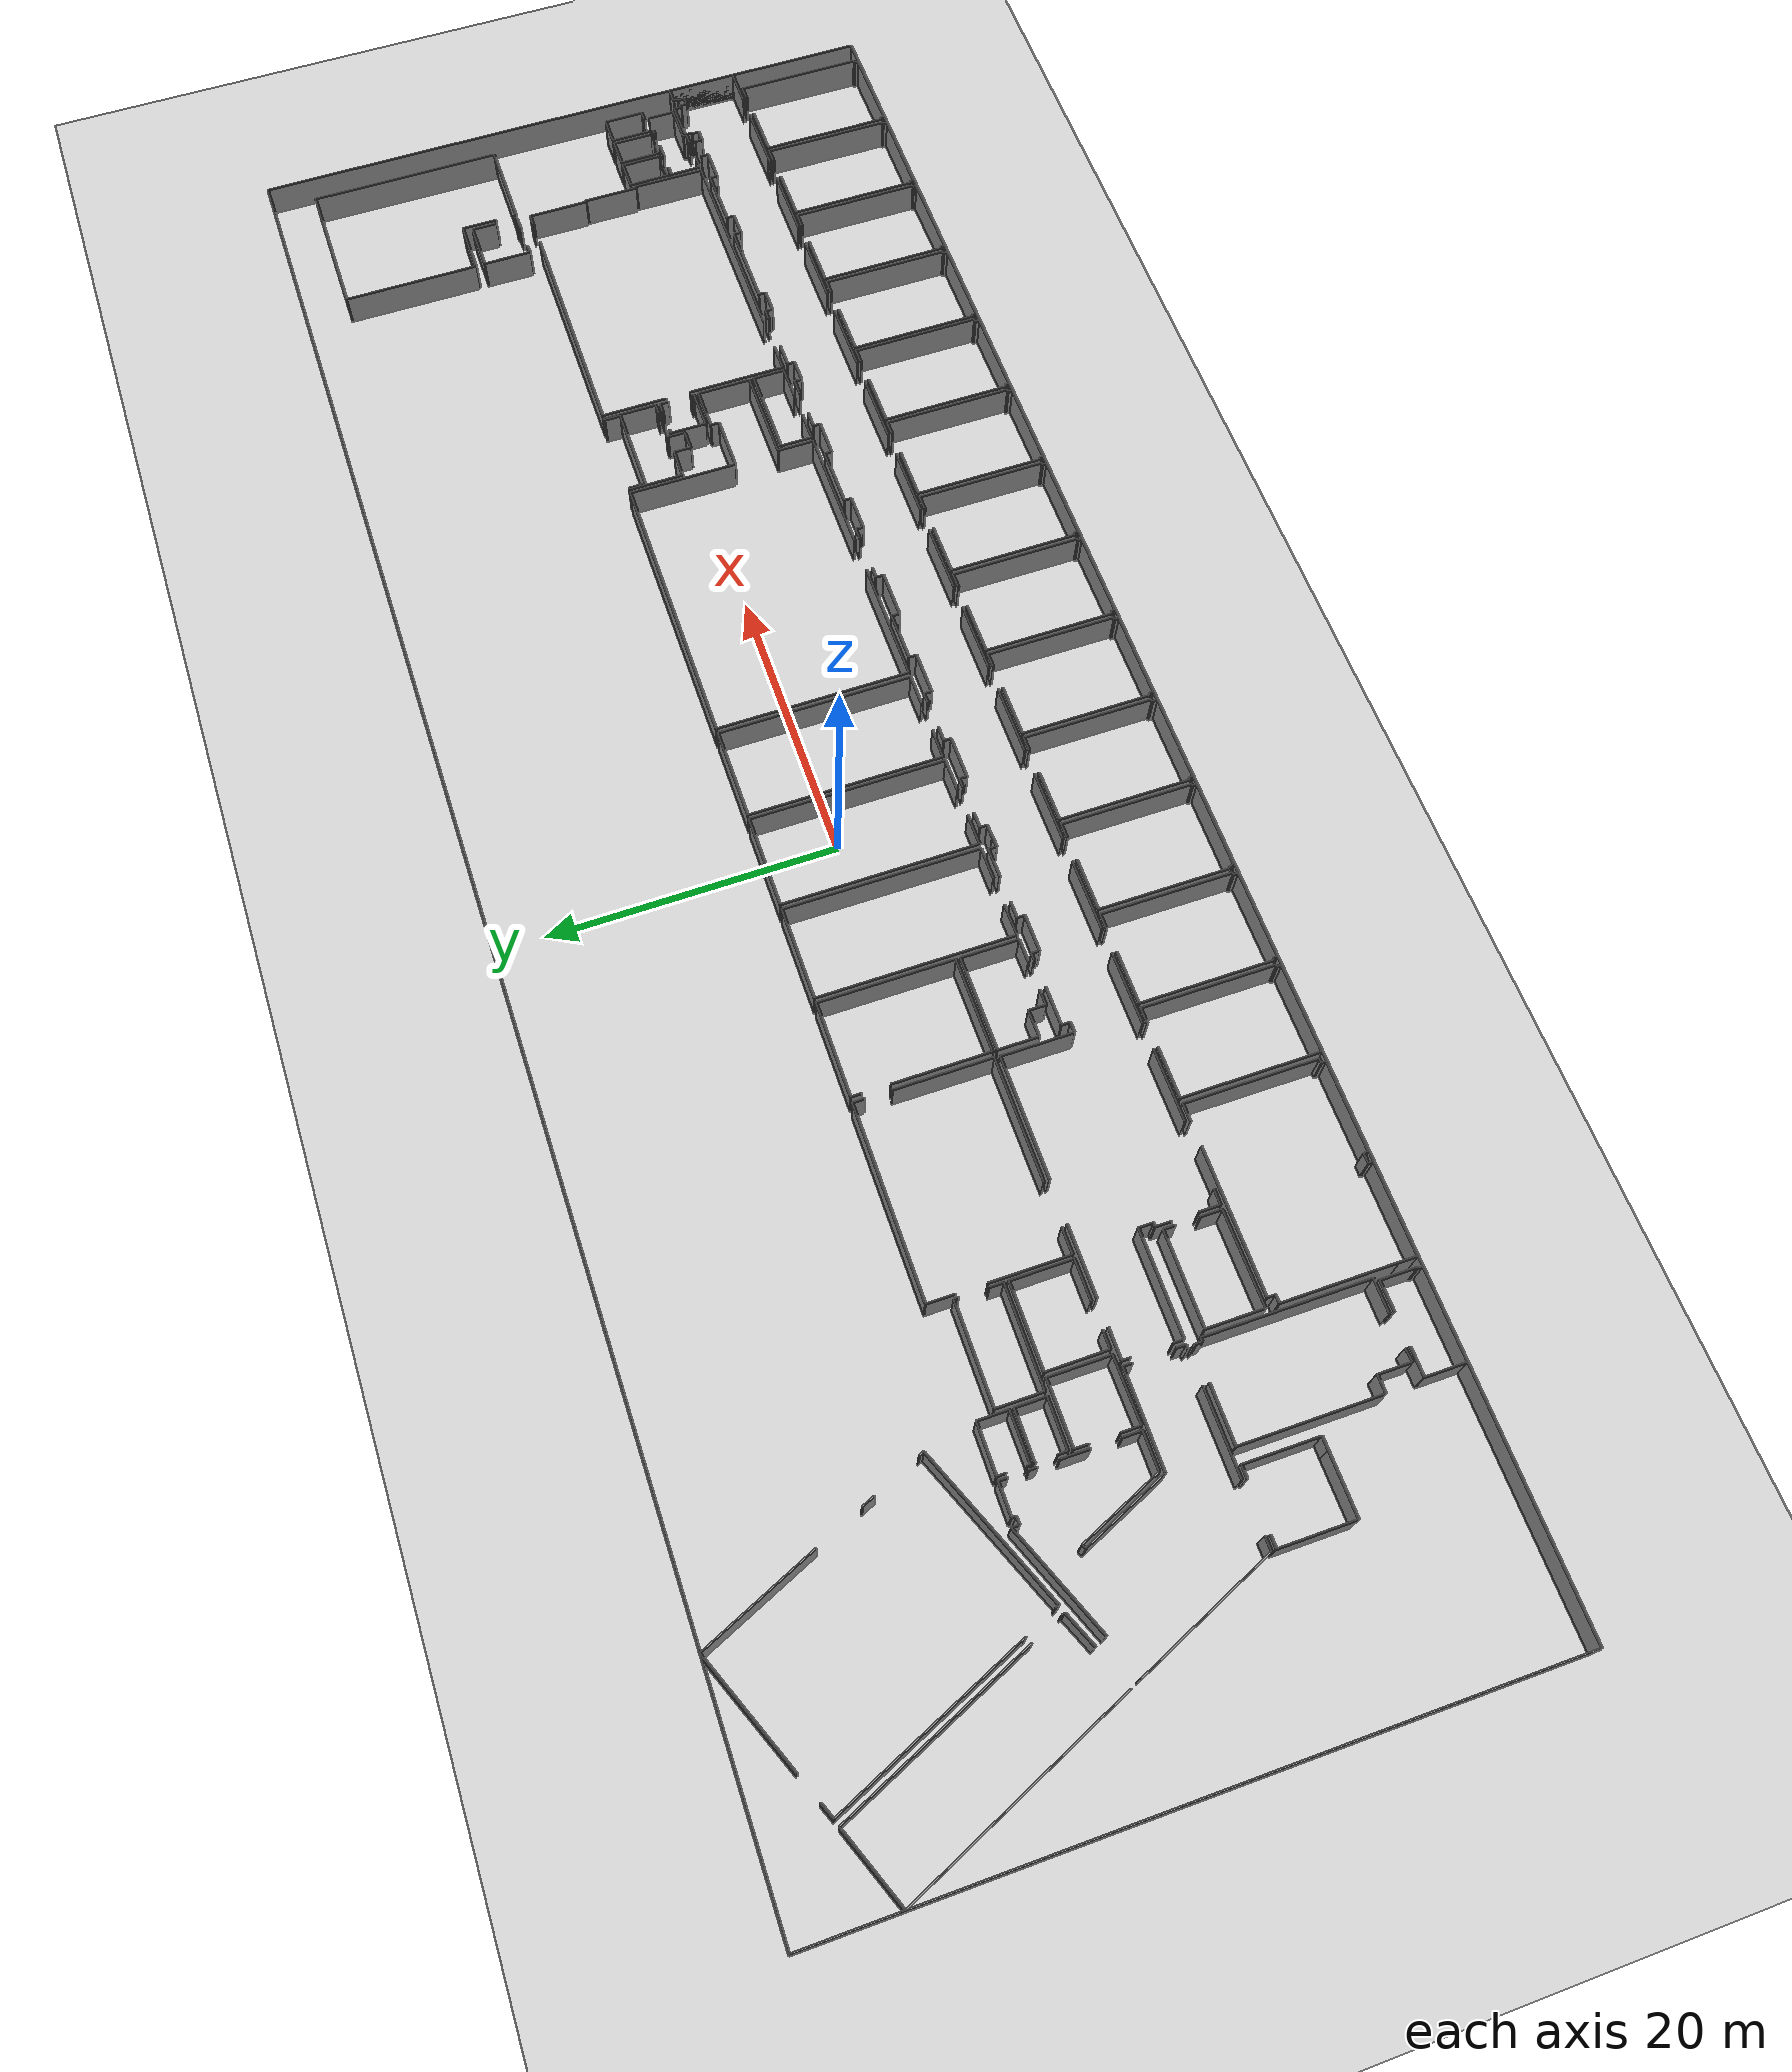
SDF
<sdf version="1.6">
  <world name="default">
    <light name="sun" type="directional">
      <cast_shadows>1</cast_shadows>
      <pose frame="">0 0 10 0 -0 0</pose>
      <diffuse>0.8 0.8 0.8 1</diffuse>
      <specular>0.1 0.1 0.1 1</specular>
      <attenuation>
        <range>1000</range>
        <constant>0.9</constant>
        <linear>0.01</linear>
        <quadratic>0.001</quadratic>
      </attenuation>
      <direction>-0.5 0.5 -1</direction>
    </light>
    <model name="ground_plane">
      <static>1</static>
      <link name="link">
        <collision name="collision">
          <geometry>
            <plane>
              <normal>0 0 1</normal>
              <size>100 100</size>
            </plane>
          </geometry>
          <surface>
            <friction>
              <ode>
                <mu>100</mu>
                <mu2>50</mu2>
              </ode>
              <torsional>
                <ode />
              </torsional>
            </friction>
            <contact>
              <ode />
            </contact>
            <bounce />
          </surface>
          <max_contacts>10</max_contacts>
        </collision>
        <visual name="visual">
          <cast_shadows>0</cast_shadows>
          <geometry>
            <plane>
              <normal>0 0 1</normal>
              <size>100 100</size>
            </plane>
          </geometry>
          <material>
            <script>
              <uri>file://media/materials/scripts/gazebo.material</uri>
              <name>Gazebo/Grey</name>
            </script>
          </material>
        </visual>
        <self_collide>0</self_collide>
        <kinematic>0</kinematic>
        <gravity>1</gravity>
      </link>
    </model>
    <gravity>0 0 -9.8</gravity>
    <magnetic_field>6e-06 2.3e-05 -4.2e-05</magnetic_field>
    <atmosphere type="adiabatic" />
    <physics default="0" name="default_physics" type="ode">
      <max_step_size>0.001</max_step_size>
      <real_time_factor>1</real_time_factor>
      <real_time_update_rate>1000</real_time_update_rate>
    </physics>
    <scene>
      <ambient>0.4 0.4 0.4 1</ambient>
      <background>0.7 0.7 0.7 1</background>
      <shadows>1</shadows>
    </scene>
    <spherical_coordinates>
      <surface_model>EARTH_WGS84</surface_model>
      <latitude_deg>0</latitude_deg>
      <longitude_deg>0</longitude_deg>
      <elevation>0</elevation>
      <heading_deg>0</heading_deg>
    </spherical_coordinates>
  <model name="0510032194_A_40_1_202">
		<static>1</static>
		<link name="Wall_0">
			<collision name="Wall_0_Collision">
				<geometry>
					<box>
						<size>14.1942335276 0.1 2.5</size>
					</box>
				</geometry>
				<pose frame="">7.0971167638 0 1.25 0 0 0</pose>
			</collision>
			<visual name="Wall_0_Visual">
				<pose frame="">7.0971167638 0 1.25 0 0 0</pose>
				<geometry>
					<box>
						<size>14.1942335276 0.1 2.5</size>
					</box>
				</geometry>
				<material>
					<script>
						<uri>file://media/materials/scripts/gazebo.material</uri>
						<name>Gazebo/Grey</name>
					</script>
					<ambient>1 1 1 1</ambient>
				</material>
			</visual>
			<pose frame="">5.42216802891 -19.5301693753 0 0 0 1.96275355551</pose>
		</link>
		<link name="Wall_1">
			<collision name="Wall_1_Collision">
				<geometry>
					<box>
						<size>5.26760678602 0.1 2.5</size>
					</box>
				</geometry>
				<pose frame="">2.63380339301 0 1.25 0 0 0</pose>
			</collision>
			<visual name="Wall_1_Visual">
				<pose frame="">2.63380339301 0 1.25 0 0 0</pose>
				<geometry>
					<box>
						<size>5.26760678602 0.1 2.5</size>
					</box>
				</geometry>
				<material>
					<script>
						<uri>file://media/materials/scripts/gazebo.material</uri>
						<name>Gazebo/Grey</name>
					</script>
					<ambient>1 1 1 1</ambient>
				</material>
			</visual>
			<pose frame="">0.0 -6.41238147859 0 0 0 0.386685495173</pose>
		</link>
		<link name="Wall_2">
			<collision name="Wall_2_Collision">
				<geometry>
					<box>
						<size>14.0388777239 0.1 2.5</size>
					</box>
				</geometry>
				<pose frame="">7.01943886194 0 1.25 0 0 0</pose>
			</collision>
			<visual name="Wall_2_Visual">
				<pose frame="">7.01943886194 0 1.25 0 0 0</pose>
				<geometry>
					<box>
						<size>14.0388777239 0.1 2.5</size>
					</box>
				</geometry>
				<material>
					<script>
						<uri>file://media/materials/scripts/gazebo.material</uri>
						<name>Gazebo/Grey</name>
					</script>
					<ambient>1 1 1 1</ambient>
				</material>
			</visual>
			<pose frame="">4.87866836868 -4.42585783146 0 0 0 -1.18029508774</pose>
		</link>
		<link name="Wall_3">
			<collision name="Wall_3_Collision">
				<geometry>
					<box>
						<size>0.203462345677 0.1 2.5</size>
					</box>
				</geometry>
				<pose frame="">0.101731172838 0 1.25 0 0 0</pose>
			</collision>
			<visual name="Wall_3_Visual">
				<pose frame="">0.101731172838 0 1.25 0 0 0</pose>
				<geometry>
					<box>
						<size>0.203462345677 0.1 2.5</size>
					</box>
				</geometry>
				<material>
					<script>
						<uri>file://media/materials/scripts/gazebo.material</uri>
						<name>Gazebo/Grey</name>
					</script>
					<ambient>1 1 1 1</ambient>
				</material>
			</visual>
			<pose frame="">11.0682645226 -19.5207702225 0 0 0 -1.23423935203</pose>
		</link>
		<link name="Wall_4">
			<collision name="Wall_4_Collision">
				<geometry>
					<box>
						<size>2.41271808424 0.1 2.5</size>
					</box>
				</geometry>
				<pose frame="">1.20635904212 0 1.25 0 0 0</pose>
			</collision>
			<visual name="Wall_4_Visual">
				<pose frame="">1.20635904212 0 1.25 0 0 0</pose>
				<geometry>
					<box>
						<size>2.41271808424 0.1 2.5</size>
					</box>
				</geometry>
				<material>
					<script>
						<uri>file://media/materials/scripts/gazebo.material</uri>
						<name>Gazebo/Grey</name>
					</script>
					<ambient>1 1 1 1</ambient>
				</material>
			</visual>
			<pose frame="">11.1354557636 -19.7128177771 0 0 0 -2.73742668199</pose>
		</link>
		<link name="Wall_5">
			<collision name="Wall_5_Collision">
				<geometry>
					<box>
						<size>2.34947865103 0.1 2.5</size>
					</box>
				</geometry>
				<pose frame="">1.17473932552 0 1.25 0 0 0</pose>
			</collision>
			<visual name="Wall_5_Visual">
				<pose frame="">1.17473932552 0 1.25 0 0 0</pose>
				<geometry>
					<box>
						<size>2.34947865103 0.1 2.5</size>
					</box>
				</geometry>
				<material>
					<script>
						<uri>file://media/materials/scripts/gazebo.material</uri>
						<name>Gazebo/Grey</name>
					</script>
					<ambient>1 1 1 1</ambient>
				</material>
			</visual>
			<pose frame="">6.31280126508 -21.7042950318 0 0 0 1.95959493722</pose>
		</link>
		<link name="Wall_6">
			<collision name="Wall_6_Collision">
				<geometry>
					<box>
						<size>13.9473994125 0.1 2.5</size>
					</box>
				</geometry>
				<pose frame="">6.97369970623 0 1.25 0 0 0</pose>
			</collision>
			<visual name="Wall_6_Visual">
				<pose frame="">6.97369970623 0 1.25 0 0 0</pose>
				<geometry>
					<box>
						<size>13.9473994125 0.1 2.5</size>
					</box>
				</geometry>
				<material>
					<script>
						<uri>file://media/materials/scripts/gazebo.material</uri>
						<name>Gazebo/Grey</name>
					</script>
					<ambient>1 1 1 1</ambient>
				</material>
			</visual>
			<pose frame="">10.6191374372 -17.1813972984 0 0 0 1.95978290704</pose>
		</link>
		<link name="Wall_7">
			<collision name="Wall_7_Collision">
				<geometry>
					<box>
						<size>1.07793721944 0.1 2.5</size>
					</box>
				</geometry>
				<pose frame="">0.538968609722 0 1.25 0 0 0</pose>
			</collision>
			<visual name="Wall_7_Visual">
				<pose frame="">0.538968609722 0 1.25 0 0 0</pose>
				<geometry>
					<box>
						<size>1.07793721944 0.1 2.5</size>
					</box>
				</geometry>
				<material>
					<script>
						<uri>file://media/materials/scripts/gazebo.material</uri>
						<name>Gazebo/Grey</name>
					</script>
					<ambient>1 1 1 1</ambient>
				</material>
			</visual>
			<pose frame="">5.32957367221 -4.27595404576 0 0 0 0.3977931229</pose>
		</link>
		<link name="Wall_8">
			<collision name="Wall_8_Collision">
				<geometry>
					<box>
						<size>8.09412175656 0.1 2.5</size>
					</box>
				</geometry>
				<pose frame="">4.04706087828 0 1.25 0 0 0</pose>
			</collision>
			<visual name="Wall_8_Visual">
				<pose frame="">4.04706087828 0 1.25 0 0 0</pose>
				<geometry>
					<box>
						<size>8.09412175656 0.1 2.5</size>
					</box>
				</geometry>
				<material>
					<script>
						<uri>file://media/materials/scripts/gazebo.material</uri>
						<name>Gazebo/Grey</name>
					</script>
					<ambient>1 1 1 1</ambient>
				</material>
			</visual>
			<pose frame="">8.08555769365 -3.11509516642 0 0 0 0.395054992161</pose>
		</link>
		<link name="Wall_9">
			<collision name="Wall_9_Collision">
				<geometry>
					<box>
						<size>8.41519522107 0.1 2.5</size>
					</box>
				</geometry>
				<pose frame="">4.20759761053 0 1.25 0 0 0</pose>
			</collision>
			<visual name="Wall_9_Visual">
				<pose frame="">4.20759761053 0 1.25 0 0 0</pose>
				<geometry>
					<box>
						<size>8.41519522107 0.1 2.5</size>
					</box>
				</geometry>
				<material>
					<script>
						<uri>file://media/materials/scripts/gazebo.material</uri>
						<name>Gazebo/Grey</name>
					</script>
					<ambient>1 1 1 1</ambient>
				</material>
			</visual>
			<pose frame="">15.556232972 -0.0 0 0 0 -1.17876733914</pose>
		</link>
		<link name="Wall_10">
			<collision name="Wall_10_Collision">
				<geometry>
					<box>
						<size>0.939879475265 0.1 2.5</size>
					</box>
				</geometry>
				<pose frame="">0.469939737633 0 1.25 0 0 0</pose>
			</collision>
			<visual name="Wall_10_Visual">
				<pose frame="">0.469939737633 0 1.25 0 0 0</pose>
				<geometry>
					<box>
						<size>0.939879475265 0.1 2.5</size>
					</box>
				</geometry>
				<material>
					<script>
						<uri>file://media/materials/scripts/gazebo.material</uri>
						<name>Gazebo/Grey</name>
					</script>
					<ambient>1 1 1 1</ambient>
				</material>
			</visual>
			<pose frame="">20.0782415963 -10.9571258915 0 0 0 -1.17864564339</pose>
		</link>
		<link name="Wall_11">
			<collision name="Wall_11_Collision">
				<geometry>
					<box>
						<size>0.338457909286 0.1 2.5</size>
					</box>
				</geometry>
				<pose frame="">0.169228954643 0 1.25 0 0 0</pose>
			</collision>
			<visual name="Wall_11_Visual">
				<pose frame="">0.169228954643 0 1.25 0 0 0</pose>
				<geometry>
					<box>
						<size>0.338457909286 0.1 2.5</size>
					</box>
				</geometry>
				<material>
					<script>
						<uri>file://media/materials/scripts/gazebo.material</uri>
						<name>Gazebo/Grey</name>
					</script>
					<ambient>1 1 1 1</ambient>
				</material>
			</visual>
			<pose frame="">21.7330005525 -14.976787903 0 0 0 -1.1743308921</pose>
		</link>
		<link name="Wall_12">
			<collision name="Wall_12_Collision">
				<geometry>
					<box>
						<size>11.0968972658 0.1 2.5</size>
					</box>
				</geometry>
				<pose frame="">5.54844863291 0 1.25 0 0 0</pose>
			</collision>
			<visual name="Wall_12_Visual">
				<pose frame="">5.54844863291 0 1.25 0 0 0</pose>
				<geometry>
					<box>
						<size>11.0968972658 0.1 2.5</size>
					</box>
				</geometry>
				<material>
					<script>
						<uri>file://media/materials/scripts/gazebo.material</uri>
						<name>Gazebo/Grey</name>
					</script>
					<ambient>1 1 1 1</ambient>
				</material>
			</visual>
			<pose frame="">21.8636995828 -15.2889921949 0 0 0 -2.74778677433</pose>
		</link>
		<link name="Wall_13">
			<collision name="Wall_13_Collision">
				<geometry>
					<box>
						<size>0.226324083436 0.1 2.5</size>
					</box>
				</geometry>
				<pose frame="">0.113162041718 0 1.25 0 0 0</pose>
			</collision>
			<visual name="Wall_13_Visual">
				<pose frame="">0.113162041718 0 1.25 0 0 0</pose>
				<geometry>
					<box>
						<size>0.226324083436 0.1 2.5</size>
					</box>
				</geometry>
				<material>
					<script>
						<uri>file://media/materials/scripts/gazebo.material</uri>
						<name>Gazebo/Grey</name>
					</script>
					<ambient>1 1 1 1</ambient>
				</material>
			</visual>
			<pose frame="">11.6162097281 -19.5469354316 0 0 0 1.96964544529</pose>
		</link>
		<link name="Wall_14">
			<collision name="Wall_14_Collision">
				<geometry>
					<box>
						<size>0.0548333769532 0.1 2.5</size>
					</box>
				</geometry>
				<pose frame="">0.0274166884766 0 1.25 0 0 0</pose>
			</collision>
			<visual name="Wall_14_Visual">
				<pose frame="">0.0274166884766 0 1.25 0 0 0</pose>
				<geometry>
					<box>
						<size>0.0548333769532 0.1 2.5</size>
					</box>
				</geometry>
				<material>
					<script>
						<uri>file://media/materials/scripts/gazebo.material</uri>
						<name>Gazebo/Grey</name>
					</script>
					<ambient>1 1 1 1</ambient>
				</material>
			</visual>
			<pose frame="">10.6423812881 -17.2310603896 0 0 0 2.00854299356</pose>
		</link>
		<link name="Wall_15">
			<collision name="Wall_15_Collision">
				<geometry>
					<box>
						<size>10.2029893452 0.1 2.5</size>
					</box>
				</geometry>
				<pose frame="">5.10149467261 0 1.25 0 0 0</pose>
			</collision>
			<visual name="Wall_15_Visual">
				<pose frame="">5.10149467261 0 1.25 0 0 0</pose>
				<geometry>
					<box>
						<size>10.2029893452 0.1 2.5</size>
					</box>
				</geometry>
				<material>
					<script>
						<uri>file://media/materials/scripts/gazebo.material</uri>
						<name>Gazebo/Grey</name>
					</script>
					<ambient>1 1 1 1</ambient>
				</material>
			</visual>
			<pose frame="">10.4824686748 -31.8431865668 0 0 0 1.96091719208</pose>
		</link>
		<link name="Wall_16">
			<collision name="Wall_16_Collision">
				<geometry>
					<box>
						<size>7.66933210681 0.1 2.5</size>
					</box>
				</geometry>
				<pose frame="">3.8346660534 0 1.25 0 0 0</pose>
			</collision>
			<visual name="Wall_16_Visual">
				<pose frame="">3.8346660534 0 1.25 0 0 0</pose>
				<geometry>
					<box>
						<size>7.66933210681 0.1 2.5</size>
					</box>
				</geometry>
				<material>
					<script>
						<uri>file://media/materials/scripts/gazebo.material</uri>
						<name>Gazebo/Grey</name>
					</script>
					<ambient>1 1 1 1</ambient>
				</material>
			</visual>
			<pose frame="">9.23962123955 -21.4392135195 0 0 0 0.389388225303</pose>
		</link>
		<link name="Wall_17">
			<collision name="Wall_17_Collision">
				<geometry>
					<box>
						<size>0.495360755997 0.1 2.5</size>
					</box>
				</geometry>
				<pose frame="">0.247680377998 0 1.25 0 0 0</pose>
			</collision>
			<visual name="Wall_17_Visual">
				<pose frame="">0.247680377998 0 1.25 0 0 0</pose>
				<geometry>
					<box>
						<size>0.495360755997 0.1 2.5</size>
					</box>
				</geometry>
				<material>
					<script>
						<uri>file://media/materials/scripts/gazebo.material</uri>
						<name>Gazebo/Grey</name>
					</script>
					<ambient>1 1 1 1</ambient>
				</material>
			</visual>
			<pose frame="">16.3348384679 -18.5277624301 0 0 0 -1.57079632679</pose>
		</link>
		<link name="Wall_18">
			<collision name="Wall_18_Collision">
				<geometry>
					<box>
						<size>0.508221058516 0.1 2.5</size>
					</box>
				</geometry>
				<pose frame="">0.254110529258 0 1.25 0 0 0</pose>
			</collision>
			<visual name="Wall_18_Visual">
				<pose frame="">0.254110529258 0 1.25 0 0 0</pose>
				<geometry>
					<box>
						<size>0.508221058516 0.1 2.5</size>
					</box>
				</geometry>
				<material>
					<script>
						<uri>file://media/materials/scripts/gazebo.material</uri>
						<name>Gazebo/Grey</name>
					</script>
					<ambient>1 1 1 1</ambient>
				</material>
			</visual>
			<pose frame="">16.3348384679 -19.0231231861 0 0 0 0.0249947936189</pose>
		</link>
		<link name="Wall_19">
			<collision name="Wall_19_Collision">
				<geometry>
					<box>
						<size>0.281339534962 0.1 2.5</size>
					</box>
				</geometry>
				<pose frame="">0.140669767481 0 1.25 0 0 0</pose>
			</collision>
			<visual name="Wall_19_Visual">
				<pose frame="">0.140669767481 0 1.25 0 0 0</pose>
				<geometry>
					<box>
						<size>0.281339534962 0.1 2.5</size>
					</box>
				</geometry>
				<material>
					<script>
						<uri>file://media/materials/scripts/gazebo.material</uri>
						<name>Gazebo/Grey</name>
					</script>
					<ambient>1 1 1 1</ambient>
				</material>
			</visual>
			<pose frame="">16.8429007818 -19.0104216282 0 0 0 1.57034485956</pose>
		</link>
		<link name="Wall_20">
			<collision name="Wall_20_Collision">
				<geometry>
					<box>
						<size>2.13436978045 0.1 2.5</size>
					</box>
				</geometry>
				<pose frame="">1.06718489023 0 1.25 0 0 0</pose>
			</collision>
			<visual name="Wall_20_Visual">
				<pose frame="">1.06718489023 0 1.25 0 0 0</pose>
				<geometry>
					<box>
						<size>2.13436978045 0.1 2.5</size>
					</box>
				</geometry>
				<material>
					<script>
						<uri>file://media/materials/scripts/gazebo.material</uri>
						<name>Gazebo/Grey</name>
					</script>
					<ambient>1 1 1 1</ambient>
				</material>
			</visual>
			<pose frame="">16.8430277974 -18.7290821219 0 0 0 0.0</pose>
		</link>
		<link name="Wall_21">
			<collision name="Wall_21_Collision">
				<geometry>
					<box>
						<size>0.580969255879 0.1 2.5</size>
					</box>
				</geometry>
				<pose frame="">0.29048462794 0 1.25 0 0 0</pose>
			</collision>
			<visual name="Wall_21_Visual">
				<pose frame="">0.29048462794 0 1.25 0 0 0</pose>
				<geometry>
					<box>
						<size>0.580969255879 0.1 2.5</size>
					</box>
				</geometry>
				<material>
					<script>
						<uri>file://media/materials/scripts/gazebo.material</uri>
						<name>Gazebo/Grey</name>
					</script>
					<ambient>1 1 1 1</ambient>
				</material>
			</visual>
			<pose frame="">18.9773975778 -18.7290821219 0 0 0 -1.57079632679</pose>
		</link>
		<link name="Wall_22">
			<collision name="Wall_22_Collision">
				<geometry>
					<box>
						<size>0.522923136523 0.1 2.5</size>
					</box>
				</geometry>
				<pose frame="">0.261461568261 0 1.25 0 0 0</pose>
			</collision>
			<visual name="Wall_22_Visual">
				<pose frame="">0.261461568261 0 1.25 0 0 0</pose>
				<geometry>
					<box>
						<size>0.522923136523 0.1 2.5</size>
					</box>
				</geometry>
				<material>
					<script>
						<uri>file://media/materials/scripts/gazebo.material</uri>
						<name>Gazebo/Grey</name>
					</script>
					<ambient>1 1 1 1</ambient>
				</material>
			</visual>
			<pose frame="">18.9773975778 -20.5976082967 0 0 0 -1.57079632679</pose>
		</link>
		<link name="Wall_23">
			<collision name="Wall_23_Collision">
				<geometry>
					<box>
						<size>1.87271768882 0.1 2.5</size>
					</box>
				</geometry>
				<pose frame="">0.936358844412 0 1.25 0 0 0</pose>
			</collision>
			<visual name="Wall_23_Visual">
				<pose frame="">0.936358844412 0 1.25 0 0 0</pose>
				<geometry>
					<box>
						<size>1.87271768882 0.1 2.5</size>
					</box>
				</geometry>
				<material>
					<script>
						<uri>file://media/materials/scripts/gazebo.material</uri>
						<name>Gazebo/Grey</name>
					</script>
					<ambient>1 1 1 1</ambient>
				</material>
			</visual>
			<pose frame="">18.9773975778 -22.4884892132 0 0 0 -1.57079632679</pose>
		</link>
		<link name="Wall_24">
			<collision name="Wall_24_Collision">
				<geometry>
					<box>
						<size>1.24653088701 0.1 2.5</size>
					</box>
				</geometry>
				<pose frame="">0.623265443507 0 1.25 0 0 0</pose>
			</collision>
			<visual name="Wall_24_Visual">
				<pose frame="">0.623265443507 0 1.25 0 0 0</pose>
				<geometry>
					<box>
						<size>1.24653088701 0.1 2.5</size>
					</box>
				</geometry>
				<material>
					<script>
						<uri>file://media/materials/scripts/gazebo.material</uri>
						<name>Gazebo/Grey</name>
					</script>
					<ambient>1 1 1 1</ambient>
				</material>
			</visual>
			<pose frame="">18.9773975778 -26.3300753837 0 0 0 -1.57079632679</pose>
		</link>
		<link name="Wall_25">
			<collision name="Wall_25_Collision">
				<geometry>
					<box>
						<size>2.44847930599 0.1 2.5</size>
					</box>
				</geometry>
				<pose frame="">1.22423965299 0 1.25 0 0 0</pose>
			</collision>
			<visual name="Wall_25_Visual">
				<pose frame="">1.22423965299 0 1.25 0 0 0</pose>
				<geometry>
					<box>
						<size>2.44847930599 0.1 2.5</size>
					</box>
				</geometry>
				<material>
					<script>
						<uri>file://media/materials/scripts/gazebo.material</uri>
						<name>Gazebo/Grey</name>
					</script>
					<ambient>1 1 1 1</ambient>
				</material>
			</visual>
			<pose frame="">18.9773975778 -27.5766062708 0 0 0 3.14159265359</pose>
		</link>
		<link name="Wall_26">
			<collision name="Wall_26_Collision">
				<geometry>
					<box>
						<size>6.07160161636 0.1 2.5</size>
					</box>
				</geometry>
				<pose frame="">3.03580080818 0 1.25 0 0 0</pose>
			</collision>
			<visual name="Wall_26_Visual">
				<pose frame="">3.03580080818 0 1.25 0 0 0</pose>
				<geometry>
					<box>
						<size>6.07160161636 0.1 2.5</size>
					</box>
				</geometry>
				<material>
					<script>
						<uri>file://media/materials/scripts/gazebo.material</uri>
						<name>Gazebo/Grey</name>
					</script>
					<ambient>1 1 1 1</ambient>
				</material>
			</visual>
			<pose frame="">16.5289182718 -27.5766062708 0 0 0 1.96460422435</pose>
		</link>
		<link name="Wall_27">
			<collision name="Wall_27_Collision">
				<geometry>
					<box>
						<size>0.27505897297 0.1 2.5</size>
					</box>
				</geometry>
				<pose frame="">0.137529486485 0 1.25 0 0 0</pose>
			</collision>
			<visual name="Wall_27_Visual">
				<pose frame="">0.137529486485 0 1.25 0 0 0</pose>
				<geometry>
					<box>
						<size>0.27505897297 0.1 2.5</size>
					</box>
				</geometry>
				<material>
					<script>
						<uri>file://media/materials/scripts/gazebo.material</uri>
						<name>Gazebo/Grey</name>
					</script>
					<ambient>1 1 1 1</ambient>
				</material>
			</visual>
			<pose frame="">14.1991985317 -21.9697575908 0 0 0 -2.70892686345</pose>
		</link>
		<link name="Wall_28">
			<collision name="Wall_28_Collision">
				<geometry>
					<box>
						<size>6.25735483055 0.1 2.5</size>
					</box>
				</geometry>
				<pose frame="">3.12867741527 0 1.25 0 0 0</pose>
			</collision>
			<visual name="Wall_28_Visual">
				<pose frame="">3.12867741527 0 1.25 0 0 0</pose>
				<geometry>
					<box>
						<size>6.25735483055 0.1 2.5</size>
					</box>
				</geometry>
				<material>
					<script>
						<uri>file://media/materials/scripts/gazebo.material</uri>
						<name>Gazebo/Grey</name>
					</script>
					<ambient>1 1 1 1</ambient>
				</material>
			</visual>
			<pose frame="">13.9494859044 -22.085087736 0 0 0 -1.17855190415</pose>
		</link>
		<link name="Wall_29">
			<collision name="Wall_29_Collision">
				<geometry>
					<box>
						<size>6.40603069967 0.1 2.5</size>
					</box>
				</geometry>
				<pose frame="">3.20301534983 0 1.25 0 0 0</pose>
			</collision>
			<visual name="Wall_29_Visual">
				<pose frame="">3.20301534983 0 1.25 0 0 0</pose>
				<geometry>
					<box>
						<size>6.40603069967 0.1 2.5</size>
					</box>
				</geometry>
				<material>
					<script>
						<uri>file://media/materials/scripts/gazebo.material</uri>
						<name>Gazebo/Grey</name>
					</script>
					<ambient>1 1 1 1</ambient>
				</material>
			</visual>
			<pose frame="">16.341443278 -27.8672179143 0 0 0 0.0</pose>
		</link>
		<link name="Wall_30">
			<collision name="Wall_30_Collision">
				<geometry>
					<box>
						<size>0.631013393793 0.1 2.5</size>
					</box>
				</geometry>
				<pose frame="">0.315506696896 0 1.25 0 0 0</pose>
			</collision>
			<visual name="Wall_30_Visual">
				<pose frame="">0.315506696896 0 1.25 0 0 0</pose>
				<geometry>
					<box>
						<size>0.631013393793 0.1 2.5</size>
					</box>
				</geometry>
				<material>
					<script>
						<uri>file://media/materials/scripts/gazebo.material</uri>
						<name>Gazebo/Grey</name>
					</script>
					<ambient>1 1 1 1</ambient>
				</material>
			</visual>
			<pose frame="">22.7474739777 -27.8672179143 0 0 0 -1.57079632679</pose>
		</link>
		<link name="Wall_31">
			<collision name="Wall_31_Collision">
				<geometry>
					<box>
						<size>0.609674776611 0.1 2.5</size>
					</box>
				</geometry>
				<pose frame="">0.304837388306 0 1.25 0 0 0</pose>
			</collision>
			<visual name="Wall_31_Visual">
				<pose frame="">0.304837388306 0 1.25 0 0 0</pose>
				<geometry>
					<box>
						<size>0.609674776611 0.1 2.5</size>
					</box>
				</geometry>
				<material>
					<script>
						<uri>file://media/materials/scripts/gazebo.material</uri>
						<name>Gazebo/Grey</name>
					</script>
					<ambient>1 1 1 1</ambient>
				</material>
			</visual>
			<pose frame="">22.7474739777 -31.2261448867 0 0 0 -1.57079632679</pose>
		</link>
		<link name="Wall_32">
			<collision name="Wall_32_Collision">
				<geometry>
					<box>
						<size>0.315887743632 0.1 2.5</size>
					</box>
				</geometry>
				<pose frame="">0.157943871816 0 1.25 0 0 0</pose>
			</collision>
			<visual name="Wall_32_Visual">
				<pose frame="">0.157943871816 0 1.25 0 0 0</pose>
				<geometry>
					<box>
						<size>0.315887743632 0.1 2.5</size>
					</box>
				</geometry>
				<material>
					<script>
						<uri>file://media/materials/scripts/gazebo.material</uri>
						<name>Gazebo/Grey</name>
					</script>
					<ambient>1 1 1 1</ambient>
				</material>
			</visual>
			<pose frame="">22.7474739777 -31.8358196633 0 0 0 3.14159265359</pose>
		</link>
		<link name="Wall_33">
			<collision name="Wall_33_Collision">
				<geometry>
					<box>
						<size>5.65270130381 0.1 2.5</size>
					</box>
				</geometry>
				<pose frame="">2.82635065191 0 1.25 0 0 0</pose>
			</collision>
			<visual name="Wall_33_Visual">
				<pose frame="">2.82635065191 0 1.25 0 0 0</pose>
				<geometry>
					<box>
						<size>5.65270130381 0.1 2.5</size>
					</box>
				</geometry>
				<material>
					<script>
						<uri>file://media/materials/scripts/gazebo.material</uri>
						<name>Gazebo/Grey</name>
					</script>
					<ambient>1 1 1 1</ambient>
				</material>
			</visual>
			<pose frame="">20.2498396428 -31.8358196633 0 0 0 3.14159265359</pose>
		</link>
		<link name="Wall_34">
			<collision name="Wall_34_Collision">
				<geometry>
					<box>
						<size>0.899935526764 0.1 2.5</size>
					</box>
				</geometry>
				<pose frame="">0.449967763382 0 1.25 0 0 0</pose>
			</collision>
			<visual name="Wall_34_Visual">
				<pose frame="">0.449967763382 0 1.25 0 0 0</pose>
				<geometry>
					<box>
						<size>0.899935526764 0.1 2.5</size>
					</box>
				</geometry>
				<material>
					<script>
						<uri>file://media/materials/scripts/gazebo.material</uri>
						<name>Gazebo/Grey</name>
					</script>
					<ambient>1 1 1 1</ambient>
				</material>
			</visual>
			<pose frame="">11.3823740482 -31.8358196633 0 0 0 -3.13340652735</pose>
		</link>
		<link name="Wall_35">
			<collision name="Wall_35_Collision">
				<geometry>
					<box>
						<size>0.174265373648 0.1 2.5</size>
					</box>
				</geometry>
				<pose frame="">0.087132686824 0 1.25 0 0 0</pose>
			</collision>
			<visual name="Wall_35_Visual">
				<pose frame="">0.087132686824 0 1.25 0 0 0</pose>
				<geometry>
					<box>
						<size>0.174265373648 0.1 2.5</size>
					</box>
				</geometry>
				<material>
					<script>
						<uri>file://media/materials/scripts/gazebo.material</uri>
						<name>Gazebo/Grey</name>
					</script>
					<ambient>1 1 1 1</ambient>
				</material>
			</visual>
			<pose frame="">19.2420980433 -20.7937203498 0 0 0 1.57079632679</pose>
		</link>
		<link name="Wall_36">
			<collision name="Wall_36_Collision">
				<geometry>
					<box>
						<size>0.593035735833 0.1 2.5</size>
					</box>
				</geometry>
				<pose frame="">0.296517867917 0 1.25 0 0 0</pose>
			</collision>
			<visual name="Wall_36_Visual">
				<pose frame="">0.296517867917 0 1.25 0 0 0</pose>
				<geometry>
					<box>
						<size>0.593035735833 0.1 2.5</size>
					</box>
				</geometry>
				<material>
					<script>
						<uri>file://media/materials/scripts/gazebo.material</uri>
						<name>Gazebo/Grey</name>
					</script>
					<ambient>1 1 1 1</ambient>
				</material>
			</visual>
			<pose frame="">19.2420980433 -19.3218638266 0 0 0 1.57079632679</pose>
		</link>
		<link name="Wall_37">
			<collision name="Wall_37_Collision">
				<geometry>
					<box>
						<size>3.28309867205 0.1 2.5</size>
					</box>
				</geometry>
				<pose frame="">1.64154933603 0 1.25 0 0 0</pose>
			</collision>
			<visual name="Wall_37_Visual">
				<pose frame="">1.64154933603 0 1.25 0 0 0</pose>
				<geometry>
					<box>
						<size>3.28309867205 0.1 2.5</size>
					</box>
				</geometry>
				<material>
					<script>
						<uri>file://media/materials/scripts/gazebo.material</uri>
						<name>Gazebo/Grey</name>
					</script>
					<ambient>1 1 1 1</ambient>
				</material>
			</visual>
			<pose frame="">19.2420980433 -18.7288280908 0 0 0 0.0</pose>
		</link>
		<link name="Wall_38">
			<collision name="Wall_38_Collision">
				<geometry>
					<box>
						<size>2.04812620268 0.1 2.5</size>
					</box>
				</geometry>
				<pose frame="">1.02406310134 0 1.25 0 0 0</pose>
			</collision>
			<visual name="Wall_38_Visual">
				<pose frame="">1.02406310134 0 1.25 0 0 0</pose>
				<geometry>
					<box>
						<size>2.04812620268 0.1 2.5</size>
					</box>
				</geometry>
				<material>
					<script>
						<uri>file://media/materials/scripts/gazebo.material</uri>
						<name>Gazebo/Grey</name>
					</script>
					<ambient>1 1 1 1</ambient>
				</material>
			</visual>
			<pose frame="">22.5251967154 -18.7288280908 0 0 0 -1.57079632679</pose>
		</link>
		<link name="Wall_39">
			<collision name="Wall_39_Collision">
				<geometry>
					<box>
						<size>3.28314148204 0.1 2.5</size>
					</box>
				</geometry>
				<pose frame="">1.64157074102 0 1.25 0 0 0</pose>
			</collision>
			<visual name="Wall_39_Visual">
				<pose frame="">1.64157074102 0 1.25 0 0 0</pose>
				<geometry>
					<box>
						<size>3.28314148204 0.1 2.5</size>
					</box>
				</geometry>
				<material>
					<script>
						<uri>file://media/materials/scripts/gazebo.material</uri>
						<name>Gazebo/Grey</name>
					</script>
					<ambient>1 1 1 1</ambient>
				</material>
			</visual>
			<pose frame="">22.5251967154 -20.7769542934 0 0 0 -3.1364859199</pose>
		</link>
		<link name="Wall_40">
			<collision name="Wall_40_Collision">
				<geometry>
					<box>
						<size>0.624535599291 0.1 2.5</size>
					</box>
				</geometry>
				<pose frame="">0.312267799646 0 1.25 0 0 0</pose>
			</collision>
			<visual name="Wall_40_Visual">
				<pose frame="">0.312267799646 0 1.25 0 0 0</pose>
				<geometry>
					<box>
						<size>0.624535599291 0.1 2.5</size>
					</box>
				</geometry>
				<material>
					<script>
						<uri>file://media/materials/scripts/gazebo.material</uri>
						<name>Gazebo/Grey</name>
					</script>
					<ambient>1 1 1 1</ambient>
				</material>
			</visual>
			<pose frame="">19.2638177072 -23.0958777094 0 0 0 1.57079632679</pose>
		</link>
		<link name="Wall_41">
			<collision name="Wall_41_Collision">
				<geometry>
					<box>
						<size>0.0798927988518 0.1 2.5</size>
					</box>
				</geometry>
				<pose frame="">0.0399463994259 0 1.25 0 0 0</pose>
			</collision>
			<visual name="Wall_41_Visual">
				<pose frame="">0.0399463994259 0 1.25 0 0 0</pose>
				<geometry>
					<box>
						<size>0.0798927988518 0.1 2.5</size>
					</box>
				</geometry>
				<material>
					<script>
						<uri>file://media/materials/scripts/gazebo.material</uri>
						<name>Gazebo/Grey</name>
					</script>
					<ambient>1 1 1 1</ambient>
				</material>
			</visual>
			<pose frame="">19.2638177072 -21.1277713212 0 0 0 1.57079632679</pose>
		</link>
		<link name="Wall_42">
			<collision name="Wall_42_Collision">
				<geometry>
					<box>
						<size>3.26976203631 0.1 2.5</size>
					</box>
				</geometry>
				<pose frame="">1.63488101816 0 1.25 0 0 0</pose>
			</collision>
			<visual name="Wall_42_Visual">
				<pose frame="">1.63488101816 0 1.25 0 0 0</pose>
				<geometry>
					<box>
						<size>3.26976203631 0.1 2.5</size>
					</box>
				</geometry>
				<material>
					<script>
						<uri>file://media/materials/scripts/gazebo.material</uri>
						<name>Gazebo/Grey</name>
					</script>
					<ambient>1 1 1 1</ambient>
				</material>
			</visual>
			<pose frame="">19.2638177072 -21.0478785223 0 0 0 0.0</pose>
		</link>
		<link name="Wall_43">
			<collision name="Wall_43_Collision">
				<geometry>
					<box>
						<size>2.05231771677 0.1 2.5</size>
					</box>
				</geometry>
				<pose frame="">1.02615885838 0 1.25 0 0 0</pose>
			</collision>
			<visual name="Wall_43_Visual">
				<pose frame="">1.02615885838 0 1.25 0 0 0</pose>
				<geometry>
					<box>
						<size>2.05231771677 0.1 2.5</size>
					</box>
				</geometry>
				<material>
					<script>
						<uri>file://media/materials/scripts/gazebo.material</uri>
						<name>Gazebo/Grey</name>
					</script>
					<ambient>1 1 1 1</ambient>
				</material>
			</visual>
			<pose frame="">22.5335797436 -21.0478785223 0 0 0 -1.57079632679</pose>
		</link>
		<link name="Wall_44">
			<collision name="Wall_44_Collision">
				<geometry>
					<box>
						<size>3.26976488816 0.1 2.5</size>
					</box>
				</geometry>
				<pose frame="">1.63488244408 0 1.25 0 0 0</pose>
			</collision>
			<visual name="Wall_44_Visual">
				<pose frame="">1.63488244408 0 1.25 0 0 0</pose>
				<geometry>
					<box>
						<size>3.26976488816 0.1 2.5</size>
					</box>
				</geometry>
				<material>
					<script>
						<uri>file://media/materials/scripts/gazebo.material</uri>
						<name>Gazebo/Grey</name>
					</script>
					<ambient>1 1 1 1</ambient>
				</material>
			</visual>
			<pose frame="">22.5335797436 -23.1001962391 0 0 0 3.14027190697</pose>
		</link>
		<link name="Wall_45">
			<collision name="Wall_45_Collision">
				<geometry>
					<box>
						<size>1.28285734245 0.1 2.5</size>
					</box>
				</geometry>
				<pose frame="">0.641428671227 0 1.25 0 0 0</pose>
			</collision>
			<visual name="Wall_45_Visual">
				<pose frame="">0.641428671227 0 1.25 0 0 0</pose>
				<geometry>
					<box>
						<size>1.28285734245 0.1 2.5</size>
					</box>
				</geometry>
				<material>
					<script>
						<uri>file://media/materials/scripts/gazebo.material</uri>
						<name>Gazebo/Grey</name>
					</script>
					<ambient>1 1 1 1</ambient>
				</material>
			</visual>
			<pose frame="">19.2561967725 -27.6220778478 0 0 0 1.57079632679</pose>
		</link>
		<link name="Wall_46">
			<collision name="Wall_46_Collision">
				<geometry>
					<box>
						<size>0.965953474194 0.1 2.5</size>
					</box>
				</geometry>
				<pose frame="">0.482976737097 0 1.25 0 0 0</pose>
			</collision>
			<visual name="Wall_46_Visual">
				<pose frame="">0.482976737097 0 1.25 0 0 0</pose>
				<geometry>
					<box>
						<size>0.965953474194 0.1 2.5</size>
					</box>
				</geometry>
				<material>
					<script>
						<uri>file://media/materials/scripts/gazebo.material</uri>
						<name>Gazebo/Grey</name>
					</script>
					<ambient>1 1 1 1</ambient>
				</material>
			</visual>
			<pose frame="">19.2561967725 -24.3885152514 0 0 0 1.57079632679</pose>
		</link>
		<link name="Wall_47">
			<collision name="Wall_47_Collision">
				<geometry>
					<box>
						<size>4.31294098221 0.1 2.5</size>
					</box>
				</geometry>
				<pose frame="">2.15647049111 0 1.25 0 0 0</pose>
			</collision>
			<visual name="Wall_47_Visual">
				<pose frame="">2.15647049111 0 1.25 0 0 0</pose>
				<geometry>
					<box>
						<size>4.31294098221 0.1 2.5</size>
					</box>
				</geometry>
				<material>
					<script>
						<uri>file://media/materials/scripts/gazebo.material</uri>
						<name>Gazebo/Grey</name>
					</script>
					<ambient>1 1 1 1</ambient>
				</material>
			</visual>
			<pose frame="">19.2561967725 -23.4225617772 0 0 0 0.0</pose>
		</link>
		<link name="Wall_48">
			<collision name="Wall_48_Collision">
				<geometry>
					<box>
						<size>4.14655057443 0.1 2.5</size>
					</box>
				</geometry>
				<pose frame="">2.07327528721 0 1.25 0 0 0</pose>
			</collision>
			<visual name="Wall_48_Visual">
				<pose frame="">2.07327528721 0 1.25 0 0 0</pose>
				<geometry>
					<box>
						<size>4.14655057443 0.1 2.5</size>
					</box>
				</geometry>
				<material>
					<script>
						<uri>file://media/materials/scripts/gazebo.material</uri>
						<name>Gazebo/Grey</name>
					</script>
					<ambient>1 1 1 1</ambient>
				</material>
			</visual>
			<pose frame="">23.5691377547 -23.4225617772 0 0 0 -1.57079632679</pose>
		</link>
		<link name="Wall_49">
			<collision name="Wall_49_Collision">
				<geometry>
					<box>
						<size>4.31326619395 0.1 2.5</size>
					</box>
				</geometry>
				<pose frame="">2.15663309697 0 1.25 0 0 0</pose>
			</collision>
			<visual name="Wall_49_Visual">
				<pose frame="">2.15663309697 0 1.25 0 0 0</pose>
				<geometry>
					<box>
						<size>4.31326619395 0.1 2.5</size>
					</box>
				</geometry>
				<material>
					<script>
						<uri>file://media/materials/scripts/gazebo.material</uri>
						<name>Gazebo/Grey</name>
					</script>
					<ambient>1 1 1 1</ambient>
				</material>
			</visual>
			<pose frame="">23.5691377547 -27.5691123516 0 0 0 -3.12931267247</pose>
		</link>
		<link name="Wall_50">
			<collision name="Wall_50_Collision">
				<geometry>
					<box>
						<size>5.04404265183 0.1 2.5</size>
					</box>
				</geometry>
				<pose frame="">2.52202132592 0 1.25 0 0 0</pose>
			</collision>
			<visual name="Wall_50_Visual">
				<pose frame="">2.52202132592 0 1.25 0 0 0</pose>
				<geometry>
					<box>
						<size>5.04404265183 0.1 2.5</size>
					</box>
				</geometry>
				<material>
					<script>
						<uri>file://media/materials/scripts/gazebo.material</uri>
						<name>Gazebo/Grey</name>
					</script>
					<ambient>1 1 1 1</ambient>
				</material>
			</visual>
			<pose frame="">10.5168898965 -37.1888912175 0 0 0 1.57079632679</pose>
		</link>
		<link name="Wall_51">
			<collision name="Wall_51_Collision">
				<geometry>
					<box>
						<size>0.834111303751 0.1 2.5</size>
					</box>
				</geometry>
				<pose frame="">0.417055651876 0 1.25 0 0 0</pose>
			</collision>
			<visual name="Wall_51_Visual">
				<pose frame="">0.417055651876 0 1.25 0 0 0</pose>
				<geometry>
					<box>
						<size>0.834111303751 0.1 2.5</size>
					</box>
				</geometry>
				<material>
					<script>
						<uri>file://media/materials/scripts/gazebo.material</uri>
						<name>Gazebo/Grey</name>
					</script>
					<ambient>1 1 1 1</ambient>
				</material>
			</visual>
			<pose frame="">10.5168898965 -32.1448485657 0 0 0 0.0</pose>
		</link>
		<link name="Wall_52">
			<collision name="Wall_52_Collision">
				<geometry>
					<box>
						<size>0.861546668699 0.1 2.5</size>
					</box>
				</geometry>
				<pose frame="">0.430773334349 0 1.25 0 0 0</pose>
			</collision>
			<visual name="Wall_52_Visual">
				<pose frame="">0.430773334349 0 1.25 0 0 0</pose>
				<geometry>
					<box>
						<size>0.861546668699 0.1 2.5</size>
					</box>
				</geometry>
				<material>
					<script>
						<uri>file://media/materials/scripts/gazebo.material</uri>
						<name>Gazebo/Grey</name>
					</script>
					<ambient>1 1 1 1</ambient>
				</material>
			</visual>
			<pose frame="">14.5521748242 -32.1448485657 0 0 0 0.0</pose>
		</link>
		<link name="Wall_53">
			<collision name="Wall_53_Collision">
				<geometry>
					<box>
						<size>5.01254278837 0.1 2.5</size>
					</box>
				</geometry>
				<pose frame="">2.50627139419 0 1.25 0 0 0</pose>
			</collision>
			<visual name="Wall_53_Visual">
				<pose frame="">2.50627139419 0 1.25 0 0 0</pose>
				<geometry>
					<box>
						<size>5.01254278837 0.1 2.5</size>
					</box>
				</geometry>
				<material>
					<script>
						<uri>file://media/materials/scripts/gazebo.material</uri>
						<name>Gazebo/Grey</name>
					</script>
					<ambient>1 1 1 1</ambient>
				</material>
			</visual>
			<pose frame="">15.4137214929 -32.1448485657 0 0 0 -1.57079632679</pose>
		</link>
		<link name="Wall_54">
			<collision name="Wall_54_Collision">
				<geometry>
					<box>
						<size>0.854306780727 0.1 2.5</size>
					</box>
				</geometry>
				<pose frame="">0.427153390363 0 1.25 0 0 0</pose>
			</collision>
			<visual name="Wall_54_Visual">
				<pose frame="">0.427153390363 0 1.25 0 0 0</pose>
				<geometry>
					<box>
						<size>0.854306780727 0.1 2.5</size>
					</box>
				</geometry>
				<material>
					<script>
						<uri>file://media/materials/scripts/gazebo.material</uri>
						<name>Gazebo/Grey</name>
					</script>
					<ambient>1 1 1 1</ambient>
				</material>
			</visual>
			<pose frame="">15.4137214929 -37.157391354 0 0 0 3.14159265359</pose>
		</link>
		<link name="Wall_55">
			<collision name="Wall_55_Collision">
				<geometry>
					<box>
						<size>4.04264753926 0.1 2.5</size>
					</box>
				</geometry>
				<pose frame="">2.02132376963 0 1.25 0 0 0</pose>
			</collision>
			<visual name="Wall_55_Visual">
				<pose frame="">2.02132376963 0 1.25 0 0 0</pose>
				<geometry>
					<box>
						<size>4.04264753926 0.1 2.5</size>
					</box>
				</geometry>
				<material>
					<script>
						<uri>file://media/materials/scripts/gazebo.material</uri>
						<name>Gazebo/Grey</name>
					</script>
					<ambient>1 1 1 1</ambient>
				</material>
			</visual>
			<pose frame="">14.5594147122 -37.157391354 0 0 0 -3.13380068511</pose>
		</link>
		<link name="Wall_56">
			<collision name="Wall_56_Collision">
				<geometry>
					<box>
						<size>2.24944589454 0.1 2.5</size>
					</box>
				</geometry>
				<pose frame="">1.12472294727 0 1.25 0 0 0</pose>
			</collision>
			<visual name="Wall_56_Visual">
				<pose frame="">1.12472294727 0 1.25 0 0 0</pose>
				<geometry>
					<box>
						<size>2.24944589454 0.1 2.5</size>
					</box>
				</geometry>
				<material>
					<script>
						<uri>file://media/materials/scripts/gazebo.material</uri>
						<name>Gazebo/Grey</name>
					</script>
					<ambient>1 1 1 1</ambient>
				</material>
			</visual>
			<pose frame="">17.6011837852 -43.8934085266 0 0 0 1.57079632679</pose>
		</link>
		<link name="Wall_57">
			<collision name="Wall_57_Collision">
				<geometry>
					<box>
						<size>1.16854332184 0.1 2.5</size>
					</box>
				</geometry>
				<pose frame="">0.584271660919 0 1.25 0 0 0</pose>
			</collision>
			<visual name="Wall_57_Visual">
				<pose frame="">0.584271660919 0 1.25 0 0 0</pose>
				<geometry>
					<box>
						<size>1.16854332184 0.1 2.5</size>
					</box>
				</geometry>
				<material>
					<script>
						<uri>file://media/materials/scripts/gazebo.material</uri>
						<name>Gazebo/Grey</name>
					</script>
					<ambient>1 1 1 1</ambient>
				</material>
			</visual>
			<pose frame="">17.6011837852 -41.643962632 0 0 0 3.14159265359</pose>
		</link>
		<link name="Wall_58">
			<collision name="Wall_58_Collision">
				<geometry>
					<box>
						<size>9.39762861915 0.1 2.5</size>
					</box>
				</geometry>
				<pose frame="">4.69881430958 0 1.25 0 0 0</pose>
			</collision>
			<visual name="Wall_58_Visual">
				<pose frame="">4.69881430958 0 1.25 0 0 0</pose>
				<geometry>
					<box>
						<size>9.39762861915 0.1 2.5</size>
					</box>
				</geometry>
				<material>
					<script>
						<uri>file://media/materials/scripts/gazebo.material</uri>
						<name>Gazebo/Grey</name>
					</script>
					<ambient>1 1 1 1</ambient>
				</material>
			</visual>
			<pose frame="">16.4326404634 -41.643962632 0 0 0 1.57079632679</pose>
		</link>
		<link name="Wall_59">
			<collision name="Wall_59_Collision">
				<geometry>
					<box>
						<size>3.83650554741 0.1 2.5</size>
					</box>
				</geometry>
				<pose frame="">1.9182527737 0 1.25 0 0 0</pose>
			</collision>
			<visual name="Wall_59_Visual">
				<pose frame="">1.9182527737 0 1.25 0 0 0</pose>
				<geometry>
					<box>
						<size>3.83650554741 0.1 2.5</size>
					</box>
				</geometry>
				<material>
					<script>
						<uri>file://media/materials/scripts/gazebo.material</uri>
						<name>Gazebo/Grey</name>
					</script>
					<ambient>1 1 1 1</ambient>
				</material>
			</visual>
			<pose frame="">16.4326404634 -32.2463340129 0 0 0 0.0</pose>
		</link>
		<link name="Wall_60">
			<collision name="Wall_60_Collision">
				<geometry>
					<box>
						<size>0.153561834359 0.1 2.5</size>
					</box>
				</geometry>
				<pose frame="">0.0767809171795 0 1.25 0 0 0</pose>
			</collision>
			<visual name="Wall_60_Visual">
				<pose frame="">0.0767809171795 0 1.25 0 0 0</pose>
				<geometry>
					<box>
						<size>0.153561834359 0.1 2.5</size>
					</box>
				</geometry>
				<material>
					<script>
						<uri>file://media/materials/scripts/gazebo.material</uri>
						<name>Gazebo/Grey</name>
					</script>
					<ambient>1 1 1 1</ambient>
				</material>
			</visual>
			<pose frame="">22.4397152311 -32.2463340129 0 0 0 0.0</pose>
		</link>
		<link name="Wall_61">
			<collision name="Wall_61_Collision">
				<geometry>
					<box>
						<size>0.566616495513 0.1 2.5</size>
					</box>
				</geometry>
				<pose frame="">0.283308247757 0 1.25 0 0 0</pose>
			</collision>
			<visual name="Wall_61_Visual">
				<pose frame="">0.283308247757 0 1.25 0 0 0</pose>
				<geometry>
					<box>
						<size>0.566616495513 0.1 2.5</size>
					</box>
				</geometry>
				<material>
					<script>
						<uri>file://media/materials/scripts/gazebo.material</uri>
						<name>Gazebo/Grey</name>
					</script>
					<ambient>1 1 1 1</ambient>
				</material>
			</visual>
			<pose frame="">22.5932770654 -32.2463340129 0 0 0 -1.57079632679</pose>
		</link>
		<link name="Wall_62">
			<collision name="Wall_62_Collision">
				<geometry>
					<box>
						<size>0.259365811217 0.1 2.5</size>
					</box>
				</geometry>
				<pose frame="">0.129682905608 0 1.25 0 0 0</pose>
			</collision>
			<visual name="Wall_62_Visual">
				<pose frame="">0.129682905608 0 1.25 0 0 0</pose>
				<geometry>
					<box>
						<size>0.259365811217 0.1 2.5</size>
					</box>
				</geometry>
				<material>
					<script>
						<uri>file://media/materials/scripts/gazebo.material</uri>
						<name>Gazebo/Grey</name>
					</script>
					<ambient>1 1 1 1</ambient>
				</material>
			</visual>
			<pose frame="">22.5932770654 -32.8129505084 0 0 0 0.0</pose>
		</link>
		<link name="Wall_63">
			<collision name="Wall_63_Collision">
				<geometry>
					<box>
						<size>11.0179663536 0.1 2.5</size>
					</box>
				</geometry>
				<pose frame="">5.50898317679 0 1.25 0 0 0</pose>
			</collision>
			<visual name="Wall_63_Visual">
				<pose frame="">5.50898317679 0 1.25 0 0 0</pose>
				<geometry>
					<box>
						<size>11.0179663536 0.1 2.5</size>
					</box>
				</geometry>
				<material>
					<script>
						<uri>file://media/materials/scripts/gazebo.material</uri>
						<name>Gazebo/Grey</name>
					</script>
					<ambient>1 1 1 1</ambient>
				</material>
			</visual>
			<pose frame="">22.8526428766 -32.8129505084 0 0 0 -1.57079632679</pose>
		</link>
		<link name="Wall_64">
			<collision name="Wall_64_Collision">
				<geometry>
					<box>
						<size>2.25224023727 0.1 2.5</size>
					</box>
				</geometry>
				<pose frame="">1.12612011863 0 1.25 0 0 0</pose>
			</collision>
			<visual name="Wall_64_Visual">
				<pose frame="">1.12612011863 0 1.25 0 0 0</pose>
				<geometry>
					<box>
						<size>2.25224023727 0.1 2.5</size>
					</box>
				</geometry>
				<material>
					<script>
						<uri>file://media/materials/scripts/gazebo.material</uri>
						<name>Gazebo/Grey</name>
					</script>
					<ambient>1 1 1 1</ambient>
				</material>
			</visual>
			<pose frame="">22.8526428766 -43.830916862 0 0 0 3.14159265359</pose>
		</link>
		<link name="Wall_65">
			<collision name="Wall_65_Collision">
				<geometry>
					<box>
						<size>0.859122894422 0.1 2.5</size>
					</box>
				</geometry>
				<pose frame="">0.429561447211 0 1.25 0 0 0</pose>
			</collision>
			<visual name="Wall_65_Visual">
				<pose frame="">0.429561447211 0 1.25 0 0 0</pose>
				<geometry>
					<box>
						<size>0.859122894422 0.1 2.5</size>
					</box>
				</geometry>
				<material>
					<script>
						<uri>file://media/materials/scripts/gazebo.material</uri>
						<name>Gazebo/Grey</name>
					</script>
					<ambient>1 1 1 1</ambient>
				</material>
			</visual>
			<pose frame="">18.4580308775 -43.830916862 0 0 0 -3.06878944542</pose>
		</link>
		<link name="Wall_66">
			<collision name="Wall_66_Collision">
				<geometry>
					<box>
						<size>2.76868557929 0.1 2.5</size>
					</box>
				</geometry>
				<pose frame="">1.38434278964 0 1.25 0 0 0</pose>
			</collision>
			<visual name="Wall_66_Visual">
				<pose frame="">1.38434278964 0 1.25 0 0 0</pose>
				<geometry>
					<box>
						<size>2.76868557929 0.1 2.5</size>
					</box>
				</geometry>
				<material>
					<script>
						<uri>file://media/materials/scripts/gazebo.material</uri>
						<name>Gazebo/Grey</name>
					</script>
					<ambient>1 1 1 1</ambient>
				</material>
			</visual>
			<pose frame="">16.5789624097 -46.9102825462 0 0 0 1.57079632679</pose>
		</link>
		<link name="Wall_67">
			<collision name="Wall_67_Collision">
				<geometry>
					<box>
						<size>1.90777398848 0.1 2.5</size>
					</box>
				</geometry>
				<pose frame="">0.95388699424 0 1.25 0 0 0</pose>
			</collision>
			<visual name="Wall_67_Visual">
				<pose frame="">0.95388699424 0 1.25 0 0 0</pose>
				<geometry>
					<box>
						<size>1.90777398848 0.1 2.5</size>
					</box>
				</geometry>
				<material>
					<script>
						<uri>file://media/materials/scripts/gazebo.material</uri>
						<name>Gazebo/Grey</name>
					</script>
					<ambient>1 1 1 1</ambient>
				</material>
			</visual>
			<pose frame="">16.5789624097 -44.1415969669 0 0 0 0.0</pose>
		</link>
		<link name="Wall_68">
			<collision name="Wall_68_Collision">
				<geometry>
					<box>
						<size>2.02208800909 0.1 2.5</size>
					</box>
				</geometry>
				<pose frame="">1.01104400455 0 1.25 0 0 0</pose>
			</collision>
			<visual name="Wall_68_Visual">
				<pose frame="">1.01104400455 0 1.25 0 0 0</pose>
				<geometry>
					<box>
						<size>2.02208800909 0.1 2.5</size>
					</box>
				</geometry>
				<material>
					<script>
						<uri>file://media/materials/scripts/gazebo.material</uri>
						<name>Gazebo/Grey</name>
					</script>
					<ambient>1 1 1 1</ambient>
				</material>
			</visual>
			<pose frame="">20.6000215926 -44.1415969669 0 0 0 0.0</pose>
		</link>
		<link name="Wall_69">
			<collision name="Wall_69_Collision">
				<geometry>
					<box>
						<size>2.45660830301 0.1 2.5</size>
					</box>
				</geometry>
				<pose frame="">1.2283041515 0 1.25 0 0 0</pose>
			</collision>
			<visual name="Wall_69_Visual">
				<pose frame="">1.2283041515 0 1.25 0 0 0</pose>
				<geometry>
					<box>
						<size>2.45660830301 0.1 2.5</size>
					</box>
				</geometry>
				<material>
					<script>
						<uri>file://media/materials/scripts/gazebo.material</uri>
						<name>Gazebo/Grey</name>
					</script>
					<ambient>1 1 1 1</ambient>
				</material>
			</visual>
			<pose frame="">22.6221096017 -44.1415969669 0 0 0 -1.57079632679</pose>
		</link>
		<link name="Wall_70">
			<collision name="Wall_70_Collision">
				<geometry>
					<box>
						<size>0.0762093470764 0.1 2.5</size>
					</box>
				</geometry>
				<pose frame="">0.0381046735382 0 1.25 0 0 0</pose>
			</collision>
			<visual name="Wall_70_Visual">
				<pose frame="">0.0381046735382 0 1.25 0 0 0</pose>
				<geometry>
					<box>
						<size>0.0762093470764 0.1 2.5</size>
					</box>
				</geometry>
				<material>
					<script>
						<uri>file://media/materials/scripts/gazebo.material</uri>
						<name>Gazebo/Grey</name>
					</script>
					<ambient>1 1 1 1</ambient>
				</material>
			</visual>
			<pose frame="">22.6221096017 -46.5982052699 0 0 0 3.14159265359</pose>
		</link>
		<link name="Wall_71">
			<collision name="Wall_71_Collision">
				<geometry>
					<box>
						<size>0.317538946152 0.1 2.5</size>
					</box>
				</geometry>
				<pose frame="">0.158769473076 0 1.25 0 0 0</pose>
			</collision>
			<visual name="Wall_71_Visual">
				<pose frame="">0.158769473076 0 1.25 0 0 0</pose>
				<geometry>
					<box>
						<size>0.317538946152 0.1 2.5</size>
					</box>
				</geometry>
				<material>
					<script>
						<uri>file://media/materials/scripts/gazebo.material</uri>
						<name>Gazebo/Grey</name>
					</script>
					<ambient>1 1 1 1</ambient>
				</material>
			</visual>
			<pose frame="">22.5459002547 -46.5982052699 0 0 0 -1.57079632679</pose>
		</link>
		<link name="Wall_72">
			<collision name="Wall_72_Collision">
				<geometry>
					<box>
						<size>5.96694034452 0.1 2.5</size>
					</box>
				</geometry>
				<pose frame="">2.98347017226 0 1.25 0 0 0</pose>
			</collision>
			<visual name="Wall_72_Visual">
				<pose frame="">2.98347017226 0 1.25 0 0 0</pose>
				<geometry>
					<box>
						<size>5.96694034452 0.1 2.5</size>
					</box>
				</geometry>
				<material>
					<script>
						<uri>file://media/materials/scripts/gazebo.material</uri>
						<name>Gazebo/Grey</name>
					</script>
					<ambient>1 1 1 1</ambient>
				</material>
			</visual>
			<pose frame="">22.5459002547 -46.915744216 0 0 0 3.14067733178</pose>
		</link>
		<link name="Wall_73">
			<collision name="Wall_73_Collision">
				<geometry>
					<box>
						<size>3.13664971009 0.1 2.5</size>
					</box>
				</geometry>
				<pose frame="">1.56832485504 0 1.25 0 0 0</pose>
			</collision>
			<visual name="Wall_73_Visual">
				<pose frame="">1.56832485504 0 1.25 0 0 0</pose>
				<geometry>
					<box>
						<size>3.13664971009 0.1 2.5</size>
					</box>
				</geometry>
				<material>
					<script>
						<uri>file://media/materials/scripts/gazebo.material</uri>
						<name>Gazebo/Grey</name>
					</script>
					<ambient>1 1 1 1</ambient>
				</material>
			</visual>
			<pose frame="">22.8358768203 -23.0848273541 0 0 0 1.57079632679</pose>
		</link>
		<link name="Wall_74">
			<collision name="Wall_74_Collision">
				<geometry>
					<box>
						<size>6.74833768362 0.1 2.5</size>
					</box>
				</geometry>
				<pose frame="">3.37416884181 0 1.25 0 0 0</pose>
			</collision>
			<visual name="Wall_74_Visual">
				<pose frame="">3.37416884181 0 1.25 0 0 0</pose>
				<geometry>
					<box>
						<size>6.74833768362 0.1 2.5</size>
					</box>
				</geometry>
				<material>
					<script>
						<uri>file://media/materials/scripts/gazebo.material</uri>
						<name>Gazebo/Grey</name>
					</script>
					<ambient>1 1 1 1</ambient>
				</material>
			</visual>
			<pose frame="">22.8358768203 -19.948177644 0 0 0 0.0</pose>
		</link>
		<link name="Wall_75">
			<collision name="Wall_75_Collision">
				<geometry>
					<box>
						<size>0.254031156921 0.1 2.5</size>
					</box>
				</geometry>
				<pose frame="">0.127015578461 0 1.25 0 0 0</pose>
			</collision>
			<visual name="Wall_75_Visual">
				<pose frame="">0.127015578461 0 1.25 0 0 0</pose>
				<geometry>
					<box>
						<size>0.254031156921 0.1 2.5</size>
					</box>
				</geometry>
				<material>
					<script>
						<uri>file://media/materials/scripts/gazebo.material</uri>
						<name>Gazebo/Grey</name>
					</script>
					<ambient>1 1 1 1</ambient>
				</material>
			</visual>
			<pose frame="">29.5842145039 -19.948177644 0 0 0 -1.57079632679</pose>
		</link>
		<link name="Wall_76">
			<collision name="Wall_76_Collision">
				<geometry>
					<box>
						<size>0.0396288604797 0.1 2.5</size>
					</box>
				</geometry>
				<pose frame="">0.0198144302399 0 1.25 0 0 0</pose>
			</collision>
			<visual name="Wall_76_Visual">
				<pose frame="">0.0198144302399 0 1.25 0 0 0</pose>
				<geometry>
					<box>
						<size>0.0396288604797 0.1 2.5</size>
					</box>
				</geometry>
				<material>
					<script>
						<uri>file://media/materials/scripts/gazebo.material</uri>
						<name>Gazebo/Grey</name>
					</script>
					<ambient>1 1 1 1</ambient>
				</material>
			</visual>
			<pose frame="">29.5842145039 -20.2022088009 0 0 0 -1.57079632679</pose>
		</link>
		<link name="Wall_77">
			<collision name="Wall_77_Collision">
				<geometry>
					<box>
						<size>0.939788265031 0.1 2.5</size>
					</box>
				</geometry>
				<pose frame="">0.469894132515 0 1.25 0 0 0</pose>
			</collision>
			<visual name="Wall_77_Visual">
				<pose frame="">0.469894132515 0 1.25 0 0 0</pose>
				<geometry>
					<box>
						<size>0.939788265031 0.1 2.5</size>
					</box>
				</geometry>
				<material>
					<script>
						<uri>file://media/materials/scripts/gazebo.material</uri>
						<name>Gazebo/Grey</name>
					</script>
					<ambient>1 1 1 1</ambient>
				</material>
			</visual>
			<pose frame="">29.5842145039 -22.160407974 0 0 0 -1.57079632679</pose>
		</link>
		<link name="Wall_78">
			<collision name="Wall_78_Collision">
				<geometry>
					<box>
						<size>6.74835518439 0.1 2.5</size>
					</box>
				</geometry>
				<pose frame="">3.3741775922 0 1.25 0 0 0</pose>
			</collision>
			<visual name="Wall_78_Visual">
				<pose frame="">3.3741775922 0 1.25 0 0 0</pose>
				<geometry>
					<box>
						<size>6.74835518439 0.1 2.5</size>
					</box>
				</geometry>
				<material>
					<script>
						<uri>file://media/materials/scripts/gazebo.material</uri>
						<name>Gazebo/Grey</name>
					</script>
					<ambient>1 1 1 1</ambient>
				</material>
			</visual>
			<pose frame="">29.5842145039 -23.1001962391 0 0 0 3.13931522482</pose>
		</link>
		<link name="Wall_79">
			<collision name="Wall_79_Collision">
				<geometry>
					<box>
						<size>5.37745854529 0.1 2.5</size>
					</box>
				</geometry>
				<pose frame="">2.68872927265 0 1.25 0 0 0</pose>
			</collision>
			<visual name="Wall_79_Visual">
				<pose frame="">2.68872927265 0 1.25 0 0 0</pose>
				<geometry>
					<box>
						<size>5.37745854529 0.1 2.5</size>
					</box>
				</geometry>
				<material>
					<script>
						<uri>file://media/materials/scripts/gazebo.material</uri>
						<name>Gazebo/Grey</name>
					</script>
					<ambient>1 1 1 1</ambient>
				</material>
			</visual>
			<pose frame="">29.8492960162 -27.5585700586 0 0 0 1.57079632679</pose>
		</link>
		<link name="Wall_80">
			<collision name="Wall_80_Collision">
				<geometry>
					<box>
						<size>1.90167724071 0.1 2.5</size>
					</box>
				</geometry>
				<pose frame="">0.950838620357 0 1.25 0 0 0</pose>
			</collision>
			<visual name="Wall_80_Visual">
				<pose frame="">0.950838620357 0 1.25 0 0 0</pose>
				<geometry>
					<box>
						<size>1.90167724071 0.1 2.5</size>
					</box>
				</geometry>
				<material>
					<script>
						<uri>file://media/materials/scripts/gazebo.material</uri>
						<name>Gazebo/Grey</name>
					</script>
					<ambient>1 1 1 1</ambient>
				</material>
			</visual>
			<pose frame="">29.8492960162 -20.1738843269 0 0 0 1.57079632679</pose>
		</link>
		<link name="Wall_81">
			<collision name="Wall_81_Collision">
				<geometry>
					<box>
						<size>13.1842170442 0.1 2.5</size>
					</box>
				</geometry>
				<pose frame="">6.59210852211 0 1.25 0 0 0</pose>
			</collision>
			<visual name="Wall_81_Visual">
				<pose frame="">6.59210852211 0 1.25 0 0 0</pose>
				<geometry>
					<box>
						<size>13.1842170442 0.1 2.5</size>
					</box>
				</geometry>
				<material>
					<script>
						<uri>file://media/materials/scripts/gazebo.material</uri>
						<name>Gazebo/Grey</name>
					</script>
					<ambient>1 1 1 1</ambient>
				</material>
			</visual>
			<pose frame="">29.8492960162 -18.2722070862 0 0 0 0.0</pose>
		</link>
		<link name="Wall_82">
			<collision name="Wall_82_Collision">
				<geometry>
					<box>
						<size>0.79791186389 0.1 2.5</size>
					</box>
				</geometry>
				<pose frame="">0.398955931945 0 1.25 0 0 0</pose>
			</collision>
			<visual name="Wall_82_Visual">
				<pose frame="">0.398955931945 0 1.25 0 0 0</pose>
				<geometry>
					<box>
						<size>0.79791186389 0.1 2.5</size>
					</box>
				</geometry>
				<material>
					<script>
						<uri>file://media/materials/scripts/gazebo.material</uri>
						<name>Gazebo/Grey</name>
					</script>
					<ambient>1 1 1 1</ambient>
				</material>
			</visual>
			<pose frame="">43.0335130604 -18.2722070862 0 0 0 -1.57079632679</pose>
		</link>
		<link name="Wall_83">
			<collision name="Wall_83_Collision">
				<geometry>
					<box>
						<size>6.69321292256 0.1 2.5</size>
					</box>
				</geometry>
				<pose frame="">3.34660646128 0 1.25 0 0 0</pose>
			</collision>
			<visual name="Wall_83_Visual">
				<pose frame="">3.34660646128 0 1.25 0 0 0</pose>
				<geometry>
					<box>
						<size>6.69321292256 0.1 2.5</size>
					</box>
				</geometry>
				<material>
					<script>
						<uri>file://media/materials/scripts/gazebo.material</uri>
						<name>Gazebo/Grey</name>
					</script>
					<ambient>1 1 1 1</ambient>
				</material>
			</visual>
			<pose frame="">43.0335130604 -20.8648490737 0 0 0 -1.57079632679</pose>
		</link>
		<link name="Wall_84">
			<collision name="Wall_84_Collision">
				<geometry>
					<box>
						<size>8.4756225351 0.1 2.5</size>
					</box>
				</geometry>
				<pose frame="">4.23781126755 0 1.25 0 0 0</pose>
			</collision>
			<visual name="Wall_84_Visual">
				<pose frame="">4.23781126755 0 1.25 0 0 0</pose>
				<geometry>
					<box>
						<size>8.4756225351 0.1 2.5</size>
					</box>
				</geometry>
				<material>
					<script>
						<uri>file://media/materials/scripts/gazebo.material</uri>
						<name>Gazebo/Grey</name>
					</script>
					<ambient>1 1 1 1</ambient>
				</material>
			</visual>
			<pose frame="">43.0335130604 -27.5580619963 0 0 0 3.14159265359</pose>
		</link>
		<link name="Wall_85">
			<collision name="Wall_85_Collision">
				<geometry>
					<box>
						<size>1.76564362928 0.1 2.5</size>
					</box>
				</geometry>
				<pose frame="">0.88282181464 0 1.25 0 0 0</pose>
			</collision>
			<visual name="Wall_85_Visual">
				<pose frame="">0.88282181464 0 1.25 0 0 0</pose>
				<geometry>
					<box>
						<size>1.76564362928 0.1 2.5</size>
					</box>
				</geometry>
				<material>
					<script>
						<uri>file://media/materials/scripts/gazebo.material</uri>
						<name>Gazebo/Grey</name>
					</script>
					<ambient>1 1 1 1</ambient>
				</material>
			</visual>
			<pose frame="">31.6149395723 -27.5580619963 0 0 0 -3.14130490451</pose>
		</link>
		<link name="Wall_86">
			<collision name="Wall_86_Collision">
				<geometry>
					<box>
						<size>3.87346708074 0.1 2.5</size>
					</box>
				</geometry>
				<pose frame="">1.93673354037 0 1.25 0 0 0</pose>
			</collision>
			<visual name="Wall_86_Visual">
				<pose frame="">1.93673354037 0 1.25 0 0 0</pose>
				<geometry>
					<box>
						<size>3.87346708074 0.1 2.5</size>
					</box>
				</geometry>
				<material>
					<script>
						<uri>file://media/materials/scripts/gazebo.material</uri>
						<name>Gazebo/Grey</name>
					</script>
					<ambient>1 1 1 1</ambient>
				</material>
			</visual>
			<pose frame="">23.2317843784 -37.097440001 0 0 0 1.57079632679</pose>
		</link>
		<link name="Wall_87">
			<collision name="Wall_87_Collision">
				<geometry>
					<box>
						<size>6.3303294149 0.1 2.5</size>
					</box>
				</geometry>
				<pose frame="">3.16516470745 0 1.25 0 0 0</pose>
			</collision>
			<visual name="Wall_87_Visual">
				<pose frame="">3.16516470745 0 1.25 0 0 0</pose>
				<geometry>
					<box>
						<size>6.3303294149 0.1 2.5</size>
					</box>
				</geometry>
				<material>
					<script>
						<uri>file://media/materials/scripts/gazebo.material</uri>
						<name>Gazebo/Grey</name>
					</script>
					<ambient>1 1 1 1</ambient>
				</material>
			</visual>
			<pose frame="">23.2317843784 -33.2239729203 0 0 0 0.0</pose>
		</link>
		<link name="Wall_88">
			<collision name="Wall_88_Collision">
				<geometry>
					<box>
						<size>0.795244536742 0.1 2.5</size>
					</box>
				</geometry>
				<pose frame="">0.397622268371 0 1.25 0 0 0</pose>
			</collision>
			<visual name="Wall_88_Visual">
				<pose frame="">0.397622268371 0 1.25 0 0 0</pose>
				<geometry>
					<box>
						<size>0.795244536742 0.1 2.5</size>
					</box>
				</geometry>
				<material>
					<script>
						<uri>file://media/materials/scripts/gazebo.material</uri>
						<name>Gazebo/Grey</name>
					</script>
					<ambient>1 1 1 1</ambient>
				</material>
			</visual>
			<pose frame="">29.5621137933 -33.2239729203 0 0 0 -1.57079632679</pose>
		</link>
		<link name="Wall_89">
			<collision name="Wall_89_Collision">
				<geometry>
					<box>
						<size>1.40822171839 0.1 2.5</size>
					</box>
				</geometry>
				<pose frame="">0.704110859197 0 1.25 0 0 0</pose>
			</collision>
			<visual name="Wall_89_Visual">
				<pose frame="">0.704110859197 0 1.25 0 0 0</pose>
				<geometry>
					<box>
						<size>1.40822171839 0.1 2.5</size>
					</box>
				</geometry>
				<material>
					<script>
						<uri>file://media/materials/scripts/gazebo.material</uri>
						<name>Gazebo/Grey</name>
					</script>
					<ambient>1 1 1 1</ambient>
				</material>
			</visual>
			<pose frame="">29.5621137933 -35.6593696217 0 0 0 -1.57079632679</pose>
		</link>
		<link name="Wall_90">
			<collision name="Wall_90_Collision">
				<geometry>
					<box>
						<size>6.33039978546 0.1 2.5</size>
					</box>
				</geometry>
				<pose frame="">3.16519989273 0 1.25 0 0 0</pose>
			</collision>
			<visual name="Wall_90_Visual">
				<pose frame="">3.16519989273 0 1.25 0 0 0</pose>
				<geometry>
					<box>
						<size>6.33039978546 0.1 2.5</size>
					</box>
				</geometry>
				<material>
					<script>
						<uri>file://media/materials/scripts/gazebo.material</uri>
						<name>Gazebo/Grey</name>
					</script>
					<ambient>1 1 1 1</ambient>
				</material>
			</visual>
			<pose frame="">29.5621137933 -37.0675913401 0 0 0 -3.13687750564</pose>
		</link>
		<link name="Wall_91">
			<collision name="Wall_91_Collision">
				<geometry>
					<box>
						<size>4.15900654968 0.1 2.5</size>
					</box>
				</geometry>
				<pose frame="">2.07950327484 0 1.25 0 0 0</pose>
			</collision>
			<visual name="Wall_91_Visual">
				<pose frame="">2.07950327484 0 1.25 0 0 0</pose>
				<geometry>
					<box>
						<size>4.15900654968 0.1 2.5</size>
					</box>
				</geometry>
				<material>
					<script>
						<uri>file://media/materials/scripts/gazebo.material</uri>
						<name>Gazebo/Grey</name>
					</script>
					<ambient>1 1 1 1</ambient>
				</material>
			</visual>
			<pose frame="">23.8949327135 -27.5682232426 0 0 0 1.57281196052</pose>
		</link>
		<link name="Wall_92">
			<collision name="Wall_92_Collision">
				<geometry>
					<box>
						<size>5.69868094322 0.1 2.5</size>
					</box>
				</geometry>
				<pose frame="">2.84934047161 0 1.25 0 0 0</pose>
			</collision>
			<visual name="Wall_92_Visual">
				<pose frame="">2.84934047161 0 1.25 0 0 0</pose>
				<geometry>
					<box>
						<size>5.69868094322 0.1 2.5</size>
					</box>
				</geometry>
				<material>
					<script>
						<uri>file://media/materials/scripts/gazebo.material</uri>
						<name>Gazebo/Grey</name>
					</script>
					<ambient>1 1 1 1</ambient>
				</material>
			</visual>
			<pose frame="">23.8865496853 -23.4092251415 0 0 0 0.0</pose>
		</link>
		<link name="Wall_93">
			<collision name="Wall_93_Collision">
				<geometry>
					<box>
						<size>4.1537904624 0.1 2.5</size>
					</box>
				</geometry>
				<pose frame="">2.0768952312 0 1.25 0 0 0</pose>
			</collision>
			<visual name="Wall_93_Visual">
				<pose frame="">2.0768952312 0 1.25 0 0 0</pose>
				<geometry>
					<box>
						<size>4.1537904624 0.1 2.5</size>
					</box>
				</geometry>
				<material>
					<script>
						<uri>file://media/materials/scripts/gazebo.material</uri>
						<name>Gazebo/Grey</name>
					</script>
					<ambient>1 1 1 1</ambient>
				</material>
			</visual>
			<pose frame="">29.5852306285 -23.4092251415 0 0 0 -1.57079632679</pose>
		</link>
		<link name="Wall_94">
			<collision name="Wall_94_Collision">
				<geometry>
					<box>
						<size>2.7178793479 0.1 2.5</size>
					</box>
				</geometry>
				<pose frame="">1.35893967395 0 1.25 0 0 0</pose>
			</collision>
			<visual name="Wall_94_Visual">
				<pose frame="">1.35893967395 0 1.25 0 0 0</pose>
				<geometry>
					<box>
						<size>2.7178793479 0.1 2.5</size>
					</box>
				</geometry>
				<material>
					<script>
						<uri>file://media/materials/scripts/gazebo.material</uri>
						<name>Gazebo/Grey</name>
					</script>
					<ambient>1 1 1 1</ambient>
				</material>
			</visual>
			<pose frame="">29.5852306285 -27.5630156039 0 0 0 3.14159265359</pose>
		</link>
		<link name="Wall_95">
			<collision name="Wall_95_Collision">
				<geometry>
					<box>
						<size>1.20513506013 0.1 2.5</size>
					</box>
				</geometry>
				<pose frame="">0.602567530066 0 1.25 0 0 0</pose>
			</collision>
			<visual name="Wall_95_Visual">
				<pose frame="">0.602567530066 0 1.25 0 0 0</pose>
				<geometry>
					<box>
						<size>1.20513506013 0.1 2.5</size>
					</box>
				</geometry>
				<material>
					<script>
						<uri>file://media/materials/scripts/gazebo.material</uri>
						<name>Gazebo/Grey</name>
					</script>
					<ambient>1 1 1 1</ambient>
				</material>
			</visual>
			<pose frame="">25.1000565219 -27.5630156039 0 0 0 -3.13727143259</pose>
		</link>
		<link name="Wall_96">
			<collision name="Wall_96_Collision">
				<geometry>
					<box>
						<size>7.7214040302 0.1 2.5</size>
					</box>
				</geometry>
				<pose frame="">3.8607020151 0 1.25 0 0 0</pose>
			</collision>
			<visual name="Wall_96_Visual">
				<pose frame="">3.8607020151 0 1.25 0 0 0</pose>
				<geometry>
					<box>
						<size>7.7214040302 0.1 2.5</size>
					</box>
				</geometry>
				<material>
					<script>
						<uri>file://media/materials/scripts/gazebo.material</uri>
						<name>Gazebo/Grey</name>
					</script>
					<ambient>1 1 1 1</ambient>
				</material>
			</visual>
			<pose frame="">23.2368650015 -45.6825499648 0 0 0 1.57079632679</pose>
		</link>
		<link name="Wall_97">
			<collision name="Wall_97_Collision">
				<geometry>
					<box>
						<size>0.553787922089 0.1 2.5</size>
					</box>
				</geometry>
				<pose frame="">0.276893961044 0 1.25 0 0 0</pose>
			</collision>
			<visual name="Wall_97_Visual">
				<pose frame="">0.276893961044 0 1.25 0 0 0</pose>
				<geometry>
					<box>
						<size>0.553787922089 0.1 2.5</size>
					</box>
				</geometry>
				<material>
					<script>
						<uri>file://media/materials/scripts/gazebo.material</uri>
						<name>Gazebo/Grey</name>
					</script>
					<ambient>1 1 1 1</ambient>
				</material>
			</visual>
			<pose frame="">23.2368650015 -37.9611459345 0 0 0 0.0</pose>
		</link>
		<link name="Wall_98">
			<collision name="Wall_98_Collision">
				<geometry>
					<box>
						<size>0.546166987381 0.1 2.5</size>
					</box>
				</geometry>
				<pose frame="">0.273083493691 0 1.25 0 0 0</pose>
			</collision>
			<visual name="Wall_98_Visual">
				<pose frame="">0.273083493691 0 1.25 0 0 0</pose>
				<geometry>
					<box>
						<size>0.546166987381 0.1 2.5</size>
					</box>
				</geometry>
				<material>
					<script>
						<uri>file://media/materials/scripts/gazebo.material</uri>
						<name>Gazebo/Grey</name>
					</script>
					<ambient>1 1 1 1</ambient>
				</material>
			</visual>
			<pose frame="">23.7906529236 -37.9611459345 0 0 0 1.57079632679</pose>
		</link>
		<link name="Wall_99">
			<collision name="Wall_99_Collision">
				<geometry>
					<box>
						<size>9.836086396 0.1 2.5</size>
					</box>
				</geometry>
				<pose frame="">4.918043198 0 1.25 0 0 0</pose>
			</collision>
			<visual name="Wall_99_Visual">
				<pose frame="">4.918043198 0 1.25 0 0 0</pose>
				<geometry>
					<box>
						<size>9.836086396 0.1 2.5</size>
					</box>
				</geometry>
				<material>
					<script>
						<uri>file://media/materials/scripts/gazebo.material</uri>
						<name>Gazebo/Grey</name>
					</script>
					<ambient>1 1 1 1</ambient>
				</material>
			</visual>
			<pose frame="">23.7906529236 -37.4149789472 0 0 0 0.0</pose>
		</link>
		<link name="Wall_100">
			<collision name="Wall_100_Collision">
				<geometry>
					<box>
						<size>1.24310146639 0.1 2.5</size>
					</box>
				</geometry>
				<pose frame="">0.621550733197 0 1.25 0 0 0</pose>
			</collision>
			<visual name="Wall_100_Visual">
				<pose frame="">0.621550733197 0 1.25 0 0 0</pose>
				<geometry>
					<box>
						<size>1.24310146639 0.1 2.5</size>
					</box>
				</geometry>
				<material>
					<script>
						<uri>file://media/materials/scripts/gazebo.material</uri>
						<name>Gazebo/Grey</name>
					</script>
					<ambient>1 1 1 1</ambient>
				</material>
			</visual>
			<pose frame="">35.2767986994 -37.4149789472 0 0 0 0.0</pose>
		</link>
		<link name="Wall_101">
			<collision name="Wall_101_Collision">
				<geometry>
					<box>
						<size>9.13686563657 0.1 2.5</size>
					</box>
				</geometry>
				<pose frame="">4.56843281829 0 1.25 0 0 0</pose>
			</collision>
			<visual name="Wall_101_Visual">
				<pose frame="">4.56843281829 0 1.25 0 0 0</pose>
				<geometry>
					<box>
						<size>9.13686563657 0.1 2.5</size>
					</box>
				</geometry>
				<material>
					<script>
						<uri>file://media/materials/scripts/gazebo.material</uri>
						<name>Gazebo/Grey</name>
					</script>
					<ambient>1 1 1 1</ambient>
				</material>
			</visual>
			<pose frame="">36.5199001658 -37.4149789472 0 0 0 -1.57079632679</pose>
		</link>
		<link name="Wall_102">
			<collision name="Wall_102_Collision">
				<geometry>
					<box>
						<size>0.309663980287 0.1 2.5</size>
					</box>
				</geometry>
				<pose frame="">0.154831990144 0 1.25 0 0 0</pose>
			</collision>
			<visual name="Wall_102_Visual">
				<pose frame="">0.154831990144 0 1.25 0 0 0</pose>
				<geometry>
					<box>
						<size>0.309663980287 0.1 2.5</size>
					</box>
				</geometry>
				<material>
					<script>
						<uri>file://media/materials/scripts/gazebo.material</uri>
						<name>Gazebo/Grey</name>
					</script>
					<ambient>1 1 1 1</ambient>
				</material>
			</visual>
			<pose frame="">36.5199001658 -46.5518445837 0 0 0 3.14159265359</pose>
		</link>
		<link name="Wall_103">
			<collision name="Wall_103_Collision">
				<geometry>
					<box>
						<size>0.321349413506 0.1 2.5</size>
					</box>
				</geometry>
				<pose frame="">0.160674706753 0 1.25 0 0 0</pose>
			</collision>
			<visual name="Wall_103_Visual">
				<pose frame="">0.160674706753 0 1.25 0 0 0</pose>
				<geometry>
					<box>
						<size>0.321349413506 0.1 2.5</size>
					</box>
				</geometry>
				<material>
					<script>
						<uri>file://media/materials/scripts/gazebo.material</uri>
						<name>Gazebo/Grey</name>
					</script>
					<ambient>1 1 1 1</ambient>
				</material>
			</visual>
			<pose frame="">36.2102361855 -46.5518445837 0 0 0 -1.57079632679</pose>
		</link>
		<link name="Wall_104">
			<collision name="Wall_104_Collision">
				<geometry>
					<box>
						<size>6.14945923117 0.1 2.5</size>
					</box>
				</geometry>
				<pose frame="">3.07472961559 0 1.25 0 0 0</pose>
			</collision>
			<visual name="Wall_104_Visual">
				<pose frame="">3.07472961559 0 1.25 0 0 0</pose>
				<geometry>
					<box>
						<size>6.14945923117 0.1 2.5</size>
					</box>
				</geometry>
				<material>
					<script>
						<uri>file://media/materials/scripts/gazebo.material</uri>
						<name>Gazebo/Grey</name>
					</script>
					<ambient>1 1 1 1</ambient>
				</material>
			</visual>
			<pose frame="">36.2102361855 -46.8731939972 0 0 0 3.14159265359</pose>
		</link>
		<link name="Wall_105">
			<collision name="Wall_105_Collision">
				<geometry>
					<box>
						<size>0.306742621983 0.1 2.5</size>
					</box>
				</geometry>
				<pose frame="">0.153371310991 0 1.25 0 0 0</pose>
			</collision>
			<visual name="Wall_105_Visual">
				<pose frame="">0.153371310991 0 1.25 0 0 0</pose>
				<geometry>
					<box>
						<size>0.306742621983 0.1 2.5</size>
					</box>
				</geometry>
				<material>
					<script>
						<uri>file://media/materials/scripts/gazebo.material</uri>
						<name>Gazebo/Grey</name>
					</script>
					<ambient>1 1 1 1</ambient>
				</material>
			</visual>
			<pose frame="">30.0607769543 -46.8731939972 0 0 0 1.57079632679</pose>
		</link>
		<link name="Wall_106">
			<collision name="Wall_106_Collision">
				<geometry>
					<box>
						<size>0.671912410057 0.1 2.5</size>
					</box>
				</geometry>
				<pose frame="">0.335956205029 0 1.25 0 0 0</pose>
			</collision>
			<visual name="Wall_106_Visual">
				<pose frame="">0.335956205029 0 1.25 0 0 0</pose>
				<geometry>
					<box>
						<size>0.671912410057 0.1 2.5</size>
					</box>
				</geometry>
				<material>
					<script>
						<uri>file://media/materials/scripts/gazebo.material</uri>
						<name>Gazebo/Grey</name>
					</script>
					<ambient>1 1 1 1</ambient>
				</material>
			</visual>
			<pose frame="">30.0607769543 -46.5664513753 0 0 0 3.14159265359</pose>
		</link>
		<link name="Wall_107">
			<collision name="Wall_107_Collision">
				<geometry>
					<box>
						<size>0.321349413506 0.1 2.5</size>
					</box>
				</geometry>
				<pose frame="">0.160674706753 0 1.25 0 0 0</pose>
			</collision>
			<visual name="Wall_107_Visual">
				<pose frame="">0.160674706753 0 1.25 0 0 0</pose>
				<geometry>
					<box>
						<size>0.321349413506 0.1 2.5</size>
					</box>
				</geometry>
				<material>
					<script>
						<uri>file://media/materials/scripts/gazebo.material</uri>
						<name>Gazebo/Grey</name>
					</script>
					<ambient>1 1 1 1</ambient>
				</material>
			</visual>
			<pose frame="">29.3888645442 -46.5664513753 0 0 0 -1.57079632679</pose>
		</link>
		<link name="Wall_108">
			<collision name="Wall_108_Collision">
				<geometry>
					<box>
						<size>6.1640660227 0.1 2.5</size>
					</box>
				</geometry>
				<pose frame="">3.08203301135 0 1.25 0 0 0</pose>
			</collision>
			<visual name="Wall_108_Visual">
				<pose frame="">3.08203301135 0 1.25 0 0 0</pose>
				<geometry>
					<box>
						<size>6.1640660227 0.1 2.5</size>
					</box>
				</geometry>
				<material>
					<script>
						<uri>file://media/materials/scripts/gazebo.material</uri>
						<name>Gazebo/Grey</name>
					</script>
					<ambient>1 1 1 1</ambient>
				</material>
			</visual>
			<pose frame="">29.3888645442 -46.8878007888 0 0 0 3.14159265359</pose>
		</link>
		<link name="Wall_109">
			<collision name="Wall_109_Collision">
				<geometry>
					<box>
						<size>1.20531122484 0.1 2.5</size>
					</box>
				</geometry>
				<pose frame="">0.60265561242 0 1.25 0 0 0</pose>
			</collision>
			<visual name="Wall_109_Visual">
				<pose frame="">0.60265561242 0 1.25 0 0 0</pose>
				<geometry>
					<box>
						<size>1.20531122484 0.1 2.5</size>
					</box>
				</geometry>
				<material>
					<script>
						<uri>file://media/materials/scripts/gazebo.material</uri>
						<name>Gazebo/Grey</name>
					</script>
					<ambient>1 1 1 1</ambient>
				</material>
			</visual>
			<pose frame="">23.2247985215 -46.8878007888 0 0 0 1.5607850689</pose>
		</link>
		<link name="Wall_110">
			<collision name="Wall_110_Collision">
				<geometry>
					<box>
						<size>9.51575310712 0.1 2.5</size>
					</box>
				</geometry>
				<pose frame="">4.75787655356 0 1.25 0 0 0</pose>
			</collision>
			<visual name="Wall_110_Visual">
				<pose frame="">4.75787655356 0 1.25 0 0 0</pose>
				<geometry>
					<box>
						<size>9.51575310712 0.1 2.5</size>
					</box>
				</geometry>
				<material>
					<script>
						<uri>file://media/materials/scripts/gazebo.material</uri>
						<name>Gazebo/Grey</name>
					</script>
					<ambient>1 1 1 1</ambient>
				</material>
			</visual>
			<pose frame="">36.8939610443 -46.8927543963 0 0 0 1.57079632679</pose>
		</link>
		<link name="Wall_111">
			<collision name="Wall_111_Collision">
				<geometry>
					<box>
						<size>3.5352245953 0.1 2.5</size>
					</box>
				</geometry>
				<pose frame="">1.76761229765 0 1.25 0 0 0</pose>
			</collision>
			<visual name="Wall_111_Visual">
				<pose frame="">1.76761229765 0 1.25 0 0 0</pose>
				<geometry>
					<box>
						<size>3.5352245953 0.1 2.5</size>
					</box>
				</geometry>
				<material>
					<script>
						<uri>file://media/materials/scripts/gazebo.material</uri>
						<name>Gazebo/Grey</name>
					</script>
					<ambient>1 1 1 1</ambient>
				</material>
			</visual>
			<pose frame="">36.8939610443 -37.3770012892 0 0 0 0.0</pose>
		</link>
		<link name="Wall_112">
			<collision name="Wall_112_Collision">
				<geometry>
					<box>
						<size>1.10452747029 0.1 2.5</size>
					</box>
				</geometry>
				<pose frame="">0.552263735147 0 1.25 0 0 0</pose>
			</collision>
			<visual name="Wall_112_Visual">
				<pose frame="">0.552263735147 0 1.25 0 0 0</pose>
				<geometry>
					<box>
						<size>1.10452747029 0.1 2.5</size>
					</box>
				</geometry>
				<material>
					<script>
						<uri>file://media/materials/scripts/gazebo.material</uri>
						<name>Gazebo/Grey</name>
					</script>
					<ambient>1 1 1 1</ambient>
				</material>
			</visual>
			<pose frame="">42.0808962219 -37.3770012892 0 0 0 0.0</pose>
		</link>
		<link name="Wall_113">
			<collision name="Wall_113_Collision">
				<geometry>
					<box>
						<size>9.21129676555 0.1 2.5</size>
					</box>
				</geometry>
				<pose frame="">4.60564838277 0 1.25 0 0 0</pose>
			</collision>
			<visual name="Wall_113_Visual">
				<pose frame="">4.60564838277 0 1.25 0 0 0</pose>
				<geometry>
					<box>
						<size>9.21129676555 0.1 2.5</size>
					</box>
				</geometry>
				<material>
					<script>
						<uri>file://media/materials/scripts/gazebo.material</uri>
						<name>Gazebo/Grey</name>
					</script>
					<ambient>1 1 1 1</ambient>
				</material>
			</visual>
			<pose frame="">43.1854236922 -37.3770012892 0 0 0 -1.57079632679</pose>
		</link>
		<link name="Wall_114">
			<collision name="Wall_114_Collision">
				<geometry>
					<box>
						<size>0.159658582125 0.1 2.5</size>
					</box>
				</geometry>
				<pose frame="">0.0798292910625 0 1.25 0 0 0</pose>
			</collision>
			<visual name="Wall_114_Visual">
				<pose frame="">0.0798292910625 0 1.25 0 0 0</pose>
				<geometry>
					<box>
						<size>0.159658582125 0.1 2.5</size>
					</box>
				</geometry>
				<material>
					<script>
						<uri>file://media/materials/scripts/gazebo.material</uri>
						<name>Gazebo/Grey</name>
					</script>
					<ambient>1 1 1 1</ambient>
				</material>
			</visual>
			<pose frame="">43.1854236922 -46.5882980548 0 0 0 3.14159265359</pose>
		</link>
		<link name="Wall_115">
			<collision name="Wall_115_Collision">
				<geometry>
					<box>
						<size>0.298232578226 0.1 2.5</size>
					</box>
				</geometry>
				<pose frame="">0.149116289113 0 1.25 0 0 0</pose>
			</collision>
			<visual name="Wall_115_Visual">
				<pose frame="">0.149116289113 0 1.25 0 0 0</pose>
				<geometry>
					<box>
						<size>0.298232578226 0.1 2.5</size>
					</box>
				</geometry>
				<material>
					<script>
						<uri>file://media/materials/scripts/gazebo.material</uri>
						<name>Gazebo/Grey</name>
					</script>
					<ambient>1 1 1 1</ambient>
				</material>
			</visual>
			<pose frame="">43.0257651101 -46.5882980548 0 0 0 -1.57079632679</pose>
		</link>
		<link name="Wall_116">
			<collision name="Wall_116_Collision">
				<geometry>
					<box>
						<size>6.13180722432 0.1 2.5</size>
					</box>
				</geometry>
				<pose frame="">3.06590361216 0 1.25 0 0 0</pose>
			</collision>
			<visual name="Wall_116_Visual">
				<pose frame="">3.06590361216 0 1.25 0 0 0</pose>
				<geometry>
					<box>
						<size>6.13180722432 0.1 2.5</size>
					</box>
				</geometry>
				<material>
					<script>
						<uri>file://media/materials/scripts/gazebo.material</uri>
						<name>Gazebo/Grey</name>
					</script>
					<ambient>1 1 1 1</ambient>
				</material>
			</visual>
			<pose frame="">43.0257651101 -46.886530633 0 0 0 -3.14057765684</pose>
		</link>
		<link name="Wall_117">
			<collision name="Wall_117_Collision">
				<geometry>
					<box>
						<size>0.277529038937 0.1 2.5</size>
					</box>
				</geometry>
				<pose frame="">0.138764519468 0 1.25 0 0 0</pose>
			</collision>
			<visual name="Wall_117_Visual">
				<pose frame="">0.138764519468 0 1.25 0 0 0</pose>
				<geometry>
					<box>
						<size>0.277529038937 0.1 2.5</size>
					</box>
				</geometry>
				<material>
					<script>
						<uri>file://media/materials/scripts/gazebo.material</uri>
						<name>Gazebo/Grey</name>
					</script>
					<ambient>1 1 1 1</ambient>
				</material>
			</visual>
			<pose frame="">50.4956782949 -46.8585872057 0 0 0 1.57079632679</pose>
		</link>
		<link name="Wall_118">
			<collision name="Wall_118_Collision">
				<geometry>
					<box>
						<size>0.14606791523 0.1 2.5</size>
					</box>
				</geometry>
				<pose frame="">0.0730339576149 0 1.25 0 0 0</pose>
			</collision>
			<visual name="Wall_118_Visual">
				<pose frame="">0.0730339576149 0 1.25 0 0 0</pose>
				<geometry>
					<box>
						<size>0.14606791523 0.1 2.5</size>
					</box>
				</geometry>
				<material>
					<script>
						<uri>file://media/materials/scripts/gazebo.material</uri>
						<name>Gazebo/Grey</name>
					</script>
					<ambient>1 1 1 1</ambient>
				</material>
			</visual>
			<pose frame="">50.4956782949 -46.5810581668 0 0 0 3.14159265359</pose>
		</link>
		<link name="Wall_119">
			<collision name="Wall_119_Collision">
				<geometry>
					<box>
						<size>9.18767186795 0.1 2.5</size>
					</box>
				</geometry>
				<pose frame="">4.59383593398 0 1.25 0 0 0</pose>
			</collision>
			<visual name="Wall_119_Visual">
				<pose frame="">4.59383593398 0 1.25 0 0 0</pose>
				<geometry>
					<box>
						<size>9.18767186795 0.1 2.5</size>
					</box>
				</geometry>
				<material>
					<script>
						<uri>file://media/materials/scripts/gazebo.material</uri>
						<name>Gazebo/Grey</name>
					</script>
					<ambient>1 1 1 1</ambient>
				</material>
			</visual>
			<pose frame="">50.3496103797 -46.5810581668 0 0 0 1.57079632679</pose>
		</link>
		<link name="Wall_120">
			<collision name="Wall_120_Collision">
				<geometry>
					<box>
						<size>3.73933862988 0.1 2.5</size>
					</box>
				</geometry>
				<pose frame="">1.86966931494 0 1.25 0 0 0</pose>
			</collision>
			<visual name="Wall_120_Visual">
				<pose frame="">1.86966931494 0 1.25 0 0 0</pose>
				<geometry>
					<box>
						<size>3.73933862988 0.1 2.5</size>
					</box>
				</geometry>
				<material>
					<script>
						<uri>file://media/materials/scripts/gazebo.material</uri>
						<name>Gazebo/Grey</name>
					</script>
					<ambient>1 1 1 1</ambient>
				</material>
			</visual>
			<pose frame="">50.3496103797 -37.3933862988 0 0 0 0.0</pose>
		</link>
		<link name="Wall_121">
			<collision name="Wall_121_Collision">
				<geometry>
					<box>
						<size>1.06629578118 0.1 2.5</size>
					</box>
				</geometry>
				<pose frame="">0.533147890589 0 1.25 0 0 0</pose>
			</collision>
			<visual name="Wall_121_Visual">
				<pose frame="">0.533147890589 0 1.25 0 0 0</pose>
				<geometry>
					<box>
						<size>1.06629578118 0.1 2.5</size>
					</box>
				</geometry>
				<material>
					<script>
						<uri>file://media/materials/scripts/gazebo.material</uri>
						<name>Gazebo/Grey</name>
					</script>
					<ambient>1 1 1 1</ambient>
				</material>
			</visual>
			<pose frame="">55.7541232432 -37.3933862988 0 0 0 0.0</pose>
		</link>
		<link name="Wall_122">
			<collision name="Wall_122_Collision">
				<geometry>
					<box>
						<size>9.21116974997 0.1 2.5</size>
					</box>
				</geometry>
				<pose frame="">4.60558487498 0 1.25 0 0 0</pose>
			</collision>
			<visual name="Wall_122_Visual">
				<pose frame="">4.60558487498 0 1.25 0 0 0</pose>
				<geometry>
					<box>
						<size>9.21116974997 0.1 2.5</size>
					</box>
				</geometry>
				<material>
					<script>
						<uri>file://media/materials/scripts/gazebo.material</uri>
						<name>Gazebo/Grey</name>
					</script>
					<ambient>1 1 1 1</ambient>
				</material>
			</visual>
			<pose frame="">56.8204190244 -37.3933862988 0 0 0 -1.57079632679</pose>
		</link>
		<link name="Wall_123">
			<collision name="Wall_123_Collision">
				<geometry>
					<box>
						<size>0.132223217178 0.1 2.5</size>
					</box>
				</geometry>
				<pose frame="">0.0661116085888 0 1.25 0 0 0</pose>
			</collision>
			<visual name="Wall_123_Visual">
				<pose frame="">0.0661116085888 0 1.25 0 0 0</pose>
				<geometry>
					<box>
						<size>0.132223217178 0.1 2.5</size>
					</box>
				</geometry>
				<material>
					<script>
						<uri>file://media/materials/scripts/gazebo.material</uri>
						<name>Gazebo/Grey</name>
					</script>
					<ambient>1 1 1 1</ambient>
				</material>
			</visual>
			<pose frame="">56.8204190244 -46.6045560488 0 0 0 3.14159265359</pose>
		</link>
		<link name="Wall_124">
			<collision name="Wall_124_Collision">
				<geometry>
					<box>
						<size>0.288198347527 0.1 2.5</size>
					</box>
				</geometry>
				<pose frame="">0.144099173764 0 1.25 0 0 0</pose>
			</collision>
			<visual name="Wall_124_Visual">
				<pose frame="">0.144099173764 0 1.25 0 0 0</pose>
				<geometry>
					<box>
						<size>0.288198347527 0.1 2.5</size>
					</box>
				</geometry>
				<material>
					<script>
						<uri>file://media/materials/scripts/gazebo.material</uri>
						<name>Gazebo/Grey</name>
					</script>
					<ambient>1 1 1 1</ambient>
				</material>
			</visual>
			<pose frame="">56.6881958072 -46.6045560488 0 0 0 -1.57079632679</pose>
		</link>
		<link name="Wall_125">
			<collision name="Wall_125_Collision">
				<geometry>
					<box>
						<size>6.19261177022 0.1 2.5</size>
					</box>
				</geometry>
				<pose frame="">3.09630588511 0 1.25 0 0 0</pose>
			</collision>
			<visual name="Wall_125_Visual">
				<pose frame="">3.09630588511 0 1.25 0 0 0</pose>
				<geometry>
					<box>
						<size>6.19261177022 0.1 2.5</size>
					</box>
				</geometry>
				<material>
					<script>
						<uri>file://media/materials/scripts/gazebo.material</uri>
						<name>Gazebo/Grey</name>
					</script>
					<ambient>1 1 1 1</ambient>
				</material>
			</visual>
			<pose frame="">56.6881958072 -46.8927543963 0 0 0 3.13607521358</pose>
		</link>
		<link name="Wall_126">
			<collision name="Wall_126_Collision">
				<geometry>
					<box>
						<size>0.278418147986 0.1 2.5</size>
					</box>
				</geometry>
				<pose frame="">0.139209073993 0 1.25 0 0 0</pose>
			</collision>
			<visual name="Wall_126_Visual">
				<pose frame="">0.139209073993 0 1.25 0 0 0</pose>
				<geometry>
					<box>
						<size>0.278418147986 0.1 2.5</size>
					</box>
				</geometry>
				<material>
					<script>
						<uri>file://media/materials/scripts/gazebo.material</uri>
						<name>Gazebo/Grey</name>
					</script>
					<ambient>1 1 1 1</ambient>
				</material>
			</visual>
			<pose frame="">43.6745606849 -46.9022805647 0 0 0 1.57079632679</pose>
		</link>
		<link name="Wall_127">
			<collision name="Wall_127_Collision">
				<geometry>
					<box>
						<size>0.1633420339 0.1 2.5</size>
					</box>
				</geometry>
				<pose frame="">0.0816710169502 0 1.25 0 0 0</pose>
			</collision>
			<visual name="Wall_127_Visual">
				<pose frame="">0.0816710169502 0 1.25 0 0 0</pose>
				<geometry>
					<box>
						<size>0.1633420339 0.1 2.5</size>
					</box>
				</geometry>
				<material>
					<script>
						<uri>file://media/materials/scripts/gazebo.material</uri>
						<name>Gazebo/Grey</name>
					</script>
					<ambient>1 1 1 1</ambient>
				</material>
			</visual>
			<pose frame="">43.6745606849 -46.6238624167 0 0 0 3.14159265359</pose>
		</link>
		<link name="Wall_128">
			<collision name="Wall_128_Collision">
				<geometry>
					<box>
						<size>9.23936720839 0.1 2.5</size>
					</box>
				</geometry>
				<pose frame="">4.61968360419 0 1.25 0 0 0</pose>
			</collision>
			<visual name="Wall_128_Visual">
				<pose frame="">4.61968360419 0 1.25 0 0 0</pose>
				<geometry>
					<box>
						<size>9.23936720839 0.1 2.5</size>
					</box>
				</geometry>
				<material>
					<script>
						<uri>file://media/materials/scripts/gazebo.material</uri>
						<name>Gazebo/Grey</name>
					</script>
					<ambient>1 1 1 1</ambient>
				</material>
			</visual>
			<pose frame="">43.511218651 -46.6238624167 0 0 0 1.57079632679</pose>
		</link>
		<link name="Wall_129">
			<collision name="Wall_129_Collision">
				<geometry>
					<box>
						<size>3.74568940881 0.1 2.5</size>
					</box>
				</geometry>
				<pose frame="">1.8728447044 0 1.25 0 0 0</pose>
			</collision>
			<visual name="Wall_129_Visual">
				<pose frame="">1.8728447044 0 1.25 0 0 0</pose>
				<geometry>
					<box>
						<size>3.74568940881 0.1 2.5</size>
					</box>
				</geometry>
				<material>
					<script>
						<uri>file://media/materials/scripts/gazebo.material</uri>
						<name>Gazebo/Grey</name>
					</script>
					<ambient>1 1 1 1</ambient>
				</material>
			</visual>
			<pose frame="">43.511218651 -37.3844952083 0 0 0 0.0</pose>
		</link>
		<link name="Wall_130">
			<collision name="Wall_130_Collision">
				<geometry>
					<box>
						<size>1.06604175002 0.1 2.5</size>
					</box>
				</geometry>
				<pose frame="">0.53302087501 0 1.25 0 0 0</pose>
			</collision>
			<visual name="Wall_130_Visual">
				<pose frame="">0.53302087501 0 1.25 0 0 0</pose>
				<geometry>
					<box>
						<size>1.06604175002 0.1 2.5</size>
					</box>
				</geometry>
				<material>
					<script>
						<uri>file://media/materials/scripts/gazebo.material</uri>
						<name>Gazebo/Grey</name>
					</script>
					<ambient>1 1 1 1</ambient>
				</material>
			</visual>
			<pose frame="">48.9377052095 -37.3844952083 0 0 0 0.0</pose>
		</link>
		<link name="Wall_131">
			<collision name="Wall_131_Collision">
				<geometry>
					<box>
						<size>9.18170213577 0.1 2.5</size>
					</box>
				</geometry>
				<pose frame="">4.59085106788 0 1.25 0 0 0</pose>
			</collision>
			<visual name="Wall_131_Visual">
				<pose frame="">4.59085106788 0 1.25 0 0 0</pose>
				<geometry>
					<box>
						<size>9.18170213577 0.1 2.5</size>
					</box>
				</geometry>
				<material>
					<script>
						<uri>file://media/materials/scripts/gazebo.material</uri>
						<name>Gazebo/Grey</name>
					</script>
					<ambient>1 1 1 1</ambient>
				</material>
			</visual>
			<pose frame="">50.0037469596 -37.3844952083 0 0 0 -1.57079632679</pose>
		</link>
		<link name="Wall_132">
			<collision name="Wall_132_Collision">
				<geometry>
					<box>
						<size>0.144035665974 0.1 2.5</size>
					</box>
				</geometry>
				<pose frame="">0.0720178329872 0 1.25 0 0 0</pose>
			</collision>
			<visual name="Wall_132_Visual">
				<pose frame="">0.0720178329872 0 1.25 0 0 0</pose>
				<geometry>
					<box>
						<size>0.144035665974 0.1 2.5</size>
					</box>
				</geometry>
				<material>
					<script>
						<uri>file://media/materials/scripts/gazebo.material</uri>
						<name>Gazebo/Grey</name>
					</script>
					<ambient>1 1 1 1</ambient>
				</material>
			</visual>
			<pose frame="">50.0037469596 -46.5661973441 0 0 0 3.14159265359</pose>
		</link>
		<link name="Wall_133">
			<collision name="Wall_133_Collision">
				<geometry>
					<box>
						<size>0.326557052222 0.1 2.5</size>
					</box>
				</geometry>
				<pose frame="">0.163278526111 0 1.25 0 0 0</pose>
			</collision>
			<visual name="Wall_133_Visual">
				<pose frame="">0.163278526111 0 1.25 0 0 0</pose>
				<geometry>
					<box>
						<size>0.326557052222 0.1 2.5</size>
					</box>
				</geometry>
				<material>
					<script>
						<uri>file://media/materials/scripts/gazebo.material</uri>
						<name>Gazebo/Grey</name>
					</script>
					<ambient>1 1 1 1</ambient>
				</material>
			</visual>
			<pose frame="">49.8597112936 -46.5661973441 0 0 0 -1.57079632679</pose>
		</link>
		<link name="Wall_134">
			<collision name="Wall_134_Collision">
				<geometry>
					<box>
						<size>6.18515794467 0.1 2.5</size>
					</box>
				</geometry>
				<pose frame="">3.09257897233 0 1.25 0 0 0</pose>
			</collision>
			<visual name="Wall_134_Visual">
				<pose frame="">3.09257897233 0 1.25 0 0 0</pose>
				<geometry>
					<box>
						<size>6.18515794467 0.1 2.5</size>
					</box>
				</geometry>
				<material>
					<script>
						<uri>file://media/materials/scripts/gazebo.material</uri>
						<name>Gazebo/Grey</name>
					</script>
					<ambient>1 1 1 1</ambient>
				</material>
			</visual>
			<pose frame="">49.8597112936 -46.8927543963 0 0 0 -3.14005248724</pose>
		</link>
		<link name="Wall_135">
			<collision name="Wall_135_Collision">
				<geometry>
					<box>
						<size>0.268891979601 0.1 2.5</size>
					</box>
				</geometry>
				<pose frame="">0.134445989801 0 1.25 0 0 0</pose>
			</collision>
			<visual name="Wall_135_Visual">
				<pose frame="">0.134445989801 0 1.25 0 0 0</pose>
				<geometry>
					<box>
						<size>0.268891979601 0.1 2.5</size>
					</box>
				</geometry>
				<material>
					<script>
						<uri>file://media/materials/scripts/gazebo.material</uri>
						<name>Gazebo/Grey</name>
					</script>
					<ambient>1 1 1 1</ambient>
				</material>
			</visual>
			<pose frame="">57.3317837433 -46.8831012124 0 0 0 1.57079632679</pose>
		</link>
		<link name="Wall_136">
			<collision name="Wall_136_Collision">
				<geometry>
					<box>
						<size>0.1633420339 0.1 2.5</size>
					</box>
				</geometry>
				<pose frame="">0.0816710169502 0 1.25 0 0 0</pose>
			</collision>
			<visual name="Wall_136_Visual">
				<pose frame="">0.0816710169502 0 1.25 0 0 0</pose>
				<geometry>
					<box>
						<size>0.1633420339 0.1 2.5</size>
					</box>
				</geometry>
				<material>
					<script>
						<uri>file://media/materials/scripts/gazebo.material</uri>
						<name>Gazebo/Grey</name>
					</script>
					<ambient>1 1 1 1</ambient>
				</material>
			</visual>
			<pose frame="">57.3317837433 -46.6142092328 0 0 0 3.14159265359</pose>
		</link>
		<link name="Wall_137">
			<collision name="Wall_137_Collision">
				<geometry>
					<box>
						<size>9.22006084046 0.1 2.5</size>
					</box>
				</geometry>
				<pose frame="">4.61003042023 0 1.25 0 0 0</pose>
			</collision>
			<visual name="Wall_137_Visual">
				<pose frame="">4.61003042023 0 1.25 0 0 0</pose>
				<geometry>
					<box>
						<size>9.22006084046 0.1 2.5</size>
					</box>
				</geometry>
				<material>
					<script>
						<uri>file://media/materials/scripts/gazebo.material</uri>
						<name>Gazebo/Grey</name>
					</script>
					<ambient>1 1 1 1</ambient>
				</material>
			</visual>
			<pose frame="">57.1684417094 -46.6142092328 0 0 0 1.57079632679</pose>
		</link>
		<link name="Wall_138">
			<collision name="Wall_138_Collision">
				<geometry>
					<box>
						<size>3.69767752015 0.1 2.5</size>
					</box>
				</geometry>
				<pose frame="">1.84883876007 0 1.25 0 0 0</pose>
			</collision>
			<visual name="Wall_138_Visual">
				<pose frame="">1.84883876007 0 1.25 0 0 0</pose>
				<geometry>
					<box>
						<size>3.69767752015 0.1 2.5</size>
					</box>
				</geometry>
				<material>
					<script>
						<uri>file://media/materials/scripts/gazebo.material</uri>
						<name>Gazebo/Grey</name>
					</script>
					<ambient>1 1 1 1</ambient>
				</material>
			</visual>
			<pose frame="">57.1684417094 -37.3941483923 0 0 0 0.0</pose>
		</link>
		<link name="Wall_139">
			<collision name="Wall_139_Collision">
				<geometry>
					<box>
						<size>1.01612462769 0.1 2.5</size>
					</box>
				</geometry>
				<pose frame="">0.508062313843 0 1.25 0 0 0</pose>
			</collision>
			<visual name="Wall_139_Visual">
				<pose frame="">0.508062313843 0 1.25 0 0 0</pose>
				<geometry>
					<box>
						<size>1.01612462769 0.1 2.5</size>
					</box>
				</geometry>
				<material>
					<script>
						<uri>file://media/materials/scripts/gazebo.material</uri>
						<name>Gazebo/Grey</name>
					</script>
					<ambient>1 1 1 1</ambient>
				</material>
			</visual>
			<pose frame="">62.619315259 -37.3941483923 0 0 0 0.0</pose>
		</link>
		<link name="Wall_140">
			<collision name="Wall_140_Collision">
				<geometry>
					<box>
						<size>9.17865376188 0.1 2.5</size>
					</box>
				</geometry>
				<pose frame="">4.58932688094 0 1.25 0 0 0</pose>
			</collision>
			<visual name="Wall_140_Visual">
				<pose frame="">4.58932688094 0 1.25 0 0 0</pose>
				<geometry>
					<box>
						<size>9.17865376188 0.1 2.5</size>
					</box>
				</geometry>
				<material>
					<script>
						<uri>file://media/materials/scripts/gazebo.material</uri>
						<name>Gazebo/Grey</name>
					</script>
					<ambient>1 1 1 1</ambient>
				</material>
			</visual>
			<pose frame="">63.6354398867 -37.3941483923 0 0 0 -1.57079632679</pose>
		</link>
		<link name="Wall_141">
			<collision name="Wall_141_Collision">
				<geometry>
					<box>
						<size>0.165120251999 0.1 2.5</size>
					</box>
				</geometry>
				<pose frame="">0.0825601259994 0 1.25 0 0 0</pose>
			</collision>
			<visual name="Wall_141_Visual">
				<pose frame="">0.0825601259994 0 1.25 0 0 0</pose>
				<geometry>
					<box>
						<size>0.165120251999 0.1 2.5</size>
					</box>
				</geometry>
				<material>
					<script>
						<uri>file://media/materials/scripts/gazebo.material</uri>
						<name>Gazebo/Grey</name>
					</script>
					<ambient>1 1 1 1</ambient>
				</material>
			</visual>
			<pose frame="">63.6354398867 -46.5728021542 0 0 0 3.14159265359</pose>
		</link>
		<link name="Wall_142">
			<collision name="Wall_142_Collision">
				<geometry>
					<box>
						<size>0.335575158293 0.1 2.5</size>
					</box>
				</geometry>
				<pose frame="">0.167787579147 0 1.25 0 0 0</pose>
			</collision>
			<visual name="Wall_142_Visual">
				<pose frame="">0.167787579147 0 1.25 0 0 0</pose>
				<geometry>
					<box>
						<size>0.335575158293 0.1 2.5</size>
					</box>
				</geometry>
				<material>
					<script>
						<uri>file://media/materials/scripts/gazebo.material</uri>
						<name>Gazebo/Grey</name>
					</script>
					<ambient>1 1 1 1</ambient>
				</material>
			</visual>
			<pose frame="">63.4703196347 -46.5728021542 0 0 0 -1.57079632679</pose>
		</link>
		<link name="Wall_143">
			<collision name="Wall_143_Collision">
				<geometry>
					<box>
						<size>6.13858792977 0.1 2.5</size>
					</box>
				</geometry>
				<pose frame="">3.06929396489 0 1.25 0 0 0</pose>
			</collision>
			<visual name="Wall_143_Visual">
				<pose frame="">3.06929396489 0 1.25 0 0 0</pose>
				<geometry>
					<box>
						<size>6.13858792977 0.1 2.5</size>
					</box>
				</geometry>
				<material>
					<script>
						<uri>file://media/materials/scripts/gazebo.material</uri>
						<name>Gazebo/Grey</name>
					</script>
					<ambient>1 1 1 1</ambient>
				</material>
			</visual>
			<pose frame="">63.4703196347 -46.9083773125 0 0 0 3.13747506632</pose>
		</link>
		<link name="Wall_144">
			<collision name="Wall_144_Collision">
				<geometry>
					<box>
						<size>0.288071331949 0.1 2.5</size>
					</box>
				</geometry>
				<pose frame="">0.144035665974 0 1.25 0 0 0</pose>
			</collision>
			<visual name="Wall_144_Visual">
				<pose frame="">0.144035665974 0 1.25 0 0 0</pose>
				<geometry>
					<box>
						<size>0.288071331949 0.1 2.5</size>
					</box>
				</geometry>
				<material>
					<script>
						<uri>file://media/materials/scripts/gazebo.material</uri>
						<name>Gazebo/Grey</name>
					</script>
					<ambient>1 1 1 1</ambient>
				</material>
			</visual>
			<pose frame="">64.1410889046 -46.8831012124 0 0 0 1.57079632679</pose>
		</link>
		<link name="Wall_145">
			<collision name="Wall_145_Collision">
				<geometry>
					<box>
						<size>0.172868202285 0.1 2.5</size>
					</box>
				</geometry>
				<pose frame="">0.0864341011425 0 1.25 0 0 0</pose>
			</collision>
			<visual name="Wall_145_Visual">
				<pose frame="">0.0864341011425 0 1.25 0 0 0</pose>
				<geometry>
					<box>
						<size>0.172868202285 0.1 2.5</size>
					</box>
				</geometry>
				<material>
					<script>
						<uri>file://media/materials/scripts/gazebo.material</uri>
						<name>Gazebo/Grey</name>
					</script>
					<ambient>1 1 1 1</ambient>
				</material>
			</visual>
			<pose frame="">64.1410889046 -46.5950298804 0 0 0 3.14159265359</pose>
		</link>
		<link name="Wall_146">
			<collision name="Wall_146_Collision">
				<geometry>
					<box>
						<size>9.19122830415 0.1 2.5</size>
					</box>
				</geometry>
				<pose frame="">4.59561415208 0 1.25 0 0 0</pose>
			</collision>
			<visual name="Wall_146_Visual">
				<pose frame="">4.59561415208 0 1.25 0 0 0</pose>
				<geometry>
					<box>
						<size>9.19122830415 0.1 2.5</size>
					</box>
				</geometry>
				<material>
					<script>
						<uri>file://media/materials/scripts/gazebo.material</uri>
						<name>Gazebo/Grey</name>
					</script>
					<ambient>1 1 1 1</ambient>
				</material>
			</visual>
			<pose frame="">63.9682207023 -46.5950298804 0 0 0 1.57079632679</pose>
		</link>
		<link name="Wall_147">
			<collision name="Wall_147_Collision">
				<geometry>
					<box>
						<size>3.73413099117 0.1 2.5</size>
					</box>
				</geometry>
				<pose frame="">1.86706549558 0 1.25 0 0 0</pose>
			</collision>
			<visual name="Wall_147_Visual">
				<pose frame="">1.86706549558 0 1.25 0 0 0</pose>
				<geometry>
					<box>
						<size>3.73413099117 0.1 2.5</size>
					</box>
				</geometry>
				<material>
					<script>
						<uri>file://media/materials/scripts/gazebo.material</uri>
						<name>Gazebo/Grey</name>
					</script>
					<ambient>1 1 1 1</ambient>
				</material>
			</visual>
			<pose frame="">63.9682207023 -37.4038015763 0 0 0 0.0</pose>
		</link>
		<link name="Wall_148">
			<collision name="Wall_148_Collision">
				<geometry>
					<box>
						<size>1.03568502677 0.1 2.5</size>
					</box>
				</geometry>
				<pose frame="">0.517842513384 0 1.25 0 0 0</pose>
			</collision>
			<visual name="Wall_148_Visual">
				<pose frame="">0.517842513384 0 1.25 0 0 0</pose>
				<geometry>
					<box>
						<size>1.03568502677 0.1 2.5</size>
					</box>
				</geometry>
				<material>
					<script>
						<uri>file://media/materials/scripts/gazebo.material</uri>
						<name>Gazebo/Grey</name>
					</script>
					<ambient>1 1 1 1</ambient>
				</material>
			</visual>
			<pose frame="">69.4354792615 -37.4038015763 0 0 0 0.0</pose>
		</link>
		<link name="Wall_149">
			<collision name="Wall_149_Collision">
				<geometry>
					<box>
						<size>9.18513155639 0.1 2.5</size>
					</box>
				</geometry>
				<pose frame="">4.59256577819 0 1.25 0 0 0</pose>
			</collision>
			<visual name="Wall_149_Visual">
				<pose frame="">4.59256577819 0 1.25 0 0 0</pose>
				<geometry>
					<box>
						<size>9.18513155639 0.1 2.5</size>
					</box>
				</geometry>
				<material>
					<script>
						<uri>file://media/materials/scripts/gazebo.material</uri>
						<name>Gazebo/Grey</name>
					</script>
					<ambient>1 1 1 1</ambient>
				</material>
			</visual>
			<pose frame="">70.4711642883 -37.4038015763 0 0 0 -1.57079632679</pose>
		</link>
		<link name="Wall_150">
			<collision name="Wall_150_Collision">
				<geometry>
					<box>
						<size>0.168930719353 0.1 2.5</size>
					</box>
				</geometry>
				<pose frame="">0.0844653596764 0 1.25 0 0 0</pose>
			</collision>
			<visual name="Wall_150_Visual">
				<pose frame="">0.0844653596764 0 1.25 0 0 0</pose>
				<geometry>
					<box>
						<size>0.168930719353 0.1 2.5</size>
					</box>
				</geometry>
				<material>
					<script>
						<uri>file://media/materials/scripts/gazebo.material</uri>
						<name>Gazebo/Grey</name>
					</script>
					<ambient>1 1 1 1</ambient>
				</material>
			</visual>
			<pose frame="">70.4711642883 -46.5889331326 0 0 0 3.14159265359</pose>
		</link>
		<link name="Wall_151">
			<collision name="Wall_151_Collision">
				<geometry>
					<box>
						<size>0.304964403884 0.1 2.5</size>
					</box>
				</geometry>
				<pose frame="">0.152482201942 0 1.25 0 0 0</pose>
			</collision>
			<visual name="Wall_151_Visual">
				<pose frame="">0.152482201942 0 1.25 0 0 0</pose>
				<geometry>
					<box>
						<size>0.304964403884 0.1 2.5</size>
					</box>
				</geometry>
				<material>
					<script>
						<uri>file://media/materials/scripts/gazebo.material</uri>
						<name>Gazebo/Grey</name>
					</script>
					<ambient>1 1 1 1</ambient>
				</material>
			</visual>
			<pose frame="">70.3022335689 -46.5889331326 0 0 0 -1.57079632679</pose>
		</link>
		<link name="Wall_152">
			<collision name="Wall_152_Collision">
				<geometry>
					<box>
						<size>6.16115412372 0.1 2.5</size>
					</box>
				</geometry>
				<pose frame="">3.08057706186 0 1.25 0 0 0</pose>
			</collision>
			<visual name="Wall_152_Visual">
				<pose frame="">3.08057706186 0 1.25 0 0 0</pose>
				<geometry>
					<box>
						<size>6.16115412372 0.1 2.5</size>
					</box>
				</geometry>
				<material>
					<script>
						<uri>file://media/materials/scripts/gazebo.material</uri>
						<name>Gazebo/Grey</name>
					</script>
					<ambient>1 1 1 1</ambient>
				</material>
			</visual>
			<pose frame="">70.3022335689 -46.8938975365 0 0 0 3.13984033098</pose>
		</link>
		<link name="Wall_153">
			<collision name="Wall_153_Collision">
				<geometry>
					<box>
						<size>9.21053467208 0.1 2.5</size>
					</box>
				</geometry>
				<pose frame="">4.60526733604 0 1.25 0 0 0</pose>
			</collision>
			<visual name="Wall_153_Visual">
				<pose frame="">4.60526733604 0 1.25 0 0 0</pose>
				<geometry>
					<box>
						<size>9.21053467208 0.1 2.5</size>
					</box>
				</geometry>
				<material>
					<script>
						<uri>file://media/materials/scripts/gazebo.material</uri>
						<name>Gazebo/Grey</name>
					</script>
					<ambient>1 1 1 1</ambient>
				</material>
			</visual>
			<pose frame="">70.7968322315 -46.5950298804 0 0 0 1.57079632679</pose>
		</link>
		<link name="Wall_154">
			<collision name="Wall_154_Collision">
				<geometry>
					<box>
						<size>3.73603622484 0.1 2.5</size>
					</box>
				</geometry>
				<pose frame="">1.86801811242 0 1.25 0 0 0</pose>
			</collision>
			<visual name="Wall_154_Visual">
				<pose frame="">1.86801811242 0 1.25 0 0 0</pose>
				<geometry>
					<box>
						<size>3.73603622484 0.1 2.5</size>
					</box>
				</geometry>
				<material>
					<script>
						<uri>file://media/materials/scripts/gazebo.material</uri>
						<name>Gazebo/Grey</name>
					</script>
					<ambient>1 1 1 1</ambient>
				</material>
			</visual>
			<pose frame="">70.7968322315 -37.3844952083 0 0 0 0.0</pose>
		</link>
		<link name="Wall_155">
			<collision name="Wall_155_Collision">
				<geometry>
					<box>
						<size>1.10452747029 0.1 2.5</size>
					</box>
				</geometry>
				<pose frame="">0.552263735147 0 1.25 0 0 0</pose>
			</collision>
			<visual name="Wall_155_Visual">
				<pose frame="">0.552263735147 0 1.25 0 0 0</pose>
				<geometry>
					<box>
						<size>1.10452747029 0.1 2.5</size>
					</box>
				</geometry>
				<material>
					<script>
						<uri>file://media/materials/scripts/gazebo.material</uri>
						<name>Gazebo/Grey</name>
					</script>
					<ambient>1 1 1 1</ambient>
				</material>
			</visual>
			<pose frame="">76.1751798858 -37.3844952083 0 0 0 0.0</pose>
		</link>
		<link name="Wall_156">
			<collision name="Wall_156_Collision">
				<geometry>
					<box>
						<size>9.22069591835 0.1 2.5</size>
					</box>
				</geometry>
				<pose frame="">4.61034795918 0 1.25 0 0 0</pose>
			</collision>
			<visual name="Wall_156_Visual">
				<pose frame="">4.61034795918 0 1.25 0 0 0</pose>
				<geometry>
					<box>
						<size>9.22069591835 0.1 2.5</size>
					</box>
				</geometry>
				<material>
					<script>
						<uri>file://media/materials/scripts/gazebo.material</uri>
						<name>Gazebo/Grey</name>
					</script>
					<ambient>1 1 1 1</ambient>
				</material>
			</visual>
			<pose frame="">77.2797073561 -37.3844952083 0 0 0 -1.57079632679</pose>
		</link>
		<link name="Wall_157">
			<collision name="Wall_157_Collision">
				<geometry>
					<box>
						<size>0.125872438255 0.1 2.5</size>
					</box>
				</geometry>
				<pose frame="">0.0629362191273 0 1.25 0 0 0</pose>
			</collision>
			<visual name="Wall_157_Visual">
				<pose frame="">0.0629362191273 0 1.25 0 0 0</pose>
				<geometry>
					<box>
						<size>0.125872438255 0.1 2.5</size>
					</box>
				</geometry>
				<material>
					<script>
						<uri>file://media/materials/scripts/gazebo.material</uri>
						<name>Gazebo/Grey</name>
					</script>
					<ambient>1 1 1 1</ambient>
				</material>
			</visual>
			<pose frame="">77.2797073561 -46.6051911267 0 0 0 3.14159265359</pose>
		</link>
		<link name="Wall_158">
			<collision name="Wall_158_Collision">
				<geometry>
					<box>
						<size>0.28553102038 0.1 2.5</size>
					</box>
				</geometry>
				<pose frame="">0.14276551019 0 1.25 0 0 0</pose>
			</collision>
			<visual name="Wall_158_Visual">
				<pose frame="">0.14276551019 0 1.25 0 0 0</pose>
				<geometry>
					<box>
						<size>0.28553102038 0.1 2.5</size>
					</box>
				</geometry>
				<material>
					<script>
						<uri>file://media/materials/scripts/gazebo.material</uri>
						<name>Gazebo/Grey</name>
					</script>
					<ambient>1 1 1 1</ambient>
				</material>
			</visual>
			<pose frame="">77.1538349179 -46.6051911267 0 0 0 -1.57079632679</pose>
		</link>
		<link name="Wall_159">
			<collision name="Wall_159_Collision">
				<geometry>
					<box>
						<size>6.17308412877 0.1 2.5</size>
					</box>
				</geometry>
				<pose frame="">3.08654206438 0 1.25 0 0 0</pose>
			</collision>
			<visual name="Wall_159_Visual">
				<pose frame="">3.08654206438 0 1.25 0 0 0</pose>
				<geometry>
					<box>
						<size>6.17308412877 0.1 2.5</size>
					</box>
				</geometry>
				<material>
					<script>
						<uri>file://media/materials/scripts/gazebo.material</uri>
						<name>Gazebo/Grey</name>
					</script>
					<ambient>1 1 1 1</ambient>
				</material>
			</visual>
			<pose frame="">77.1538349179 -46.8907221471 0 0 0 3.14159265359</pose>
		</link>
		<link name="Wall_160">
			<collision name="Wall_160_Collision">
				<geometry>
					<box>
						<size>0.274988727367 0.1 2.5</size>
					</box>
				</geometry>
				<pose frame="">0.137494363684 0 1.25 0 0 0</pose>
			</collision>
			<visual name="Wall_160_Visual">
				<pose frame="">0.137494363684 0 1.25 0 0 0</pose>
				<geometry>
					<box>
						<size>0.274988727367 0.1 2.5</size>
					</box>
				</geometry>
				<material>
					<script>
						<uri>file://media/materials/scripts/gazebo.material</uri>
						<name>Gazebo/Grey</name>
					</script>
					<ambient>1 1 1 1</ambient>
				</material>
			</visual>
			<pose frame="">70.9807507891 -46.8907221471 0 0 0 1.57079632679</pose>
		</link>
		<link name="Wall_161">
			<collision name="Wall_161_Collision">
				<geometry>
					<box>
						<size>0.185080178228 0.1 2.5</size>
					</box>
				</geometry>
				<pose frame="">0.0925400891139 0 1.25 0 0 0</pose>
			</collision>
			<visual name="Wall_161_Visual">
				<pose frame="">0.0925400891139 0 1.25 0 0 0</pose>
				<geometry>
					<box>
						<size>0.185080178228 0.1 2.5</size>
					</box>
				</geometry>
				<material>
					<script>
						<uri>file://media/materials/scripts/gazebo.material</uri>
						<name>Gazebo/Grey</name>
					</script>
					<ambient>1 1 1 1</ambient>
				</material>
			</visual>
			<pose frame="">70.9807507891 -46.6157334197 0 0 0 3.02949549404</pose>
		</link>
		<link name="Wall_162">
			<collision name="Wall_162_Collision">
				<geometry>
					<box>
						<size>0.267240777081 0.1 2.5</size>
					</box>
				</geometry>
				<pose frame="">0.133620388541 0 1.25 0 0 0</pose>
			</collision>
			<visual name="Wall_162_Visual">
				<pose frame="">0.133620388541 0 1.25 0 0 0</pose>
				<geometry>
					<box>
						<size>0.267240777081 0.1 2.5</size>
					</box>
				</geometry>
				<material>
					<script>
						<uri>file://media/materials/scripts/gazebo.material</uri>
						<name>Gazebo/Grey</name>
					</script>
					<ambient>1 1 1 1</ambient>
				</material>
			</visual>
			<pose frame="">77.8036466173 -46.876877449 0 0 0 1.57079632679</pose>
		</link>
		<link name="Wall_163">
			<collision name="Wall_163_Collision">
				<geometry>
					<box>
						<size>0.175281498276 0.1 2.5</size>
					</box>
				</geometry>
				<pose frame="">0.0876407491379 0 1.25 0 0 0</pose>
			</collision>
			<visual name="Wall_163_Visual">
				<pose frame="">0.0876407491379 0 1.25 0 0 0</pose>
				<geometry>
					<box>
						<size>0.175281498276 0.1 2.5</size>
					</box>
				</geometry>
				<material>
					<script>
						<uri>file://media/materials/scripts/gazebo.material</uri>
						<name>Gazebo/Grey</name>
					</script>
					<ambient>1 1 1 1</ambient>
				</material>
			</visual>
			<pose frame="">77.8036466173 -46.6096366719 0 0 0 3.14159265359</pose>
		</link>
		<link name="Wall_164">
			<collision name="Wall_164_Collision">
				<geometry>
					<box>
						<size>9.21459917059 0.1 2.5</size>
					</box>
				</geometry>
				<pose frame="">4.60729958529 0 1.25 0 0 0</pose>
			</collision>
			<visual name="Wall_164_Visual">
				<pose frame="">4.60729958529 0 1.25 0 0 0</pose>
				<geometry>
					<box>
						<size>9.21459917059 0.1 2.5</size>
					</box>
				</geometry>
				<material>
					<script>
						<uri>file://media/materials/scripts/gazebo.material</uri>
						<name>Gazebo/Grey</name>
					</script>
					<ambient>1 1 1 1</ambient>
				</material>
			</visual>
			<pose frame="">77.628365119 -46.6096366719 0 0 0 1.57079632679</pose>
		</link>
		<link name="Wall_165">
			<collision name="Wall_165_Collision">
				<geometry>
					<box>
						<size>3.71965121522 0.1 2.5</size>
					</box>
				</geometry>
				<pose frame="">1.85982560761 0 1.25 0 0 0</pose>
			</collision>
			<visual name="Wall_165_Visual">
				<pose frame="">1.85982560761 0 1.25 0 0 0</pose>
				<geometry>
					<box>
						<size>3.71965121522 0.1 2.5</size>
					</box>
				</geometry>
				<material>
					<script>
						<uri>file://media/materials/scripts/gazebo.material</uri>
						<name>Gazebo/Grey</name>
					</script>
					<ambient>1 1 1 1</ambient>
				</material>
			</visual>
			<pose frame="">77.628365119 -37.3950375013 0 0 0 0.0</pose>
		</link>
		<link name="Wall_166">
			<collision name="Wall_166_Collision">
				<geometry>
					<box>
						<size>1.05867484647 0.1 2.5</size>
					</box>
				</geometry>
				<pose frame="">0.529337423235 0 1.25 0 0 0</pose>
			</collision>
			<visual name="Wall_166_Visual">
				<pose frame="">0.529337423235 0 1.25 0 0 0</pose>
				<geometry>
					<box>
						<size>1.05867484647 0.1 2.5</size>
					</box>
				</geometry>
				<material>
					<script>
						<uri>file://media/materials/scripts/gazebo.material</uri>
						<name>Gazebo/Grey</name>
					</script>
					<ambient>1 1 1 1</ambient>
				</material>
			</visual>
			<pose frame="">83.057137958 -37.3950375013 0 0 0 0.0</pose>
		</link>
		<link name="Wall_167">
			<collision name="Wall_167_Collision">
				<geometry>
					<box>
						<size>9.20316776853 0.1 2.5</size>
					</box>
				</geometry>
				<pose frame="">4.60158388426 0 1.25 0 0 0</pose>
			</collision>
			<visual name="Wall_167_Visual">
				<pose frame="">4.60158388426 0 1.25 0 0 0</pose>
				<geometry>
					<box>
						<size>9.20316776853 0.1 2.5</size>
					</box>
				</geometry>
				<material>
					<script>
						<uri>file://media/materials/scripts/gazebo.material</uri>
						<name>Gazebo/Grey</name>
					</script>
					<ambient>1 1 1 1</ambient>
				</material>
			</visual>
			<pose frame="">84.1158128044 -37.3950375013 0 0 0 -1.57079632679</pose>
		</link>
		<link name="Wall_168">
			<collision name="Wall_168_Collision">
				<geometry>
					<box>
						<size>0.170581921873 0.1 2.5</size>
					</box>
				</geometry>
				<pose frame="">0.0852909609364 0 1.25 0 0 0</pose>
			</collision>
			<visual name="Wall_168_Visual">
				<pose frame="">0.0852909609364 0 1.25 0 0 0</pose>
				<geometry>
					<box>
						<size>0.170581921873 0.1 2.5</size>
					</box>
				</geometry>
				<material>
					<script>
						<uri>file://media/materials/scripts/gazebo.material</uri>
						<name>Gazebo/Grey</name>
					</script>
					<ambient>1 1 1 1</ambient>
				</material>
			</visual>
			<pose frame="">84.1158128044 -46.5982052699 0 0 0 3.14159265359</pose>
		</link>
		<link name="Wall_169">
			<collision name="Wall_169_Collision">
				<geometry>
					<box>
						<size>0.288452378684 0.1 2.5</size>
					</box>
				</geometry>
				<pose frame="">0.144226189342 0 1.25 0 0 0</pose>
			</collision>
			<visual name="Wall_169_Visual">
				<pose frame="">0.144226189342 0 1.25 0 0 0</pose>
				<geometry>
					<box>
						<size>0.288452378684 0.1 2.5</size>
					</box>
				</geometry>
				<material>
					<script>
						<uri>file://media/materials/scripts/gazebo.material</uri>
						<name>Gazebo/Grey</name>
					</script>
					<ambient>1 1 1 1</ambient>
				</material>
			</visual>
			<pose frame="">83.9452308826 -46.5982052699 0 0 0 -1.57079632679</pose>
		</link>
		<link name="Wall_170">
			<collision name="Wall_170_Collision">
				<geometry>
					<box>
						<size>6.14159205257 0.1 2.5</size>
					</box>
				</geometry>
				<pose frame="">3.07079602629 0 1.25 0 0 0</pose>
			</collision>
			<visual name="Wall_170_Visual">
				<pose frame="">3.07079602629 0 1.25 0 0 0</pose>
				<geometry>
					<box>
						<size>6.14159205257 0.1 2.5</size>
					</box>
				</geometry>
				<material>
					<script>
						<uri>file://media/materials/scripts/gazebo.material</uri>
						<name>Gazebo/Grey</name>
					</script>
					<ambient>1 1 1 1</ambient>
				</material>
			</visual>
			<pose frame="">83.9452308826 -46.8866576486 0 0 0 3.14000019945</pose>
		</link>
		<link name="Wall_171">
			<collision name="Wall_171_Collision">
				<geometry>
					<box>
						<size>0.28387981786 0.1 2.5</size>
					</box>
				</geometry>
				<pose frame="">0.14193990893 0 1.25 0 0 0</pose>
			</collision>
			<visual name="Wall_171_Visual">
				<pose frame="">0.14193990893 0 1.25 0 0 0</pose>
				<geometry>
					<box>
						<size>0.28387981786 0.1 2.5</size>
					</box>
				</geometry>
				<material>
					<script>
						<uri>file://media/materials/scripts/gazebo.material</uri>
						<name>Gazebo/Grey</name>
					</script>
					<ambient>1 1 1 1</ambient>
				</material>
			</visual>
			<pose frame="">84.6101574358 -46.8935164898 0 0 0 1.57079632679</pose>
		</link>
		<link name="Wall_172">
			<collision name="Wall_172_Collision">
				<geometry>
					<box>
						<size>0.167025485676 0.1 2.5</size>
					</box>
				</geometry>
				<pose frame="">0.0835127428379 0 1.25 0 0 0</pose>
			</collision>
			<visual name="Wall_172_Visual">
				<pose frame="">0.0835127428379 0 1.25 0 0 0</pose>
				<geometry>
					<box>
						<size>0.167025485676 0.1 2.5</size>
					</box>
				</geometry>
				<material>
					<script>
						<uri>file://media/materials/scripts/gazebo.material</uri>
						<name>Gazebo/Grey</name>
					</script>
					<ambient>1 1 1 1</ambient>
				</material>
			</visual>
			<pose frame="">84.6101574358 -46.6096366719 0 0 0 3.14159265359</pose>
		</link>
		<link name="Wall_173">
			<collision name="Wall_173_Collision">
				<geometry>
					<box>
						<size>9.22006084046 0.1 2.5</size>
					</box>
				</geometry>
				<pose frame="">4.61003042023 0 1.25 0 0 0</pose>
			</collision>
			<visual name="Wall_173_Visual">
				<pose frame="">4.61003042023 0 1.25 0 0 0</pose>
				<geometry>
					<box>
						<size>9.22006084046 0.1 2.5</size>
					</box>
				</geometry>
				<material>
					<script>
						<uri>file://media/materials/scripts/gazebo.material</uri>
						<name>Gazebo/Grey</name>
					</script>
					<ambient>1 1 1 1</ambient>
				</material>
			</visual>
			<pose frame="">84.4431319501 -46.6096366719 0 0 0 1.57079632679</pose>
		</link>
		<link name="Wall_174">
			<collision name="Wall_174_Collision">
				<geometry>
					<box>
						<size>3.74149789472 0.1 2.5</size>
					</box>
				</geometry>
				<pose frame="">1.87074894736 0 1.25 0 0 0</pose>
			</collision>
			<visual name="Wall_174_Visual">
				<pose frame="">1.87074894736 0 1.25 0 0 0</pose>
				<geometry>
					<box>
						<size>3.74149789472 0.1 2.5</size>
					</box>
				</geometry>
				<material>
					<script>
						<uri>file://media/materials/scripts/gazebo.material</uri>
						<name>Gazebo/Grey</name>
					</script>
					<ambient>1 1 1 1</ambient>
				</material>
			</visual>
			<pose frame="">84.4431319501 -37.3895758315 0 0 0 0.0</pose>
		</link>
		<link name="Wall_175">
			<collision name="Wall_175_Collision">
				<geometry>
					<box>
						<size>1.07633001188 0.1 2.5</size>
					</box>
				</geometry>
				<pose frame="">0.538165005938 0 1.25 0 0 0</pose>
			</collision>
			<visual name="Wall_175_Visual">
				<pose frame="">0.538165005938 0 1.25 0 0 0</pose>
				<geometry>
					<box>
						<size>1.07633001188 0.1 2.5</size>
					</box>
				</geometry>
				<material>
					<script>
						<uri>file://media/materials/scripts/gazebo.material</uri>
						<name>Gazebo/Grey</name>
					</script>
					<ambient>1 1 1 1</ambient>
				</material>
			</visual>
			<pose frame="">89.8827011133 -37.3895758315 0 0 0 0.0</pose>
		</link>
		<link name="Wall_176">
			<collision name="Wall_176_Collision">
				<geometry>
					<box>
						<size>9.18195616692 0.1 2.5</size>
					</box>
				</geometry>
				<pose frame="">4.59097808346 0 1.25 0 0 0</pose>
			</collision>
			<visual name="Wall_176_Visual">
				<pose frame="">4.59097808346 0 1.25 0 0 0</pose>
				<geometry>
					<box>
						<size>9.18195616692 0.1 2.5</size>
					</box>
				</geometry>
				<material>
					<script>
						<uri>file://media/materials/scripts/gazebo.material</uri>
						<name>Gazebo/Grey</name>
					</script>
					<ambient>1 1 1 1</ambient>
				</material>
			</visual>
			<pose frame="">90.9590311252 -37.3895758315 0 0 0 -1.57079632679</pose>
		</link>
		<link name="Wall_177">
			<collision name="Wall_177_Collision">
				<geometry>
					<box>
						<size>0.193571741574 0.1 2.5</size>
					</box>
				</geometry>
				<pose frame="">0.0967858707871 0 1.25 0 0 0</pose>
			</collision>
			<visual name="Wall_177_Visual">
				<pose frame="">0.0967858707871 0 1.25 0 0 0</pose>
				<geometry>
					<box>
						<size>0.193571741574 0.1 2.5</size>
					</box>
				</geometry>
				<material>
					<script>
						<uri>file://media/materials/scripts/gazebo.material</uri>
						<name>Gazebo/Grey</name>
					</script>
					<ambient>1 1 1 1</ambient>
				</material>
			</visual>
			<pose frame="">90.9590311252 -46.5715319984 0 0 0 3.14159265359</pose>
		</link>
		<link name="Wall_178">
			<collision name="Wall_178_Collision">
				<geometry>
					<box>
						<size>0.315760728053 0.1 2.5</size>
					</box>
				</geometry>
				<pose frame="">0.157880364027 0 1.25 0 0 0</pose>
			</collision>
			<visual name="Wall_178_Visual">
				<pose frame="">0.157880364027 0 1.25 0 0 0</pose>
				<geometry>
					<box>
						<size>0.315760728053 0.1 2.5</size>
					</box>
				</geometry>
				<material>
					<script>
						<uri>file://media/materials/scripts/gazebo.material</uri>
						<name>Gazebo/Grey</name>
					</script>
					<ambient>1 1 1 1</ambient>
				</material>
			</visual>
			<pose frame="">90.7654593836 -46.5715319984 0 0 0 -1.57079632679</pose>
		</link>
		<link name="Wall_179">
			<collision name="Wall_179_Collision">
				<geometry>
					<box>
						<size>6.15530509428 0.1 2.5</size>
					</box>
				</geometry>
				<pose frame="">3.07765254714 0 1.25 0 0 0</pose>
			</collision>
			<visual name="Wall_179_Visual">
				<pose frame="">3.07765254714 0 1.25 0 0 0</pose>
				<geometry>
					<box>
						<size>6.15530509428 0.1 2.5</size>
					</box>
				</geometry>
				<material>
					<script>
						<uri>file://media/materials/scripts/gazebo.material</uri>
						<name>Gazebo/Grey</name>
					</script>
					<ambient>1 1 1 1</ambient>
				</material>
			</visual>
			<pose frame="">90.7654593836 -46.8872927265 0 0 0 -3.14058153159</pose>
		</link>
		<link name="Wall_180">
			<collision name="Wall_180_Collision">
				<geometry>
					<box>
						<size>0.307250684296 0.1 2.5</size>
					</box>
				</geometry>
				<pose frame="">0.153625342148 0 1.25 0 0 0</pose>
			</collision>
			<visual name="Wall_180_Visual">
				<pose frame="">0.153625342148 0 1.25 0 0 0</pose>
				<geometry>
					<box>
						<size>0.307250684296 0.1 2.5</size>
					</box>
				</geometry>
				<material>
					<script>
						<uri>file://media/materials/scripts/gazebo.material</uri>
						<name>Gazebo/Grey</name>
					</script>
					<ambient>1 1 1 1</ambient>
				</material>
			</visual>
			<pose frame="">91.4362286534 -46.9022805647 0 0 0 1.57079632679</pose>
		</link>
		<link name="Wall_181">
			<collision name="Wall_181_Collision">
				<geometry>
					<box>
						<size>0.172868202285 0.1 2.5</size>
					</box>
				</geometry>
				<pose frame="">0.0864341011425 0 1.25 0 0 0</pose>
			</collision>
			<visual name="Wall_181_Visual">
				<pose frame="">0.0864341011425 0 1.25 0 0 0</pose>
				<geometry>
					<box>
						<size>0.172868202285 0.1 2.5</size>
					</box>
				</geometry>
				<material>
					<script>
						<uri>file://media/materials/scripts/gazebo.material</uri>
						<name>Gazebo/Grey</name>
					</script>
					<ambient>1 1 1 1</ambient>
				</material>
			</visual>
			<pose frame="">91.4362286534 -46.5950298804 0 0 0 3.14159265359</pose>
		</link>
		<link name="Wall_182">
			<collision name="Wall_182_Collision">
				<geometry>
					<box>
						<size>9.20545404894 0.1 2.5</size>
					</box>
				</geometry>
				<pose frame="">4.60272702447 0 1.25 0 0 0</pose>
			</collision>
			<visual name="Wall_182_Visual">
				<pose frame="">4.60272702447 0 1.25 0 0 0</pose>
				<geometry>
					<box>
						<size>9.20545404894 0.1 2.5</size>
					</box>
				</geometry>
				<material>
					<script>
						<uri>file://media/materials/scripts/gazebo.material</uri>
						<name>Gazebo/Grey</name>
					</script>
					<ambient>1 1 1 1</ambient>
				</material>
			</visual>
			<pose frame="">91.2633604512 -46.5950298804 0 0 0 1.57079632679</pose>
		</link>
		<link name="Wall_183">
			<collision name="Wall_183_Collision">
				<geometry>
					<box>
						<size>3.78620737833 0.1 2.5</size>
					</box>
				</geometry>
				<pose frame="">1.89310368917 0 1.25 0 0 0</pose>
			</collision>
			<visual name="Wall_183_Visual">
				<pose frame="">1.89310368917 0 1.25 0 0 0</pose>
				<geometry>
					<box>
						<size>3.78620737833 0.1 2.5</size>
					</box>
				</geometry>
				<material>
					<script>
						<uri>file://media/materials/scripts/gazebo.material</uri>
						<name>Gazebo/Grey</name>
					</script>
					<ambient>1 1 1 1</ambient>
				</material>
			</visual>
			<pose frame="">91.2633604512 -37.3895758315 0 0 0 0.0</pose>
		</link>
		<link name="Wall_184">
			<collision name="Wall_184_Collision">
				<geometry>
					<box>
						<size>1.10249522104 0.1 2.5</size>
					</box>
				</geometry>
				<pose frame="">0.551247610519 0 1.25 0 0 0</pose>
			</collision>
			<visual name="Wall_184_Visual">
				<pose frame="">0.551247610519 0 1.25 0 0 0</pose>
				<geometry>
					<box>
						<size>1.10249522104 0.1 2.5</size>
					</box>
				</geometry>
				<material>
					<script>
						<uri>file://media/materials/scripts/gazebo.material</uri>
						<name>Gazebo/Grey</name>
					</script>
					<ambient>1 1 1 1</ambient>
				</material>
			</visual>
			<pose frame="">96.7030566299 -37.3895758315 0 0 0 0.0</pose>
		</link>
		<link name="Wall_185">
			<collision name="Wall_185_Collision">
				<geometry>
					<box>
						<size>9.17027073371 0.1 2.5</size>
					</box>
				</geometry>
				<pose frame="">4.58513536685 0 1.25 0 0 0</pose>
			</collision>
			<visual name="Wall_185_Visual">
				<pose frame="">4.58513536685 0 1.25 0 0 0</pose>
				<geometry>
					<box>
						<size>9.17027073371 0.1 2.5</size>
					</box>
				</geometry>
				<material>
					<script>
						<uri>file://media/materials/scripts/gazebo.material</uri>
						<name>Gazebo/Grey</name>
					</script>
					<ambient>1 1 1 1</ambient>
				</material>
			</visual>
			<pose frame="">97.8055518509 -37.3895758315 0 0 0 -1.57079632679</pose>
		</link>
		<link name="Wall_186">
			<collision name="Wall_186_Collision">
				<geometry>
					<box>
						<size>0.233835679946 0.1 2.5</size>
					</box>
				</geometry>
				<pose frame="">0.116917839973 0 1.25 0 0 0</pose>
			</collision>
			<visual name="Wall_186_Visual">
				<pose frame="">0.116917839973 0 1.25 0 0 0</pose>
				<geometry>
					<box>
						<size>0.233835679946 0.1 2.5</size>
					</box>
				</geometry>
				<material>
					<script>
						<uri>file://media/materials/scripts/gazebo.material</uri>
						<name>Gazebo/Grey</name>
					</script>
					<ambient>1 1 1 1</ambient>
				</material>
			</visual>
			<pose frame="">97.8055518509 -46.5598465652 0 0 0 3.14159265359</pose>
		</link>
		<link name="Wall_187">
			<collision name="Wall_187_Collision">
				<geometry>
					<box>
						<size>0.319571195407 0.1 2.5</size>
					</box>
				</geometry>
				<pose frame="">0.159785597704 0 1.25 0 0 0</pose>
			</collision>
			<visual name="Wall_187_Visual">
				<pose frame="">0.159785597704 0 1.25 0 0 0</pose>
				<geometry>
					<box>
						<size>0.319571195407 0.1 2.5</size>
					</box>
				</geometry>
				<material>
					<script>
						<uri>file://media/materials/scripts/gazebo.material</uri>
						<name>Gazebo/Grey</name>
					</script>
					<ambient>1 1 1 1</ambient>
				</material>
			</visual>
			<pose frame="">97.571716171 -46.5598465652 0 0 0 -1.57079632679</pose>
		</link>
		<link name="Wall_188">
			<collision name="Wall_188_Collision">
				<geometry>
					<box>
						<size>6.13553011448 0.1 2.5</size>
					</box>
				</geometry>
				<pose frame="">3.06776505724 0 1.25 0 0 0</pose>
			</collision>
			<visual name="Wall_188_Visual">
				<pose frame="">3.06776505724 0 1.25 0 0 0</pose>
				<geometry>
					<box>
						<size>6.13553011448 0.1 2.5</size>
					</box>
				</geometry>
				<material>
					<script>
						<uri>file://media/materials/scripts/gazebo.material</uri>
						<name>Gazebo/Grey</name>
					</script>
					<ambient>1 1 1 1</ambient>
				</material>
			</visual>
			<pose frame="">97.571716171 -46.8794177606 0 0 0 -3.13786634851</pose>
		</link>
		<link name="Wall_189">
			<collision name="Wall_189_Collision">
				<geometry>
					<box>
						<size>0.276131867574 0.1 2.5</size>
					</box>
				</geometry>
				<pose frame="">0.138065933787 0 1.25 0 0 0</pose>
			</collision>
			<visual name="Wall_189_Visual">
				<pose frame="">0.138065933787 0 1.25 0 0 0</pose>
				<geometry>
					<box>
						<size>0.276131867574 0.1 2.5</size>
					</box>
				</geometry>
				<material>
					<script>
						<uri>file://media/materials/scripts/gazebo.material</uri>
						<name>Gazebo/Grey</name>
					</script>
					<ambient>1 1 1 1</ambient>
				</material>
			</visual>
			<pose frame="">98.2389290046 -46.886530633 0 0 0 1.57079632679</pose>
		</link>
		<link name="Wall_190">
			<collision name="Wall_190_Collision">
				<geometry>
					<box>
						<size>0.143654619239 0.1 2.5</size>
					</box>
				</geometry>
				<pose frame="">0.0718273096195 0 1.25 0 0 0</pose>
			</collision>
			<visual name="Wall_190_Visual">
				<pose frame="">0.0718273096195 0 1.25 0 0 0</pose>
				<geometry>
					<box>
						<size>0.143654619239 0.1 2.5</size>
					</box>
				</geometry>
				<material>
					<script>
						<uri>file://media/materials/scripts/gazebo.material</uri>
						<name>Gazebo/Grey</name>
					</script>
					<ambient>1 1 1 1</ambient>
				</material>
			</visual>
			<pose frame="">98.2389290046 -46.6103987654 0 0 0 3.14159265359</pose>
		</link>
		<link name="Wall_191">
			<collision name="Wall_191_Collision">
				<geometry>
					<box>
						<size>9.19707102076 0.1 2.5</size>
					</box>
				</geometry>
				<pose frame="">4.59853551038 0 1.25 0 0 0</pose>
			</collision>
			<visual name="Wall_191_Visual">
				<pose frame="">4.59853551038 0 1.25 0 0 0</pose>
				<geometry>
					<box>
						<size>9.19707102076 0.1 2.5</size>
					</box>
				</geometry>
				<material>
					<script>
						<uri>file://media/materials/scripts/gazebo.material</uri>
						<name>Gazebo/Grey</name>
					</script>
					<ambient>1 1 1 1</ambient>
				</material>
			</visual>
			<pose frame="">98.0952743854 -46.6103987654 0 0 0 1.57079632679</pose>
		</link>
		<link name="Wall_192">
			<collision name="Wall_192_Collision">
				<geometry>
					<box>
						<size>3.7327338198 0.1 2.5</size>
					</box>
				</geometry>
				<pose frame="">1.8663669099 0 1.25 0 0 0</pose>
			</collision>
			<visual name="Wall_192_Visual">
				<pose frame="">1.8663669099 0 1.25 0 0 0</pose>
				<geometry>
					<box>
						<size>3.7327338198 0.1 2.5</size>
					</box>
				</geometry>
				<material>
					<script>
						<uri>file://media/materials/scripts/gazebo.material</uri>
						<name>Gazebo/Grey</name>
					</script>
					<ambient>1 1 1 1</ambient>
				</material>
			</visual>
			<pose frame="">98.0952743854 -37.4133277446 0 0 0 0.0</pose>
		</link>
		<link name="Wall_193">
			<collision name="Wall_193_Collision">
				<geometry>
					<box>
						<size>1.06070709573 0.1 2.5</size>
					</box>
				</geometry>
				<pose frame="">0.530353547863 0 1.25 0 0 0</pose>
			</collision>
			<visual name="Wall_193_Visual">
				<pose frame="">0.530353547863 0 1.25 0 0 0</pose>
				<geometry>
					<box>
						<size>1.06070709573 0.1 2.5</size>
					</box>
				</geometry>
				<material>
					<script>
						<uri>file://media/materials/scripts/gazebo.material</uri>
						<name>Gazebo/Grey</name>
					</script>
					<ambient>1 1 1 1</ambient>
				</material>
			</visual>
			<pose frame="">103.526206489 -37.4133277446 0 0 0 0.0</pose>
		</link>
		<link name="Wall_194">
			<collision name="Wall_194_Collision">
				<geometry>
					<box>
						<size>9.1720489518 0.1 2.5</size>
					</box>
				</geometry>
				<pose frame="">4.5860244759 0 1.25 0 0 0</pose>
			</collision>
			<visual name="Wall_194_Visual">
				<pose frame="">4.5860244759 0 1.25 0 0 0</pose>
				<geometry>
					<box>
						<size>9.1720489518 0.1 2.5</size>
					</box>
				</geometry>
				<material>
					<script>
						<uri>file://media/materials/scripts/gazebo.material</uri>
						<name>Gazebo/Grey</name>
					</script>
					<ambient>1 1 1 1</ambient>
				</material>
			</visual>
			<pose frame="">104.586913585 -37.4133277446 0 0 0 -1.57079632679</pose>
		</link>
		<link name="Wall_195">
			<collision name="Wall_195_Collision">
				<geometry>
					<box>
						<size>0.194587866202 0.1 2.5</size>
					</box>
				</geometry>
				<pose frame="">0.0972939331009 0 1.25 0 0 0</pose>
			</collision>
			<visual name="Wall_195_Visual">
				<pose frame="">0.0972939331009 0 1.25 0 0 0</pose>
				<geometry>
					<box>
						<size>0.194587866202 0.1 2.5</size>
					</box>
				</geometry>
				<material>
					<script>
						<uri>file://media/materials/scripts/gazebo.material</uri>
						<name>Gazebo/Grey</name>
					</script>
					<ambient>1 1 1 1</ambient>
				</material>
			</visual>
			<pose frame="">104.586913585 -46.5853766965 0 0 0 3.14159265359</pose>
		</link>
		<link name="Wall_196">
			<collision name="Wall_196_Collision">
				<geometry>
					<box>
						<size>0.297724515912 0.1 2.5</size>
					</box>
				</geometry>
				<pose frame="">0.148862257956 0 1.25 0 0 0</pose>
			</collision>
			<visual name="Wall_196_Visual">
				<pose frame="">0.148862257956 0 1.25 0 0 0</pose>
				<geometry>
					<box>
						<size>0.297724515912 0.1 2.5</size>
					</box>
				</geometry>
				<material>
					<script>
						<uri>file://media/materials/scripts/gazebo.material</uri>
						<name>Gazebo/Grey</name>
					</script>
					<ambient>1 1 1 1</ambient>
				</material>
			</visual>
			<pose frame="">104.392325719 -46.5853766965 0 0 0 -1.57079632679</pose>
		</link>
		<link name="Wall_197">
			<collision name="Wall_197_Collision">
				<geometry>
					<box>
						<size>6.15339766975 0.1 2.5</size>
					</box>
				</geometry>
				<pose frame="">3.07669883488 0 1.25 0 0 0</pose>
			</collision>
			<visual name="Wall_197_Visual">
				<pose frame="">3.07669883488 0 1.25 0 0 0</pose>
				<geometry>
					<box>
						<size>6.15339766975 0.1 2.5</size>
					</box>
				</geometry>
				<material>
					<script>
						<uri>file://media/materials/scripts/gazebo.material</uri>
						<name>Gazebo/Grey</name>
					</script>
					<ambient>1 1 1 1</ambient>
				</material>
			</visual>
			<pose frame="">104.392325719 -46.8831012124 0 0 0 -3.14103533209</pose>
		</link>
		<link name="Wall_198">
			<collision name="Wall_198_Collision">
				<geometry>
					<box>
						<size>0.342942061844 0.1 2.5</size>
					</box>
				</geometry>
				<pose frame="">0.171471030922 0 1.25 0 0 0</pose>
			</collision>
			<visual name="Wall_198_Visual">
				<pose frame="">0.171471030922 0 1.25 0 0 0</pose>
				<geometry>
					<box>
						<size>0.342942061844 0.1 2.5</size>
					</box>
				</geometry>
				<material>
					<script>
						<uri>file://media/materials/scripts/gazebo.material</uri>
						<name>Gazebo/Grey</name>
					</script>
					<ambient>1 1 1 1</ambient>
				</material>
			</visual>
			<pose frame="">105.080623138 -46.915744216 0 0 0 1.57079632679</pose>
		</link>
		<link name="Wall_199">
			<collision name="Wall_199_Collision">
				<geometry>
					<box>
						<size>0.165120251999 0.1 2.5</size>
					</box>
				</geometry>
				<pose frame="">0.0825601259995 0 1.25 0 0 0</pose>
			</collision>
			<visual name="Wall_199_Visual">
				<pose frame="">0.0825601259995 0 1.25 0 0 0</pose>
				<geometry>
					<box>
						<size>0.165120251999 0.1 2.5</size>
					</box>
				</geometry>
				<material>
					<script>
						<uri>file://media/materials/scripts/gazebo.material</uri>
						<name>Gazebo/Grey</name>
					</script>
					<ambient>1 1 1 1</ambient>
				</material>
			</visual>
			<pose frame="">105.080623138 -46.5728021542 0 0 0 3.14159265359</pose>
		</link>
		<link name="Wall_200">
			<collision name="Wall_200_Collision">
				<geometry>
					<box>
						<size>9.18830694585 0.1 2.5</size>
					</box>
				</geometry>
				<pose frame="">4.59415347292 0 1.25 0 0 0</pose>
			</collision>
			<visual name="Wall_200_Visual">
				<pose frame="">4.59415347292 0 1.25 0 0 0</pose>
				<geometry>
					<box>
						<size>9.18830694585 0.1 2.5</size>
					</box>
				</geometry>
				<material>
					<script>
						<uri>file://media/materials/scripts/gazebo.material</uri>
						<name>Gazebo/Grey</name>
					</script>
					<ambient>1 1 1 1</ambient>
				</material>
			</visual>
			<pose frame="">104.915502886 -46.5728021542 0 0 0 1.57079632679</pose>
		</link>
		<link name="Wall_201">
			<collision name="Wall_201_Collision">
				<geometry>
					<box>
						<size>3.73146366402 0.1 2.5</size>
					</box>
				</geometry>
				<pose frame="">1.86573183201 0 1.25 0 0 0</pose>
			</collision>
			<visual name="Wall_201_Visual">
				<pose frame="">1.86573183201 0 1.25 0 0 0</pose>
				<geometry>
					<box>
						<size>3.73146366402 0.1 2.5</size>
					</box>
				</geometry>
				<material>
					<script>
						<uri>file://media/materials/scripts/gazebo.material</uri>
						<name>Gazebo/Grey</name>
					</script>
					<ambient>1 1 1 1</ambient>
				</material>
			</visual>
			<pose frame="">104.915502886 -37.3844952083 0 0 0 0.0</pose>
		</link>
		<link name="Wall_202">
			<collision name="Wall_202_Collision">
				<geometry>
					<box>
						<size>1.07137640432 0.1 2.5</size>
					</box>
				</geometry>
				<pose frame="">0.535688202158 0 1.25 0 0 0</pose>
			</collision>
			<visual name="Wall_202_Visual">
				<pose frame="">0.535688202158 0 1.25 0 0 0</pose>
				<geometry>
					<box>
						<size>1.07137640432 0.1 2.5</size>
					</box>
				</geometry>
				<material>
					<script>
						<uri>file://media/materials/scripts/gazebo.material</uri>
						<name>Gazebo/Grey</name>
					</script>
					<ambient>1 1 1 1</ambient>
				</material>
			</visual>
			<pose frame="">110.35507205 -37.3844952083 0 0 0 0.0</pose>
		</link>
		<link name="Wall_203">
			<collision name="Wall_203_Collision">
				<geometry>
					<box>
						<size>9.25181473508 0.1 2.5</size>
					</box>
				</geometry>
				<pose frame="">4.62590736754 0 1.25 0 0 0</pose>
			</collision>
			<visual name="Wall_203_Visual">
				<pose frame="">4.62590736754 0 1.25 0 0 0</pose>
				<geometry>
					<box>
						<size>9.25181473508 0.1 2.5</size>
					</box>
				</geometry>
				<material>
					<script>
						<uri>file://media/materials/scripts/gazebo.material</uri>
						<name>Gazebo/Grey</name>
					</script>
					<ambient>1 1 1 1</ambient>
				</material>
			</visual>
			<pose frame="">111.426448454 -37.3844952083 0 0 0 -1.57079632679</pose>
		</link>
		<link name="Wall_204">
			<collision name="Wall_204_Collision">
				<geometry>
					<box>
						<size>0.147465086593 0.1 2.5</size>
					</box>
				</geometry>
				<pose frame="">0.0737325432964 0 1.25 0 0 0</pose>
			</collision>
			<visual name="Wall_204_Visual">
				<pose frame="">0.0737325432964 0 1.25 0 0 0</pose>
				<geometry>
					<box>
						<size>0.147465086593 0.1 2.5</size>
					</box>
				</geometry>
				<material>
					<script>
						<uri>file://media/materials/scripts/gazebo.material</uri>
						<name>Gazebo/Grey</name>
					</script>
					<ambient>1 1 1 1</ambient>
				</material>
			</visual>
			<pose frame="">111.426448454 -46.6363099434 0 0 0 3.14159265359</pose>
		</link>
		<link name="Wall_205">
			<collision name="Wall_205_Collision">
				<geometry>
					<box>
						<size>0.238408240771 0.1 2.5</size>
					</box>
				</geometry>
				<pose frame="">0.119204120385 0 1.25 0 0 0</pose>
			</collision>
			<visual name="Wall_205_Visual">
				<pose frame="">0.119204120385 0 1.25 0 0 0</pose>
				<geometry>
					<box>
						<size>0.238408240771 0.1 2.5</size>
					</box>
				</geometry>
				<material>
					<script>
						<uri>file://media/materials/scripts/gazebo.material</uri>
						<name>Gazebo/Grey</name>
					</script>
					<ambient>1 1 1 1</ambient>
				</material>
			</visual>
			<pose frame="">111.278983367 -46.6363099434 0 0 0 -1.57079632679</pose>
		</link>
		<link name="Wall_206">
			<collision name="Wall_206_Collision">
				<geometry>
					<box>
						<size>6.19849600002 0.1 2.5</size>
					</box>
				</geometry>
				<pose frame="">3.09924800001 0 1.25 0 0 0</pose>
			</collision>
			<visual name="Wall_206_Visual">
				<pose frame="">3.09924800001 0 1.25 0 0 0</pose>
				<geometry>
					<box>
						<size>6.19849600002 0.1 2.5</size>
					</box>
				</geometry>
				<material>
					<script>
						<uri>file://media/materials/scripts/gazebo.material</uri>
						<name>Gazebo/Grey</name>
					</script>
					<ambient>1 1 1 1</ambient>
				</material>
			</visual>
			<pose frame="">111.278983367 -46.8747181842 0 0 0 -3.13497389778</pose>
		</link>
		<link name="Wall_207">
			<collision name="Wall_207_Collision">
				<geometry>
					<box>
						<size>0.259365811217 0.1 2.5</size>
					</box>
				</geometry>
				<pose frame="">0.129682905608 0 1.25 0 0 0</pose>
			</collision>
			<visual name="Wall_207_Visual">
				<pose frame="">0.129682905608 0 1.25 0 0 0</pose>
				<geometry>
					<box>
						<size>0.259365811217 0.1 2.5</size>
					</box>
				</geometry>
				<material>
					<script>
						<uri>file://media/materials/scripts/gazebo.material</uri>
						<name>Gazebo/Grey</name>
					</script>
					<ambient>1 1 1 1</ambient>
				</material>
			</visual>
			<pose frame="">111.883577521 -46.86392186 0 0 0 1.57079632679</pose>
		</link>
		<link name="Wall_208">
			<collision name="Wall_208_Collision">
				<geometry>
					<box>
						<size>0.134382482011 0.1 2.5</size>
					</box>
				</geometry>
				<pose frame="">0.0671912410057 0 1.25 0 0 0</pose>
			</collision>
			<visual name="Wall_208_Visual">
				<pose frame="">0.0671912410057 0 1.25 0 0 0</pose>
				<geometry>
					<box>
						<size>0.134382482011 0.1 2.5</size>
					</box>
				</geometry>
				<material>
					<script>
						<uri>file://media/materials/scripts/gazebo.material</uri>
						<name>Gazebo/Grey</name>
					</script>
					<ambient>1 1 1 1</ambient>
				</material>
			</visual>
			<pose frame="">111.883577521 -46.6045560488 0 0 0 3.14159265359</pose>
		</link>
		<link name="Wall_209">
			<collision name="Wall_209_Collision">
				<geometry>
					<box>
						<size>9.22768177517 0.1 2.5</size>
					</box>
				</geometry>
				<pose frame="">4.61384088758 0 1.25 0 0 0</pose>
			</collision>
			<visual name="Wall_209_Visual">
				<pose frame="">4.61384088758 0 1.25 0 0 0</pose>
				<geometry>
					<box>
						<size>9.22768177517 0.1 2.5</size>
					</box>
				</geometry>
				<material>
					<script>
						<uri>file://media/materials/scripts/gazebo.material</uri>
						<name>Gazebo/Grey</name>
					</script>
					<ambient>1 1 1 1</ambient>
				</material>
			</visual>
			<pose frame="">111.749195039 -46.6045560488 0 0 0 1.57079632679</pose>
		</link>
		<link name="Wall_210">
			<collision name="Wall_210_Collision">
				<geometry>
					<box>
						<size>3.75305631236 0.1 2.5</size>
					</box>
				</geometry>
				<pose frame="">1.87652815618 0 1.25 0 0 0</pose>
			</collision>
			<visual name="Wall_210_Visual">
				<pose frame="">1.87652815618 0 1.25 0 0 0</pose>
				<geometry>
					<box>
						<size>3.75305631236 0.1 2.5</size>
					</box>
				</geometry>
				<material>
					<script>
						<uri>file://media/materials/scripts/gazebo.material</uri>
						<name>Gazebo/Grey</name>
					</script>
					<ambient>1 1 1 1</ambient>
				</material>
			</visual>
			<pose frame="">111.749195039 -37.3768742736 0 0 0 0.0</pose>
		</link>
		<link name="Wall_211">
			<collision name="Wall_211_Collision">
				<geometry>
					<box>
						<size>1.07836226113 0.1 2.5</size>
					</box>
				</geometry>
				<pose frame="">0.539181130566 0 1.25 0 0 0</pose>
			</collision>
			<visual name="Wall_211_Visual">
				<pose frame="">0.539181130566 0 1.25 0 0 0</pose>
				<geometry>
					<box>
						<size>1.07836226113 0.1 2.5</size>
					</box>
				</geometry>
				<material>
					<script>
						<uri>file://media/materials/scripts/gazebo.material</uri>
						<name>Gazebo/Grey</name>
					</script>
					<ambient>1 1 1 1</ambient>
				</material>
			</visual>
			<pose frame="">117.154724027 -37.3768742736 0 0 0 0.0</pose>
		</link>
		<link name="Wall_212">
			<collision name="Wall_212_Collision">
				<geometry>
					<box>
						<size>9.20481897105 0.1 2.5</size>
					</box>
				</geometry>
				<pose frame="">4.60240948552 0 1.25 0 0 0</pose>
			</collision>
			<visual name="Wall_212_Visual">
				<pose frame="">4.60240948552 0 1.25 0 0 0</pose>
				<geometry>
					<box>
						<size>9.20481897105 0.1 2.5</size>
					</box>
				</geometry>
				<material>
					<script>
						<uri>file://media/materials/scripts/gazebo.material</uri>
						<name>Gazebo/Grey</name>
					</script>
					<ambient>1 1 1 1</ambient>
				</material>
			</visual>
			<pose frame="">118.233086288 -37.3768742736 0 0 0 -1.57079632679</pose>
		</link>
		<link name="Wall_213">
			<collision name="Wall_213_Collision">
				<geometry>
					<box>
						<size>0.153688849937 0.1 2.5</size>
					</box>
				</geometry>
				<pose frame="">0.0768444249687 0 1.25 0 0 0</pose>
			</collision>
			<visual name="Wall_213_Visual">
				<pose frame="">0.0768444249687 0 1.25 0 0 0</pose>
				<geometry>
					<box>
						<size>0.153688849937 0.1 2.5</size>
					</box>
				</geometry>
				<material>
					<script>
						<uri>file://media/materials/scripts/gazebo.material</uri>
						<name>Gazebo/Grey</name>
					</script>
					<ambient>1 1 1 1</ambient>
				</material>
			</visual>
			<pose frame="">118.233086288 -46.5816932447 0 0 0 3.14159265359</pose>
		</link>
		<link name="Wall_214">
			<collision name="Wall_214_Collision">
				<geometry>
					<box>
						<size>0.304964403884 0.1 2.5</size>
					</box>
				</geometry>
				<pose frame="">0.152482201942 0 1.25 0 0 0</pose>
			</collision>
			<visual name="Wall_214_Visual">
				<pose frame="">0.152482201942 0 1.25 0 0 0</pose>
				<geometry>
					<box>
						<size>0.304964403884 0.1 2.5</size>
					</box>
				</geometry>
				<material>
					<script>
						<uri>file://media/materials/scripts/gazebo.material</uri>
						<name>Gazebo/Grey</name>
					</script>
					<ambient>1 1 1 1</ambient>
				</material>
			</visual>
			<pose frame="">118.079397438 -46.5816932447 0 0 0 -1.57079632679</pose>
		</link>
		<link name="Wall_215">
			<collision name="Wall_215_Collision">
				<geometry>
					<box>
						<size>6.19586163208 0.1 2.5</size>
					</box>
				</geometry>
				<pose frame="">3.09793081604 0 1.25 0 0 0</pose>
			</collision>
			<visual name="Wall_215_Visual">
				<pose frame="">3.09793081604 0 1.25 0 0 0</pose>
				<geometry>
					<box>
						<size>6.19586163208 0.1 2.5</size>
					</box>
				</geometry>
				<material>
					<script>
						<uri>file://media/materials/scripts/gazebo.material</uri>
						<name>Gazebo/Grey</name>
					</script>
					<ambient>1 1 1 1</ambient>
				</material>
			</visual>
			<pose frame="">118.079397438 -46.8866576486 0 0 0 3.13792313337</pose>
		</link>
		<link name="Wall_216">
			<collision name="Wall_216_Collision">
				<geometry>
					<box>
						<size>0.292262846038 0.1 2.5</size>
					</box>
				</geometry>
				<pose frame="">0.146131423019 0 1.25 0 0 0</pose>
			</collision>
			<visual name="Wall_216_Visual">
				<pose frame="">0.146131423019 0 1.25 0 0 0</pose>
				<geometry>
					<box>
						<size>0.292262846038 0.1 2.5</size>
					</box>
				</geometry>
				<material>
					<script>
						<uri>file://media/materials/scripts/gazebo.material</uri>
						<name>Gazebo/Grey</name>
					</script>
					<ambient>1 1 1 1</ambient>
				</material>
			</visual>
			<pose frame="">118.734797823 -46.8935164898 0 0 0 1.57079632679</pose>
		</link>
		<link name="Wall_217">
			<collision name="Wall_217_Collision">
				<geometry>
					<box>
						<size>0.167660563568 0.1 2.5</size>
					</box>
				</geometry>
				<pose frame="">0.0838302817841 0 1.25 0 0 0</pose>
			</collision>
			<visual name="Wall_217_Visual">
				<pose frame="">0.0838302817841 0 1.25 0 0 0</pose>
				<geometry>
					<box>
						<size>0.167660563568 0.1 2.5</size>
					</box>
				</geometry>
				<material>
					<script>
						<uri>file://media/materials/scripts/gazebo.material</uri>
						<name>Gazebo/Grey</name>
					</script>
					<ambient>1 1 1 1</ambient>
				</material>
			</visual>
			<pose frame="">118.734797823 -46.6012536438 0 0 0 3.14159265359</pose>
		</link>
		<link name="Wall_218">
			<collision name="Wall_218_Collision">
				<geometry>
					<box>
						<size>9.21167781228 0.1 2.5</size>
					</box>
				</geometry>
				<pose frame="">4.60583890614 0 1.25 0 0 0</pose>
			</collision>
			<visual name="Wall_218_Visual">
				<pose frame="">4.60583890614 0 1.25 0 0 0</pose>
				<geometry>
					<box>
						<size>9.21167781228 0.1 2.5</size>
					</box>
				</geometry>
				<material>
					<script>
						<uri>file://media/materials/scripts/gazebo.material</uri>
						<name>Gazebo/Grey</name>
					</script>
					<ambient>1 1 1 1</ambient>
				</material>
			</visual>
			<pose frame="">118.567137259 -46.6012536438 0 0 0 1.57079632679</pose>
		</link>
		<link name="Wall_219">
			<collision name="Wall_219_Collision">
				<geometry>
					<box>
						<size>3.72536691625 0.1 2.5</size>
					</box>
				</geometry>
				<pose frame="">1.86268345813 0 1.25 0 0 0</pose>
			</collision>
			<visual name="Wall_219_Visual">
				<pose frame="">1.86268345813 0 1.25 0 0 0</pose>
				<geometry>
					<box>
						<size>3.72536691625 0.1 2.5</size>
					</box>
				</geometry>
				<material>
					<script>
						<uri>file://media/materials/scripts/gazebo.material</uri>
						<name>Gazebo/Grey</name>
					</script>
					<ambient>1 1 1 1</ambient>
				</material>
			</visual>
			<pose frame="">118.567137259 -37.3895758315 0 0 0 0.0</pose>
		</link>
		<link name="Wall_220">
			<collision name="Wall_220_Collision">
				<geometry>
					<box>
						<size>1.02374556239 0.1 2.5</size>
					</box>
				</geometry>
				<pose frame="">0.511872781197 0 1.25 0 0 0</pose>
			</collision>
			<visual name="Wall_220_Visual">
				<pose frame="">0.511872781197 0 1.25 0 0 0</pose>
				<geometry>
					<box>
						<size>1.02374556239 0.1 2.5</size>
					</box>
				</geometry>
				<material>
					<script>
						<uri>file://media/materials/scripts/gazebo.material</uri>
						<name>Gazebo/Grey</name>
					</script>
					<ambient>1 1 1 1</ambient>
				</material>
			</visual>
			<pose frame="">124.049129626 -37.3895758315 0 0 0 0.0</pose>
		</link>
		<link name="Wall_221">
			<collision name="Wall_221_Collision">
				<geometry>
					<box>
						<size>9.18119407345 0.1 2.5</size>
					</box>
				</geometry>
				<pose frame="">4.59059703673 0 1.25 0 0 0</pose>
			</collision>
			<visual name="Wall_221_Visual">
				<pose frame="">4.59059703673 0 1.25 0 0 0</pose>
				<geometry>
					<box>
						<size>9.18119407345 0.1 2.5</size>
					</box>
				</geometry>
				<material>
					<script>
						<uri>file://media/materials/scripts/gazebo.material</uri>
						<name>Gazebo/Grey</name>
					</script>
					<ambient>1 1 1 1</ambient>
				</material>
			</visual>
			<pose frame="">125.072875188 -37.3895758315 0 0 0 -1.57079632679</pose>
		</link>
		<link name="Wall_222">
			<collision name="Wall_222_Collision">
				<geometry>
					<box>
						<size>0.199414458183 0.1 2.5</size>
					</box>
				</geometry>
				<pose frame="">0.0997072290916 0 1.25 0 0 0</pose>
			</collision>
			<visual name="Wall_222_Visual">
				<pose frame="">0.0997072290916 0 1.25 0 0 0</pose>
				<geometry>
					<box>
						<size>0.199414458183 0.1 2.5</size>
					</box>
				</geometry>
				<material>
					<script>
						<uri>file://media/materials/scripts/gazebo.material</uri>
						<name>Gazebo/Grey</name>
					</script>
					<ambient>1 1 1 1</ambient>
				</material>
			</visual>
			<pose frame="">125.072875188 -46.5707699049 0 0 0 3.14159265359</pose>
		</link>
		<link name="Wall_223">
			<collision name="Wall_223_Collision">
				<geometry>
					<box>
						<size>0.298994671696 0.1 2.5</size>
					</box>
				</geometry>
				<pose frame="">0.149497335848 0 1.25 0 0 0</pose>
			</collision>
			<visual name="Wall_223_Visual">
				<pose frame="">0.149497335848 0 1.25 0 0 0</pose>
				<geometry>
					<box>
						<size>0.298994671696 0.1 2.5</size>
					</box>
				</geometry>
				<material>
					<script>
						<uri>file://media/materials/scripts/gazebo.material</uri>
						<name>Gazebo/Grey</name>
					</script>
					<ambient>1 1 1 1</ambient>
				</material>
			</visual>
			<pose frame="">124.87346073 -46.5707699049 0 0 0 -1.57079632679</pose>
		</link>
		<link name="Wall_224">
			<collision name="Wall_224_Collision">
				<geometry>
					<box>
						<size>6.13870885767 0.1 2.5</size>
					</box>
				</geometry>
				<pose frame="">3.06935442883 0 1.25 0 0 0</pose>
			</collision>
			<visual name="Wall_224_Visual">
				<pose frame="">3.06935442883 0 1.25 0 0 0</pose>
				<geometry>
					<box>
						<size>6.13870885767 0.1 2.5</size>
					</box>
				</geometry>
				<material>
					<script>
						<uri>file://media/materials/scripts/gazebo.material</uri>
						<name>Gazebo/Grey</name>
					</script>
					<ambient>1 1 1 1</ambient>
				</material>
			</visual>
			<pose frame="">124.87346073 -46.8697645766 0 0 0 -3.13772344054</pose>
		</link>
		<link name="Wall_225">
			<collision name="Wall_225_Collision">
				<geometry>
					<box>
						<size>6.70350118442 0.1 2.5</size>
					</box>
				</geometry>
				<pose frame="">3.35175059221 0 1.25 0 0 0</pose>
			</collision>
			<visual name="Wall_225_Visual">
				<pose frame="">3.35175059221 0 1.25 0 0 0</pose>
				<geometry>
					<box>
						<size>6.70350118442 0.1 2.5</size>
					</box>
				</geometry>
				<material>
					<script>
						<uri>file://media/materials/scripts/gazebo.material</uri>
						<name>Gazebo/Grey</name>
					</script>
					<ambient>1 1 1 1</ambient>
				</material>
			</visual>
			<pose frame="">43.4234508863 -27.5912130623 0 0 0 1.57079632679</pose>
		</link>
		<link name="Wall_226">
			<collision name="Wall_226_Collision">
				<geometry>
					<box>
						<size>0.715224722312 0.1 2.5</size>
					</box>
				</geometry>
				<pose frame="">0.357612361156 0 1.25 0 0 0</pose>
			</collision>
			<visual name="Wall_226_Visual">
				<pose frame="">0.357612361156 0 1.25 0 0 0</pose>
				<geometry>
					<box>
						<size>0.715224722312 0.1 2.5</size>
					</box>
				</geometry>
				<material>
					<script>
						<uri>file://media/materials/scripts/gazebo.material</uri>
						<name>Gazebo/Grey</name>
					</script>
					<ambient>1 1 1 1</ambient>
				</material>
			</visual>
			<pose frame="">43.4234508863 -18.9970849925 0 0 0 1.57079632679</pose>
		</link>
		<link name="Wall_227">
			<collision name="Wall_227_Collision">
				<geometry>
					<box>
						<size>6.5827093693 0.1 2.5</size>
					</box>
				</geometry>
				<pose frame="">3.29135468465 0 1.25 0 0 0</pose>
			</collision>
			<visual name="Wall_227_Visual">
				<pose frame="">3.29135468465 0 1.25 0 0 0</pose>
				<geometry>
					<box>
						<size>6.5827093693 0.1 2.5</size>
					</box>
				</geometry>
				<material>
					<script>
						<uri>file://media/materials/scripts/gazebo.material</uri>
						<name>Gazebo/Grey</name>
					</script>
					<ambient>1 1 1 1</ambient>
				</material>
			</visual>
			<pose frame="">43.4234508863 -18.2818602702 0 0 0 0.0</pose>
		</link>
		<link name="Wall_228">
			<collision name="Wall_228_Collision">
				<geometry>
					<box>
						<size>9.30706651171 0.1 2.5</size>
					</box>
				</geometry>
				<pose frame="">4.65353325585 0 1.25 0 0 0</pose>
			</collision>
			<visual name="Wall_228_Visual">
				<pose frame="">4.65353325585 0 1.25 0 0 0</pose>
				<geometry>
					<box>
						<size>9.30706651171 0.1 2.5</size>
					</box>
				</geometry>
				<material>
					<script>
						<uri>file://media/materials/scripts/gazebo.material</uri>
						<name>Gazebo/Grey</name>
					</script>
					<ambient>1 1 1 1</ambient>
				</material>
			</visual>
			<pose frame="">50.0061602556 -18.2818602702 0 0 0 -1.57079632679</pose>
		</link>
		<link name="Wall_229">
			<collision name="Wall_229_Collision">
				<geometry>
					<box>
						<size>6.58270976634 0.1 2.5</size>
					</box>
				</geometry>
				<pose frame="">3.29135488317 0 1.25 0 0 0</pose>
			</collision>
			<visual name="Wall_229_Visual">
				<pose frame="">3.29135488317 0 1.25 0 0 0</pose>
				<geometry>
					<box>
						<size>6.58270976634 0.1 2.5</size>
					</box>
				</geometry>
				<material>
					<script>
						<uri>file://media/materials/scripts/gazebo.material</uri>
						<name>Gazebo/Grey</name>
					</script>
					<ambient>1 1 1 1</ambient>
				</material>
			</visual>
			<pose frame="">50.0061602556 -27.5889267819 0 0 0 -3.14124533758</pose>
		</link>
		<link name="Wall_230">
			<collision name="Wall_230_Collision">
				<geometry>
					<box>
						<size>1.18315011336 0.1 2.5</size>
					</box>
				</geometry>
				<pose frame="">0.591575056681 0 1.25 0 0 0</pose>
			</collision>
			<visual name="Wall_230_Visual">
				<pose frame="">0.591575056681 0 1.25 0 0 0</pose>
				<geometry>
					<box>
						<size>1.18315011336 0.1 2.5</size>
					</box>
				</geometry>
				<material>
					<script>
						<uri>file://media/materials/scripts/gazebo.material</uri>
						<name>Gazebo/Grey</name>
					</script>
					<ambient>1 1 1 1</ambient>
				</material>
			</visual>
			<pose frame="">45.2810537212 -31.8574123116 0 0 0 1.57079632679</pose>
		</link>
		<link name="Wall_231">
			<collision name="Wall_231_Collision">
				<geometry>
					<box>
						<size>1.85506252342 0.1 2.5</size>
					</box>
				</geometry>
				<pose frame="">0.927531261709 0 1.25 0 0 0</pose>
			</collision>
			<visual name="Wall_231_Visual">
				<pose frame="">0.927531261709 0 1.25 0 0 0</pose>
				<geometry>
					<box>
						<size>1.85506252342 0.1 2.5</size>
					</box>
				</geometry>
				<material>
					<script>
						<uri>file://media/materials/scripts/gazebo.material</uri>
						<name>Gazebo/Grey</name>
					</script>
					<ambient>1 1 1 1</ambient>
				</material>
			</visual>
			<pose frame="">45.2810537212 -30.6742621983 0 0 0 3.14159265359</pose>
		</link>
		<link name="Wall_232">
			<collision name="Wall_232_Collision">
				<geometry>
					<box>
						<size>2.78494357333 0.1 2.5</size>
					</box>
				</geometry>
				<pose frame="">1.39247178666 0 1.25 0 0 0</pose>
			</collision>
			<visual name="Wall_232_Visual">
				<pose frame="">1.39247178666 0 1.25 0 0 0</pose>
				<geometry>
					<box>
						<size>2.78494357333 0.1 2.5</size>
					</box>
				</geometry>
				<material>
					<script>
						<uri>file://media/materials/scripts/gazebo.material</uri>
						<name>Gazebo/Grey</name>
					</script>
					<ambient>1 1 1 1</ambient>
				</material>
			</visual>
			<pose frame="">43.4259911978 -30.6742621983 0 0 0 1.57079632679</pose>
		</link>
		<link name="Wall_233">
			<collision name="Wall_233_Collision">
				<geometry>
					<box>
						<size>6.57775576174 0.1 2.5</size>
					</box>
				</geometry>
				<pose frame="">3.28887788087 0 1.25 0 0 0</pose>
			</collision>
			<visual name="Wall_233_Visual">
				<pose frame="">3.28887788087 0 1.25 0 0 0</pose>
				<geometry>
					<box>
						<size>6.57775576174 0.1 2.5</size>
					</box>
				</geometry>
				<material>
					<script>
						<uri>file://media/materials/scripts/gazebo.material</uri>
						<name>Gazebo/Grey</name>
					</script>
					<ambient>1 1 1 1</ambient>
				</material>
			</visual>
			<pose frame="">43.4259911978 -27.8893186249 0 0 0 0.0</pose>
		</link>
		<link name="Wall_234">
			<collision name="Wall_234_Collision">
				<geometry>
					<box>
						<size>3.9574243781 0.1 2.5</size>
					</box>
				</geometry>
				<pose frame="">1.97871218905 0 1.25 0 0 0</pose>
			</collision>
			<visual name="Wall_234_Visual">
				<pose frame="">1.97871218905 0 1.25 0 0 0</pose>
				<geometry>
					<box>
						<size>3.9574243781 0.1 2.5</size>
					</box>
				</geometry>
				<material>
					<script>
						<uri>file://media/materials/scripts/gazebo.material</uri>
						<name>Gazebo/Grey</name>
					</script>
					<ambient>1 1 1 1</ambient>
				</material>
			</visual>
			<pose frame="">50.0037469596 -27.8893186249 0 0 0 -1.57079632679</pose>
		</link>
		<link name="Wall_235">
			<collision name="Wall_235_Collision">
				<geometry>
					<box>
						<size>1.66225287532 0.1 2.5</size>
					</box>
				</geometry>
				<pose frame="">0.831126437658 0 1.25 0 0 0</pose>
			</collision>
			<visual name="Wall_235_Visual">
				<pose frame="">0.831126437658 0 1.25 0 0 0</pose>
				<geometry>
					<box>
						<size>1.66225287532 0.1 2.5</size>
					</box>
				</geometry>
				<material>
					<script>
						<uri>file://media/materials/scripts/gazebo.material</uri>
						<name>Gazebo/Grey</name>
					</script>
					<ambient>1 1 1 1</ambient>
				</material>
			</visual>
			<pose frame="">50.0037469596 -31.846743003 0 0 0 3.14159265359</pose>
		</link>
		<link name="Wall_236">
			<collision name="Wall_236_Collision">
				<geometry>
					<box>
						<size>1.06927037063 0.1 2.5</size>
					</box>
				</geometry>
				<pose frame="">0.534635185315 0 1.25 0 0 0</pose>
			</collision>
			<visual name="Wall_236_Visual">
				<pose frame="">0.534635185315 0 1.25 0 0 0</pose>
				<geometry>
					<box>
						<size>1.06927037063 0.1 2.5</size>
					</box>
				</geometry>
				<material>
					<script>
						<uri>file://media/materials/scripts/gazebo.material</uri>
						<name>Gazebo/Grey</name>
					</script>
					<ambient>1 1 1 1</ambient>
				</material>
			</visual>
			<pose frame="">46.3502708607 -31.846743003 0 0 0 -3.13161436752</pose>
		</link>
		<link name="Wall_237">
			<collision name="Wall_237_Collision">
				<geometry>
					<box>
						<size>13.5981608144 0.1 2.5</size>
					</box>
				</geometry>
				<pose frame="">6.79908040721 0 1.25 0 0 0</pose>
			</collision>
			<visual name="Wall_237_Visual">
				<pose frame="">6.79908040721 0 1.25 0 0 0</pose>
				<geometry>
					<box>
						<size>13.5981608144 0.1 2.5</size>
					</box>
				</geometry>
				<material>
					<script>
						<uri>file://media/materials/scripts/gazebo.material</uri>
						<name>Gazebo/Grey</name>
					</script>
					<ambient>1 1 1 1</ambient>
				</material>
			</visual>
			<pose frame="">50.3374168842 -31.8544909533 0 0 0 1.57079632679</pose>
		</link>
		<link name="Wall_238">
			<collision name="Wall_238_Collision">
				<geometry>
					<box>
						<size>6.49494160459 0.1 2.5</size>
					</box>
				</geometry>
				<pose frame="">3.24747080229 0 1.25 0 0 0</pose>
			</collision>
			<visual name="Wall_238_Visual">
				<pose frame="">3.24747080229 0 1.25 0 0 0</pose>
				<geometry>
					<box>
						<size>6.49494160459 0.1 2.5</size>
					</box>
				</geometry>
				<material>
					<script>
						<uri>file://media/materials/scripts/gazebo.material</uri>
						<name>Gazebo/Grey</name>
					</script>
					<ambient>1 1 1 1</ambient>
				</material>
			</visual>
			<pose frame="">50.3374168842 -18.2563301389 0 0 0 0.0</pose>
		</link>
		<link name="Wall_239">
			<collision name="Wall_239_Collision">
				<geometry>
					<box>
						<size>13.5685661846 0.1 2.5</size>
					</box>
				</geometry>
				<pose frame="">6.78428309232 0 1.25 0 0 0</pose>
			</collision>
			<visual name="Wall_239_Visual">
				<pose frame="">6.78428309232 0 1.25 0 0 0</pose>
				<geometry>
					<box>
						<size>13.5685661846 0.1 2.5</size>
					</box>
				</geometry>
				<material>
					<script>
						<uri>file://media/materials/scripts/gazebo.material</uri>
						<name>Gazebo/Grey</name>
					</script>
					<ambient>1 1 1 1</ambient>
				</material>
			</visual>
			<pose frame="">56.8323584888 -18.2563301389 0 0 0 -1.57079632679</pose>
		</link>
		<link name="Wall_240">
			<collision name="Wall_240_Collision">
				<geometry>
					<box>
						<size>2.28589936556 0.1 2.5</size>
					</box>
				</geometry>
				<pose frame="">1.14294968278 0 1.25 0 0 0</pose>
			</collision>
			<visual name="Wall_240_Visual">
				<pose frame="">1.14294968278 0 1.25 0 0 0</pose>
				<geometry>
					<box>
						<size>2.28589936556 0.1 2.5</size>
					</box>
				</geometry>
				<material>
					<script>
						<uri>file://media/materials/scripts/gazebo.material</uri>
						<name>Gazebo/Grey</name>
					</script>
					<ambient>1 1 1 1</ambient>
				</material>
			</visual>
			<pose frame="">56.8323584888 -31.8248963235 0 0 0 3.14159265359</pose>
		</link>
		<link name="Wall_241">
			<collision name="Wall_241_Collision">
				<geometry>
					<box>
						<size>2.26919928667 0.1 2.5</size>
					</box>
				</geometry>
				<pose frame="">1.13459964333 0 1.25 0 0 0</pose>
			</collision>
			<visual name="Wall_241_Visual">
				<pose frame="">1.13459964333 0 1.25 0 0 0</pose>
				<geometry>
					<box>
						<size>2.26919928667 0.1 2.5</size>
					</box>
				</geometry>
				<material>
					<script>
						<uri>file://media/materials/scripts/gazebo.material</uri>
						<name>Gazebo/Grey</name>
					</script>
					<ambient>1 1 1 1</ambient>
				</material>
			</visual>
			<pose frame="">52.6064231778 -31.8248963235 0 0 0 -3.12855040165</pose>
		</link>
		<link name="Wall_242">
			<collision name="Wall_242_Collision">
				<geometry>
					<box>
						<size>13.6054007024 0.1 2.5</size>
					</box>
				</geometry>
				<pose frame="">6.8027003512 0 1.25 0 0 0</pose>
			</collision>
			<visual name="Wall_242_Visual">
				<pose frame="">6.8027003512 0 1.25 0 0 0</pose>
				<geometry>
					<box>
						<size>13.6054007024 0.1 2.5</size>
					</box>
				</geometry>
				<material>
					<script>
						<uri>file://media/materials/scripts/gazebo.material</uri>
						<name>Gazebo/Grey</name>
					</script>
					<ambient>1 1 1 1</ambient>
				</material>
			</visual>
			<pose frame="">57.1684417094 -31.8525857196 0 0 0 1.57079632679</pose>
		</link>
		<link name="Wall_243">
			<collision name="Wall_243_Collision">
				<geometry>
					<box>
						<size>6.50510285086 0.1 2.5</size>
					</box>
				</geometry>
				<pose frame="">3.25255142543 0 1.25 0 0 0</pose>
			</collision>
			<visual name="Wall_243_Visual">
				<pose frame="">3.25255142543 0 1.25 0 0 0</pose>
				<geometry>
					<box>
						<size>6.50510285086 0.1 2.5</size>
					</box>
				</geometry>
				<material>
					<script>
						<uri>file://media/materials/scripts/gazebo.material</uri>
						<name>Gazebo/Grey</name>
					</script>
					<ambient>1 1 1 1</ambient>
				</material>
			</visual>
			<pose frame="">57.1684417094 -18.2471850172 0 0 0 0.0</pose>
		</link>
		<link name="Wall_244">
			<collision name="Wall_244_Collision">
				<geometry>
					<box>
						<size>13.6073059361 0.1 2.5</size>
					</box>
				</geometry>
				<pose frame="">6.80365296804 0 1.25 0 0 0</pose>
			</collision>
			<visual name="Wall_244_Visual">
				<pose frame="">6.80365296804 0 1.25 0 0 0</pose>
				<geometry>
					<box>
						<size>13.6073059361 0.1 2.5</size>
					</box>
				</geometry>
				<material>
					<script>
						<uri>file://media/materials/scripts/gazebo.material</uri>
						<name>Gazebo/Grey</name>
					</script>
					<ambient>1 1 1 1</ambient>
				</material>
			</visual>
			<pose frame="">63.6735445602 -18.2471850172 0 0 0 -1.57079632679</pose>
		</link>
		<link name="Wall_245">
			<collision name="Wall_245_Collision">
				<geometry>
					<box>
						<size>2.34648579648 0.1 2.5</size>
					</box>
				</geometry>
				<pose frame="">1.17324289824 0 1.25 0 0 0</pose>
			</collision>
			<visual name="Wall_245_Visual">
				<pose frame="">1.17324289824 0 1.25 0 0 0</pose>
				<geometry>
					<box>
						<size>2.34648579648 0.1 2.5</size>
					</box>
				</geometry>
				<material>
					<script>
						<uri>file://media/materials/scripts/gazebo.material</uri>
						<name>Gazebo/Grey</name>
					</script>
					<ambient>1 1 1 1</ambient>
				</material>
			</visual>
			<pose frame="">63.6735445602 -31.8544909533 0 0 0 3.14159265359</pose>
		</link>
		<link name="Wall_246">
			<collision name="Wall_246_Collision">
				<geometry>
					<box>
						<size>2.21324727472 0.1 2.5</size>
					</box>
				</geometry>
				<pose frame="">1.10662363736 0 1.25 0 0 0</pose>
			</collision>
			<visual name="Wall_246_Visual">
				<pose frame="">1.10662363736 0 1.25 0 0 0</pose>
				<geometry>
					<box>
						<size>2.21324727472 0.1 2.5</size>
					</box>
				</geometry>
				<material>
					<script>
						<uri>file://media/materials/scripts/gazebo.material</uri>
						<name>Gazebo/Grey</name>
					</script>
					<ambient>1 1 1 1</ambient>
				</material>
			</visual>
			<pose frame="">59.3816881641 -31.8544909533 0 0 0 3.14073182166</pose>
		</link>
		<link name="Wall_247">
			<collision name="Wall_247_Collision">
				<geometry>
					<box>
						<size>13.5572617982 0.1 2.5</size>
					</box>
				</geometry>
				<pose frame="">6.77863089908 0 1.25 0 0 0</pose>
			</collision>
			<visual name="Wall_247_Visual">
				<pose frame="">6.77863089908 0 1.25 0 0 0</pose>
				<geometry>
					<box>
						<size>13.5572617982 0.1 2.5</size>
					</box>
				</geometry>
				<material>
					<script>
						<uri>file://media/materials/scripts/gazebo.material</uri>
						<name>Gazebo/Grey</name>
					</script>
					<ambient>1 1 1 1</ambient>
				</material>
			</visual>
			<pose frame="">63.9783819485 -31.8135919371 0 0 0 1.57079632679</pose>
		</link>
		<link name="Wall_248">
			<collision name="Wall_248_Collision">
				<geometry>
					<box>
						<size>6.48439931158 0.1 2.5</size>
					</box>
				</geometry>
				<pose frame="">3.24219965579 0 1.25 0 0 0</pose>
			</collision>
			<visual name="Wall_248_Visual">
				<pose frame="">3.24219965579 0 1.25 0 0 0</pose>
				<geometry>
					<box>
						<size>6.48439931158 0.1 2.5</size>
					</box>
				</geometry>
				<material>
					<script>
						<uri>file://media/materials/scripts/gazebo.material</uri>
						<name>Gazebo/Grey</name>
					</script>
					<ambient>1 1 1 1</ambient>
				</material>
			</visual>
			<pose frame="">63.9783819485 -18.2563301389 0 0 0 0.0</pose>
		</link>
		<link name="Wall_249">
			<collision name="Wall_249_Collision">
				<geometry>
					<box>
						<size>13.5826649139 0.1 2.5</size>
					</box>
				</geometry>
				<pose frame="">6.79133245693 0 1.25 0 0 0</pose>
			</collision>
			<visual name="Wall_249_Visual">
				<pose frame="">6.79133245693 0 1.25 0 0 0</pose>
				<geometry>
					<box>
						<size>13.5826649139 0.1 2.5</size>
					</box>
				</geometry>
				<material>
					<script>
						<uri>file://media/materials/scripts/gazebo.material</uri>
						<name>Gazebo/Grey</name>
					</script>
					<ambient>1 1 1 1</ambient>
				</material>
			</visual>
			<pose frame="">70.4627812601 -18.2563301389 0 0 0 -1.57079632679</pose>
		</link>
		<link name="Wall_250">
			<collision name="Wall_250_Collision">
				<geometry>
					<box>
						<size>2.22937743314 0.1 2.5</size>
					</box>
				</geometry>
				<pose frame="">1.11468871657 0 1.25 0 0 0</pose>
			</collision>
			<visual name="Wall_250_Visual">
				<pose frame="">1.11468871657 0 1.25 0 0 0</pose>
				<geometry>
					<box>
						<size>2.22937743314 0.1 2.5</size>
					</box>
				</geometry>
				<material>
					<script>
						<uri>file://media/materials/scripts/gazebo.material</uri>
						<name>Gazebo/Grey</name>
					</script>
					<ambient>1 1 1 1</ambient>
				</material>
			</visual>
			<pose frame="">70.4627812601 -31.8389950527 0 0 0 3.14159265359</pose>
		</link>
		<link name="Wall_251">
			<collision name="Wall_251_Collision">
				<geometry>
					<box>
						<size>2.12702756159 0.1 2.5</size>
					</box>
				</geometry>
				<pose frame="">1.0635137808 0 1.25 0 0 0</pose>
			</collision>
			<visual name="Wall_251_Visual">
				<pose frame="">1.0635137808 0 1.25 0 0 0</pose>
				<geometry>
					<box>
						<size>2.12702756159 0.1 2.5</size>
					</box>
				</geometry>
				<material>
					<script>
						<uri>file://media/materials/scripts/gazebo.material</uri>
						<name>Gazebo/Grey</name>
					</script>
					<ambient>1 1 1 1</ambient>
				</material>
			</visual>
			<pose frame="">66.1052578099 -31.8389950527 0 0 0 3.12964935766</pose>
		</link>
		<link name="Wall_252">
			<collision name="Wall_252_Collision">
				<geometry>
					<box>
						<size>13.6333441297 0.1 2.5</size>
					</box>
				</geometry>
				<pose frame="">6.81667206483 0 1.25 0 0 0</pose>
			</collision>
			<visual name="Wall_252_Visual">
				<pose frame="">6.81667206483 0 1.25 0 0 0</pose>
				<geometry>
					<box>
						<size>13.6333441297 0.1 2.5</size>
					</box>
				</geometry>
				<material>
					<script>
						<uri>file://media/materials/scripts/gazebo.material</uri>
						<name>Gazebo/Grey</name>
					</script>
					<ambient>1 1 1 1</ambient>
				</material>
			</visual>
			<pose frame="">70.8109309607 -31.8626199503 0 0 0 1.57079632679</pose>
		</link>
		<link name="Wall_253">
			<collision name="Wall_253_Collision">
				<geometry>
					<box>
						<size>20.1493703203 0.1 2.5</size>
					</box>
				</geometry>
				<pose frame="">10.0746851601 0 1.25 0 0 0</pose>
			</collision>
			<visual name="Wall_253_Visual">
				<pose frame="">10.0746851601 0 1.25 0 0 0</pose>
				<geometry>
					<box>
						<size>20.1493703203 0.1 2.5</size>
					</box>
				</geometry>
				<material>
					<script>
						<uri>file://media/materials/scripts/gazebo.material</uri>
						<name>Gazebo/Grey</name>
					</script>
					<ambient>1 1 1 1</ambient>
				</material>
			</visual>
			<pose frame="">70.8109309607 -18.2292758207 0 0 0 0.0</pose>
		</link>
		<link name="Wall_254">
			<collision name="Wall_254_Collision">
				<geometry>
					<box>
						<size>7.72711973124 0.1 2.5</size>
					</box>
				</geometry>
				<pose frame="">3.86355986562 0 1.25 0 0 0</pose>
			</collision>
			<visual name="Wall_254_Visual">
				<pose frame="">3.86355986562 0 1.25 0 0 0</pose>
				<geometry>
					<box>
						<size>7.72711973124 0.1 2.5</size>
					</box>
				</geometry>
				<material>
					<script>
						<uri>file://media/materials/scripts/gazebo.material</uri>
						<name>Gazebo/Grey</name>
					</script>
					<ambient>1 1 1 1</ambient>
				</material>
			</visual>
			<pose frame="">90.960301281 -18.2292758207 0 0 0 -1.57079632679</pose>
		</link>
		<link name="Wall_255">
			<collision name="Wall_255_Collision">
				<geometry>
					<box>
						<size>3.84704784042 0.1 2.5</size>
					</box>
				</geometry>
				<pose frame="">1.92352392021 0 1.25 0 0 0</pose>
			</collision>
			<visual name="Wall_255_Visual">
				<pose frame="">1.92352392021 0 1.25 0 0 0</pose>
				<geometry>
					<box>
						<size>3.84704784042 0.1 2.5</size>
					</box>
				</geometry>
				<material>
					<script>
						<uri>file://media/materials/scripts/gazebo.material</uri>
						<name>Gazebo/Grey</name>
					</script>
					<ambient>1 1 1 1</ambient>
				</material>
			</visual>
			<pose frame="">90.960301281 -25.9563955519 0 0 0 0.0</pose>
		</link>
		<link name="Wall_256">
			<collision name="Wall_256_Collision">
				<geometry>
					<box>
						<size>0.61805780479 0.1 2.5</size>
					</box>
				</geometry>
				<pose frame="">0.309028902395 0 1.25 0 0 0</pose>
			</collision>
			<visual name="Wall_256_Visual">
				<pose frame="">0.309028902395 0 1.25 0 0 0</pose>
				<geometry>
					<box>
						<size>0.61805780479 0.1 2.5</size>
					</box>
				</geometry>
				<material>
					<script>
						<uri>file://media/materials/scripts/gazebo.material</uri>
						<name>Gazebo/Grey</name>
					</script>
					<ambient>1 1 1 1</ambient>
				</material>
			</visual>
			<pose frame="">94.8073491214 -25.9563955519 0 0 0 1.57079632679</pose>
		</link>
		<link name="Wall_257">
			<collision name="Wall_257_Collision">
				<geometry>
					<box>
						<size>2.96479763243 0.1 2.5</size>
					</box>
				</geometry>
				<pose frame="">1.48239881621 0 1.25 0 0 0</pose>
			</collision>
			<visual name="Wall_257_Visual">
				<pose frame="">1.48239881621 0 1.25 0 0 0</pose>
				<geometry>
					<box>
						<size>2.96479763243 0.1 2.5</size>
					</box>
				</geometry>
				<material>
					<script>
						<uri>file://media/materials/scripts/gazebo.material</uri>
						<name>Gazebo/Grey</name>
					</script>
					<ambient>1 1 1 1</ambient>
				</material>
			</visual>
			<pose frame="">94.8073491214 -25.3383377471 0 0 0 0.0</pose>
		</link>
		<link name="Wall_258">
			<collision name="Wall_258_Collision">
				<geometry>
					<box>
						<size>3.87219692495 0.1 2.5</size>
					</box>
				</geometry>
				<pose frame="">1.93609846248 0 1.25 0 0 0</pose>
			</collision>
			<visual name="Wall_258_Visual">
				<pose frame="">1.93609846248 0 1.25 0 0 0</pose>
				<geometry>
					<box>
						<size>3.87219692495 0.1 2.5</size>
					</box>
				</geometry>
				<material>
					<script>
						<uri>file://media/materials/scripts/gazebo.material</uri>
						<name>Gazebo/Grey</name>
					</script>
					<ambient>1 1 1 1</ambient>
				</material>
			</visual>
			<pose frame="">97.7721467538 -25.3383377471 0 0 0 -1.57079632679</pose>
		</link>
		<link name="Wall_259">
			<collision name="Wall_259_Collision">
				<geometry>
					<box>
						<size>6.64786836105 0.1 2.5</size>
					</box>
				</geometry>
				<pose frame="">3.32393418053 0 1.25 0 0 0</pose>
			</collision>
			<visual name="Wall_259_Visual">
				<pose frame="">3.32393418053 0 1.25 0 0 0</pose>
				<geometry>
					<box>
						<size>6.64786836105 0.1 2.5</size>
					</box>
				</geometry>
				<material>
					<script>
						<uri>file://media/materials/scripts/gazebo.material</uri>
						<name>Gazebo/Grey</name>
					</script>
					<ambient>1 1 1 1</ambient>
				</material>
			</visual>
			<pose frame="">97.7721467538 -29.2105346721 0 0 0 3.14159265359</pose>
		</link>
		<link name="Wall_260">
			<collision name="Wall_260_Collision">
				<geometry>
					<box>
						<size>2.65030706016 0.1 2.5</size>
					</box>
				</geometry>
				<pose frame="">1.32515353008 0 1.25 0 0 0</pose>
			</collision>
			<visual name="Wall_260_Visual">
				<pose frame="">1.32515353008 0 1.25 0 0 0</pose>
				<geometry>
					<box>
						<size>2.65030706016 0.1 2.5</size>
					</box>
				</geometry>
				<material>
					<script>
						<uri>file://media/materials/scripts/gazebo.material</uri>
						<name>Gazebo/Grey</name>
					</script>
					<ambient>1 1 1 1</ambient>
				</material>
			</visual>
			<pose frame="">91.1242783927 -29.2105346721 0 0 0 -1.57079632679</pose>
		</link>
		<link name="Wall_261">
			<collision name="Wall_261_Collision">
				<geometry>
					<box>
						<size>9.05443252615 0.1 2.5</size>
					</box>
				</geometry>
				<pose frame="">4.52721626307 0 1.25 0 0 0</pose>
			</collision>
			<visual name="Wall_261_Visual">
				<pose frame="">4.52721626307 0 1.25 0 0 0</pose>
				<geometry>
					<box>
						<size>9.05443252615 0.1 2.5</size>
					</box>
				</geometry>
				<material>
					<script>
						<uri>file://media/materials/scripts/gazebo.material</uri>
						<name>Gazebo/Grey</name>
					</script>
					<ambient>1 1 1 1</ambient>
				</material>
			</visual>
			<pose frame="">91.1242783927 -31.8608417322 0 0 0 3.14159265359</pose>
		</link>
		<link name="Wall_262">
			<collision name="Wall_262_Collision">
				<geometry>
					<box>
						<size>8.76178881382 0.1 2.5</size>
					</box>
				</geometry>
				<pose frame="">4.38089440691 0 1.25 0 0 0</pose>
			</collision>
			<visual name="Wall_262_Visual">
				<pose frame="">4.38089440691 0 1.25 0 0 0</pose>
				<geometry>
					<box>
						<size>8.76178881382 0.1 2.5</size>
					</box>
				</geometry>
				<material>
					<script>
						<uri>file://media/materials/scripts/gazebo.material</uri>
						<name>Gazebo/Grey</name>
					</script>
					<ambient>1 1 1 1</ambient>
				</material>
			</visual>
			<pose frame="">79.5727195941 -31.8608417322 0 0 0 -3.1413897021</pose>
		</link>
		<link name="Wall_263">
			<collision name="Wall_263_Collision">
				<geometry>
					<box>
						<size>2.31346174608 0.1 2.5</size>
					</box>
				</geometry>
				<pose frame="">1.15673087304 0 1.25 0 0 0</pose>
			</collision>
			<visual name="Wall_263_Visual">
				<pose frame="">1.15673087304 0 1.25 0 0 0</pose>
				<geometry>
					<box>
						<size>2.31346174608 0.1 2.5</size>
					</box>
				</geometry>
				<material>
					<script>
						<uri>file://media/materials/scripts/gazebo.material</uri>
						<name>Gazebo/Grey</name>
					</script>
					<ambient>1 1 1 1</ambient>
				</material>
			</visual>
			<pose frame="">91.4500733515 -31.8525857196 0 0 0 1.57079632679</pose>
		</link>
		<link name="Wall_264">
			<collision name="Wall_264_Collision">
				<geometry>
					<box>
						<size>6.34709547126 0.1 2.5</size>
					</box>
				</geometry>
				<pose frame="">3.17354773563 0 1.25 0 0 0</pose>
			</collision>
			<visual name="Wall_264_Visual">
				<pose frame="">3.17354773563 0 1.25 0 0 0</pose>
				<geometry>
					<box>
						<size>6.34709547126 0.1 2.5</size>
					</box>
				</geometry>
				<material>
					<script>
						<uri>file://media/materials/scripts/gazebo.material</uri>
						<name>Gazebo/Grey</name>
					</script>
					<ambient>1 1 1 1</ambient>
				</material>
			</visual>
			<pose frame="">91.4500733515 -29.5391239736 0 0 0 0.0</pose>
		</link>
		<link name="Wall_265">
			<collision name="Wall_265_Collision">
				<geometry>
					<box>
						<size>2.30380856212 0.1 2.5</size>
					</box>
				</geometry>
				<pose frame="">1.15190428106 0 1.25 0 0 0</pose>
			</collision>
			<visual name="Wall_265_Visual">
				<pose frame="">1.15190428106 0 1.25 0 0 0</pose>
				<geometry>
					<box>
						<size>2.30380856212 0.1 2.5</size>
					</box>
				</geometry>
				<material>
					<script>
						<uri>file://media/materials/scripts/gazebo.material</uri>
						<name>Gazebo/Grey</name>
					</script>
					<ambient>1 1 1 1</ambient>
				</material>
			</visual>
			<pose frame="">97.7971688228 -29.5391239736 0 0 0 -1.57079632679</pose>
		</link>
		<link name="Wall_266">
			<collision name="Wall_266_Collision">
				<geometry>
					<box>
						<size>2.41355002191 0.1 2.5</size>
					</box>
				</geometry>
				<pose frame="">1.20677501096 0 1.25 0 0 0</pose>
			</collision>
			<visual name="Wall_266_Visual">
				<pose frame="">1.20677501096 0 1.25 0 0 0</pose>
				<geometry>
					<box>
						<size>2.41355002191 0.1 2.5</size>
					</box>
				</geometry>
				<material>
					<script>
						<uri>file://media/materials/scripts/gazebo.material</uri>
						<name>Gazebo/Grey</name>
					</script>
					<ambient>1 1 1 1</ambient>
				</material>
			</visual>
			<pose frame="">97.7971688228 -31.8429325357 0 0 0 3.14159265359</pose>
		</link>
		<link name="Wall_267">
			<collision name="Wall_267_Collision">
				<geometry>
					<box>
						<size>2.11305321299 0.1 2.5</size>
					</box>
				</geometry>
				<pose frame="">1.05652660649 0 1.25 0 0 0</pose>
			</collision>
			<visual name="Wall_267_Visual">
				<pose frame="">1.05652660649 0 1.25 0 0 0</pose>
				<geometry>
					<box>
						<size>2.11305321299 0.1 2.5</size>
					</box>
				</geometry>
				<material>
					<script>
						<uri>file://media/materials/scripts/gazebo.material</uri>
						<name>Gazebo/Grey</name>
					</script>
					<ambient>1 1 1 1</ambient>
				</material>
			</visual>
			<pose frame="">93.5631045148 -31.8429325357 0 0 0 -3.1370242795</pose>
		</link>
		<link name="Wall_268">
			<collision name="Wall_268_Collision">
				<geometry>
					<box>
						<size>7.07756206299 0.1 2.5</size>
					</box>
				</geometry>
				<pose frame="">3.53878103149 0 1.25 0 0 0</pose>
			</collision>
			<visual name="Wall_268_Visual">
				<pose frame="">3.53878103149 0 1.25 0 0 0</pose>
				<geometry>
					<box>
						<size>7.07756206299 0.1 2.5</size>
					</box>
				</geometry>
				<material>
					<script>
						<uri>file://media/materials/scripts/gazebo.material</uri>
						<name>Gazebo/Grey</name>
					</script>
					<ambient>1 1 1 1</ambient>
				</material>
			</visual>
			<pose frame="">98.0842240301 -31.8544909533 0 0 0 1.57079632679</pose>
		</link>
		<link name="Wall_269">
			<collision name="Wall_269_Collision">
				<geometry>
					<box>
						<size>4.74720724497 0.1 2.5</size>
					</box>
				</geometry>
				<pose frame="">2.37360362248 0 1.25 0 0 0</pose>
			</collision>
			<visual name="Wall_269_Visual">
				<pose frame="">2.37360362248 0 1.25 0 0 0</pose>
				<geometry>
					<box>
						<size>4.74720724497 0.1 2.5</size>
					</box>
				</geometry>
				<material>
					<script>
						<uri>file://media/materials/scripts/gazebo.material</uri>
						<name>Gazebo/Grey</name>
					</script>
					<ambient>1 1 1 1</ambient>
				</material>
			</visual>
			<pose frame="">98.0842240301 -22.9910898572 0 0 0 1.57079632679</pose>
		</link>
		<link name="Wall_270">
			<collision name="Wall_270_Collision">
				<geometry>
					<box>
						<size>17.0306298067 0.1 2.5</size>
					</box>
				</geometry>
				<pose frame="">8.51531490337 0 1.25 0 0 0</pose>
			</collision>
			<visual name="Wall_270_Visual">
				<pose frame="">8.51531490337 0 1.25 0 0 0</pose>
				<geometry>
					<box>
						<size>17.0306298067 0.1 2.5</size>
					</box>
				</geometry>
				<material>
					<script>
						<uri>file://media/materials/scripts/gazebo.material</uri>
						<name>Gazebo/Grey</name>
					</script>
					<ambient>1 1 1 1</ambient>
				</material>
			</visual>
			<pose frame="">98.0842240301 -18.2438826122 0 0 0 0.0</pose>
		</link>
		<link name="Wall_271">
			<collision name="Wall_271_Collision">
				<geometry>
					<box>
						<size>0.876407491379 0.1 2.5</size>
					</box>
				</geometry>
				<pose frame="">0.438203745689 0 1.25 0 0 0</pose>
			</collision>
			<visual name="Wall_271_Visual">
				<pose frame="">0.438203745689 0 1.25 0 0 0</pose>
				<geometry>
					<box>
						<size>0.876407491379 0.1 2.5</size>
					</box>
				</geometry>
				<material>
					<script>
						<uri>file://media/materials/scripts/gazebo.material</uri>
						<name>Gazebo/Grey</name>
					</script>
					<ambient>1 1 1 1</ambient>
				</material>
			</visual>
			<pose frame="">116.938797544 -18.2438826122 0 0 0 0.0</pose>
		</link>
		<link name="Wall_272">
			<collision name="Wall_272_Collision">
				<geometry>
					<box>
						<size>4.35815852814 0.1 2.5</size>
					</box>
				</geometry>
				<pose frame="">2.17907926407 0 1.25 0 0 0</pose>
			</collision>
			<visual name="Wall_272_Visual">
				<pose frame="">2.17907926407 0 1.25 0 0 0</pose>
				<geometry>
					<box>
						<size>4.35815852814 0.1 2.5</size>
					</box>
				</geometry>
				<material>
					<script>
						<uri>file://media/materials/scripts/gazebo.material</uri>
						<name>Gazebo/Grey</name>
					</script>
					<ambient>1 1 1 1</ambient>
				</material>
			</visual>
			<pose frame="">117.815205035 -18.2438826122 0 0 0 -1.57079632679</pose>
		</link>
		<link name="Wall_273">
			<collision name="Wall_273_Collision">
				<geometry>
					<box>
						<size>0.111773709045 0.1 2.5</size>
					</box>
				</geometry>
				<pose frame="">0.0558868545227 0 1.25 0 0 0</pose>
			</collision>
			<visual name="Wall_273_Visual">
				<pose frame="">0.0558868545227 0 1.25 0 0 0</pose>
				<geometry>
					<box>
						<size>0.111773709045 0.1 2.5</size>
					</box>
				</geometry>
				<material>
					<script>
						<uri>file://media/materials/scripts/gazebo.material</uri>
						<name>Gazebo/Grey</name>
					</script>
					<ambient>1 1 1 1</ambient>
				</material>
			</visual>
			<pose frame="">117.815205035 -22.6020411403 0 0 0 0.0</pose>
		</link>
		<link name="Wall_274">
			<collision name="Wall_274_Collision">
				<geometry>
					<box>
						<size>3.9868919923 0.1 2.5</size>
					</box>
				</geometry>
				<pose frame="">1.99344599615 0 1.25 0 0 0</pose>
			</collision>
			<visual name="Wall_274_Visual">
				<pose frame="">1.99344599615 0 1.25 0 0 0</pose>
				<geometry>
					<box>
						<size>3.9868919923 0.1 2.5</size>
					</box>
				</geometry>
				<material>
					<script>
						<uri>file://media/materials/scripts/gazebo.material</uri>
						<name>Gazebo/Grey</name>
					</script>
					<ambient>1 1 1 1</ambient>
				</material>
			</visual>
			<pose frame="">117.926978744 -22.6020411403 0 0 0 -1.57079632679</pose>
		</link>
		<link name="Wall_275">
			<collision name="Wall_275_Collision">
				<geometry>
					<box>
						<size>0.130826045815 0.1 2.5</size>
					</box>
				</geometry>
				<pose frame="">0.0654130229073 0 1.25 0 0 0</pose>
			</collision>
			<visual name="Wall_275_Visual">
				<pose frame="">0.0654130229073 0 1.25 0 0 0</pose>
				<geometry>
					<box>
						<size>0.130826045815 0.1 2.5</size>
					</box>
				</geometry>
				<material>
					<script>
						<uri>file://media/materials/scripts/gazebo.material</uri>
						<name>Gazebo/Grey</name>
					</script>
					<ambient>1 1 1 1</ambient>
				</material>
			</visual>
			<pose frame="">117.926978744 -26.5889331326 0 0 0 0.0</pose>
		</link>
		<link name="Wall_276">
			<collision name="Wall_276_Collision">
				<geometry>
					<box>
						<size>5.24688653063 0.1 2.5</size>
					</box>
				</geometry>
				<pose frame="">2.62344326532 0 1.25 0 0 0</pose>
			</collision>
			<visual name="Wall_276_Visual">
				<pose frame="">2.62344326532 0 1.25 0 0 0</pose>
				<geometry>
					<box>
						<size>5.24688653063 0.1 2.5</size>
					</box>
				</geometry>
				<material>
					<script>
						<uri>file://media/materials/scripts/gazebo.material</uri>
						<name>Gazebo/Grey</name>
					</script>
					<ambient>1 1 1 1</ambient>
				</material>
			</visual>
			<pose frame="">118.05780479 -26.5889331326 0 0 0 -1.57079632679</pose>
		</link>
		<link name="Wall_277">
			<collision name="Wall_277_Collision">
				<geometry>
					<box>
						<size>15.5253681864 0.1 2.5</size>
					</box>
				</geometry>
				<pose frame="">7.7626840932 0 1.25 0 0 0</pose>
			</collision>
			<visual name="Wall_277_Visual">
				<pose frame="">7.7626840932 0 1.25 0 0 0</pose>
				<geometry>
					<box>
						<size>15.5253681864 0.1 2.5</size>
					</box>
				</geometry>
				<material>
					<script>
						<uri>file://media/materials/scripts/gazebo.material</uri>
						<name>Gazebo/Grey</name>
					</script>
					<ambient>1 1 1 1</ambient>
				</material>
			</visual>
			<pose frame="">118.05780479 -31.8358196633 0 0 0 3.14159265359</pose>
		</link>
		<link name="Wall_278">
			<collision name="Wall_278_Collision">
				<geometry>
					<box>
						<size>1.98699242061 0.1 2.5</size>
					</box>
				</geometry>
				<pose frame="">0.993496210304 0 1.25 0 0 0</pose>
			</collision>
			<visual name="Wall_278_Visual">
				<pose frame="">0.993496210304 0 1.25 0 0 0</pose>
				<geometry>
					<box>
						<size>1.98699242061 0.1 2.5</size>
					</box>
				</geometry>
				<material>
					<script>
						<uri>file://media/materials/scripts/gazebo.material</uri>
						<name>Gazebo/Grey</name>
					</script>
					<ambient>1 1 1 1</ambient>
				</material>
			</visual>
			<pose frame="">100.071128724 -31.8358196633 0 0 0 -3.13219575573</pose>
		</link>
		<link name="Wall_279">
			<collision name="Wall_279_Collision">
				<geometry>
					<box>
						<size>2.60331129613 0.1 2.5</size>
					</box>
				</geometry>
				<pose frame="">1.30165564807 0 1.25 0 0 0</pose>
			</collision>
			<visual name="Wall_279_Visual">
				<pose frame="">1.30165564807 0 1.25 0 0 0</pose>
				<geometry>
					<box>
						<size>2.60331129613 0.1 2.5</size>
					</box>
				</geometry>
				<material>
					<script>
						<uri>file://media/materials/scripts/gazebo.material</uri>
						<name>Gazebo/Grey</name>
					</script>
					<ambient>1 1 1 1</ambient>
				</material>
			</visual>
			<pose frame="">95.0378823963 -25.0431535428 0 0 0 1.57079632679</pose>
		</link>
		<link name="Wall_280">
			<collision name="Wall_280_Collision">
				<geometry>
					<box>
						<size>0.300645874216 0.1 2.5</size>
					</box>
				</geometry>
				<pose frame="">0.150322937108 0 1.25 0 0 0</pose>
			</collision>
			<visual name="Wall_280_Visual">
				<pose frame="">0.150322937108 0 1.25 0 0 0</pose>
				<geometry>
					<box>
						<size>0.300645874216 0.1 2.5</size>
					</box>
				</geometry>
				<material>
					<script>
						<uri>file://media/materials/scripts/gazebo.material</uri>
						<name>Gazebo/Grey</name>
					</script>
					<ambient>1 1 1 1</ambient>
				</material>
			</visual>
			<pose frame="">95.0378823963 -22.4398422467 0 0 0 0.0</pose>
		</link>
		<link name="Wall_281">
			<collision name="Wall_281_Collision">
				<geometry>
					<box>
						<size>0.739992760112 0.1 2.5</size>
					</box>
				</geometry>
				<pose frame="">0.369996380056 0 1.25 0 0 0</pose>
			</collision>
			<visual name="Wall_281_Visual">
				<pose frame="">0.369996380056 0 1.25 0 0 0</pose>
				<geometry>
					<box>
						<size>0.739992760112 0.1 2.5</size>
					</box>
				</geometry>
				<material>
					<script>
						<uri>file://media/materials/scripts/gazebo.material</uri>
						<name>Gazebo/Grey</name>
					</script>
					<ambient>1 1 1 1</ambient>
				</material>
			</visual>
			<pose frame="">97.001924286 -22.4398422467 0 0 0 0.0</pose>
		</link>
		<link name="Wall_282">
			<collision name="Wall_282_Collision">
				<geometry>
					<box>
						<size>0.633934752097 0.1 2.5</size>
					</box>
				</geometry>
				<pose frame="">0.316967376049 0 1.25 0 0 0</pose>
			</collision>
			<visual name="Wall_282_Visual">
				<pose frame="">0.316967376049 0 1.25 0 0 0</pose>
				<geometry>
					<box>
						<size>0.633934752097 0.1 2.5</size>
					</box>
				</geometry>
				<material>
					<script>
						<uri>file://media/materials/scripts/gazebo.material</uri>
						<name>Gazebo/Grey</name>
					</script>
					<ambient>1 1 1 1</ambient>
				</material>
			</visual>
			<pose frame="">97.7419170461 -22.4398422467 0 0 0 -1.57079632679</pose>
		</link>
		<link name="Wall_283">
			<collision name="Wall_283_Collision">
				<geometry>
					<box>
						<size>0.203224925537 0.1 2.5</size>
					</box>
				</geometry>
				<pose frame="">0.101612462769 0 1.25 0 0 0</pose>
			</collision>
			<visual name="Wall_283_Visual">
				<pose frame="">0.101612462769 0 1.25 0 0 0</pose>
				<geometry>
					<box>
						<size>0.203224925537 0.1 2.5</size>
					</box>
				</geometry>
				<material>
					<script>
						<uri>file://media/materials/scripts/gazebo.material</uri>
						<name>Gazebo/Grey</name>
					</script>
					<ambient>1 1 1 1</ambient>
				</material>
			</visual>
			<pose frame="">97.7419170461 -24.802332006 0 0 0 -1.57079632679</pose>
		</link>
		<link name="Wall_284">
			<collision name="Wall_284_Collision">
				<geometry>
					<box>
						<size>2.70429600687 0.1 2.5</size>
					</box>
				</geometry>
				<pose frame="">1.35214800343 0 1.25 0 0 0</pose>
			</collision>
			<visual name="Wall_284_Visual">
				<pose frame="">1.35214800343 0 1.25 0 0 0</pose>
				<geometry>
					<box>
						<size>2.70429600687 0.1 2.5</size>
					</box>
				</geometry>
				<material>
					<script>
						<uri>file://media/materials/scripts/gazebo.material</uri>
						<name>Gazebo/Grey</name>
					</script>
					<ambient>1 1 1 1</ambient>
				</material>
			</visual>
			<pose frame="">97.7419170461 -25.0055569316 0 0 0 -3.12768965542</pose>
		</link>
		<link name="Wall_285">
			<collision name="Wall_285_Collision">
				<geometry>
					<box>
						<size>3.88439042049 0.1 2.5</size>
					</box>
				</geometry>
				<pose frame="">1.94219521024 0 1.25 0 0 0</pose>
			</collision>
			<visual name="Wall_285_Visual">
				<pose frame="">1.94219521024 0 1.25 0 0 0</pose>
				<geometry>
					<box>
						<size>3.88439042049 0.1 2.5</size>
					</box>
				</geometry>
				<material>
					<script>
						<uri>file://media/materials/scripts/gazebo.material</uri>
						<name>Gazebo/Grey</name>
					</script>
					<ambient>1 1 1 1</ambient>
				</material>
			</visual>
			<pose frame="">91.2537072672 -22.1426257931 0 0 0 1.57079632679</pose>
		</link>
		<link name="Wall_286">
			<collision name="Wall_286_Collision">
				<geometry>
					<box>
						<size>0.148481211221 0.1 2.5</size>
					</box>
				</geometry>
				<pose frame="">0.0742406056103 0 1.25 0 0 0</pose>
			</collision>
			<visual name="Wall_286_Visual">
				<pose frame="">0.0742406056103 0 1.25 0 0 0</pose>
				<geometry>
					<box>
						<size>0.148481211221 0.1 2.5</size>
					</box>
				</geometry>
				<material>
					<script>
						<uri>file://media/materials/scripts/gazebo.material</uri>
						<name>Gazebo/Grey</name>
					</script>
					<ambient>1 1 1 1</ambient>
				</material>
			</visual>
			<pose frame="">91.2537072672 -18.2582353726 0 0 0 0.0</pose>
		</link>
		<link name="Wall_287">
			<collision name="Wall_287_Collision">
				<geometry>
					<box>
						<size>1.18187995758 0.1 2.5</size>
					</box>
				</geometry>
				<pose frame="">0.590939978788 0 1.25 0 0 0</pose>
			</collision>
			<visual name="Wall_287_Visual">
				<pose frame="">0.590939978788 0 1.25 0 0 0</pose>
				<geometry>
					<box>
						<size>1.18187995758 0.1 2.5</size>
					</box>
				</geometry>
				<material>
					<script>
						<uri>file://media/materials/scripts/gazebo.material</uri>
						<name>Gazebo/Grey</name>
					</script>
					<ambient>1 1 1 1</ambient>
				</material>
			</visual>
			<pose frame="">91.4021884784 -18.2582353726 0 0 0 -1.57079632679</pose>
		</link>
		<link name="Wall_288">
			<collision name="Wall_288_Collision">
				<geometry>
					<box>
						<size>6.2383701361 0.1 2.5</size>
					</box>
				</geometry>
				<pose frame="">3.11918506805 0 1.25 0 0 0</pose>
			</collision>
			<visual name="Wall_288_Visual">
				<pose frame="">3.11918506805 0 1.25 0 0 0</pose>
				<geometry>
					<box>
						<size>6.2383701361 0.1 2.5</size>
					</box>
				</geometry>
				<material>
					<script>
						<uri>file://media/materials/scripts/gazebo.material</uri>
						<name>Gazebo/Grey</name>
					</script>
					<ambient>1 1 1 1</ambient>
				</material>
			</visual>
			<pose frame="">91.4021884784 -19.4401153301 0 0 0 0.0</pose>
		</link>
		<link name="Wall_289">
			<collision name="Wall_289_Collision">
				<geometry>
					<box>
						<size>1.17756142791 0.1 2.5</size>
					</box>
				</geometry>
				<pose frame="">0.588780713955 0 1.25 0 0 0</pose>
			</collision>
			<visual name="Wall_289_Visual">
				<pose frame="">0.588780713955 0 1.25 0 0 0</pose>
				<geometry>
					<box>
						<size>1.17756142791 0.1 2.5</size>
					</box>
				</geometry>
				<material>
					<script>
						<uri>file://media/materials/scripts/gazebo.material</uri>
						<name>Gazebo/Grey</name>
					</script>
					<ambient>1 1 1 1</ambient>
				</material>
			</visual>
			<pose frame="">97.6405586145 -19.4401153301 0 0 0 1.57079632679</pose>
		</link>
		<link name="Wall_290">
			<collision name="Wall_290_Collision">
				<geometry>
					<box>
						<size>0.124856313627 0.1 2.5</size>
					</box>
				</geometry>
				<pose frame="">0.0624281568134 0 1.25 0 0 0</pose>
			</collision>
			<visual name="Wall_290_Visual">
				<pose frame="">0.0624281568134 0 1.25 0 0 0</pose>
				<geometry>
					<box>
						<size>0.124856313627 0.1 2.5</size>
					</box>
				</geometry>
				<material>
					<script>
						<uri>file://media/materials/scripts/gazebo.material</uri>
						<name>Gazebo/Grey</name>
					</script>
					<ambient>1 1 1 1</ambient>
				</material>
			</visual>
			<pose frame="">97.6405586145 -18.2625539022 0 0 0 0.0</pose>
		</link>
		<link name="Wall_291">
			<collision name="Wall_291_Collision">
				<geometry>
					<box>
						<size>3.87245095611 0.1 2.5</size>
					</box>
				</geometry>
				<pose frame="">1.93622547805 0 1.25 0 0 0</pose>
			</collision>
			<visual name="Wall_291_Visual">
				<pose frame="">1.93622547805 0 1.25 0 0 0</pose>
				<geometry>
					<box>
						<size>3.87245095611 0.1 2.5</size>
					</box>
				</geometry>
				<material>
					<script>
						<uri>file://media/materials/scripts/gazebo.material</uri>
						<name>Gazebo/Grey</name>
					</script>
					<ambient>1 1 1 1</ambient>
				</material>
			</visual>
			<pose frame="">97.7654149281 -18.2625539022 0 0 0 -1.57079632679</pose>
		</link>
		<link name="Wall_292">
			<collision name="Wall_292_Collision">
				<geometry>
					<box>
						<size>0.818742418758 0.1 2.5</size>
					</box>
				</geometry>
				<pose frame="">0.409371209379 0 1.25 0 0 0</pose>
			</collision>
			<visual name="Wall_292_Visual">
				<pose frame="">0.409371209379 0 1.25 0 0 0</pose>
				<geometry>
					<box>
						<size>0.818742418758 0.1 2.5</size>
					</box>
				</geometry>
				<material>
					<script>
						<uri>file://media/materials/scripts/gazebo.material</uri>
						<name>Gazebo/Grey</name>
					</script>
					<ambient>1 1 1 1</ambient>
				</material>
			</visual>
			<pose frame="">97.7654149281 -22.1350048583 0 0 0 3.14159265359</pose>
		</link>
		<link name="Wall_293">
			<collision name="Wall_293_Collision">
				<geometry>
					<box>
						<size>0.541213379821 0.1 2.5</size>
					</box>
				</geometry>
				<pose frame="">0.270606689911 0 1.25 0 0 0</pose>
			</collision>
			<visual name="Wall_293_Visual">
				<pose frame="">0.270606689911 0 1.25 0 0 0</pose>
				<geometry>
					<box>
						<size>0.541213379821 0.1 2.5</size>
					</box>
				</geometry>
				<material>
					<script>
						<uri>file://media/materials/scripts/gazebo.material</uri>
						<name>Gazebo/Grey</name>
					</script>
					<ambient>1 1 1 1</ambient>
				</material>
			</visual>
			<pose frame="">95.3119820146 -22.1350048583 0 0 0 3.14159265359</pose>
		</link>
		<link name="Wall_294">
			<collision name="Wall_294_Collision">
				<geometry>
					<box>
						<size>1.27015578461 0.1 2.5</size>
					</box>
				</geometry>
				<pose frame="">0.635077892303 0 1.25 0 0 0</pose>
			</collision>
			<visual name="Wall_294_Visual">
				<pose frame="">0.635077892303 0 1.25 0 0 0</pose>
				<geometry>
					<box>
						<size>1.27015578461 0.1 2.5</size>
					</box>
				</geometry>
				<material>
					<script>
						<uri>file://media/materials/scripts/gazebo.material</uri>
						<name>Gazebo/Grey</name>
					</script>
					<ambient>1 1 1 1</ambient>
				</material>
			</visual>
			<pose frame="">94.7707686348 -22.1350048583 0 0 0 -1.57079632679</pose>
		</link>
		<link name="Wall_295">
			<collision name="Wall_295_Collision">
				<geometry>
					<box>
						<size>1.40263303294 0.1 2.5</size>
					</box>
				</geometry>
				<pose frame="">0.701316516471 0 1.25 0 0 0</pose>
			</collision>
			<visual name="Wall_295_Visual">
				<pose frame="">0.701316516471 0 1.25 0 0 0</pose>
				<geometry>
					<box>
						<size>1.40263303294 0.1 2.5</size>
					</box>
				</geometry>
				<material>
					<script>
						<uri>file://media/materials/scripts/gazebo.material</uri>
						<name>Gazebo/Grey</name>
					</script>
					<ambient>1 1 1 1</ambient>
				</material>
			</visual>
			<pose frame="">94.7707686348 -23.405160643 0 0 0 3.14159265359</pose>
		</link>
		<link name="Wall_296">
			<collision name="Wall_296_Collision">
				<geometry>
					<box>
						<size>1.2259543633 0.1 2.5</size>
					</box>
				</geometry>
				<pose frame="">0.612977181651 0 1.25 0 0 0</pose>
			</collision>
			<visual name="Wall_296_Visual">
				<pose frame="">0.612977181651 0 1.25 0 0 0</pose>
				<geometry>
					<box>
						<size>1.2259543633 0.1 2.5</size>
					</box>
				</geometry>
				<material>
					<script>
						<uri>file://media/materials/scripts/gazebo.material</uri>
						<name>Gazebo/Grey</name>
					</script>
					<ambient>1 1 1 1</ambient>
				</material>
			</visual>
			<pose frame="">93.3681356018 -23.405160643 0 0 0 1.57079632679</pose>
		</link>
		<link name="Wall_297">
			<collision name="Wall_297_Collision">
				<geometry>
					<box>
						<size>2.11474473975 0.1 2.5</size>
					</box>
				</geometry>
				<pose frame="">1.05737236988 0 1.25 0 0 0</pose>
			</collision>
			<visual name="Wall_297_Visual">
				<pose frame="">1.05737236988 0 1.25 0 0 0</pose>
				<geometry>
					<box>
						<size>2.11474473975 0.1 2.5</size>
					</box>
				</geometry>
				<material>
					<script>
						<uri>file://media/materials/scripts/gazebo.material</uri>
						<name>Gazebo/Grey</name>
					</script>
					<ambient>1 1 1 1</ambient>
				</material>
			</visual>
			<pose frame="">93.3681356018 -22.1792062797 0 0 0 3.12429396482</pose>
		</link>
		<link name="Wall_298">
			<collision name="Wall_298_Collision">
				<geometry>
					<box>
						<size>2.48226544986 0.1 2.5</size>
					</box>
				</geometry>
				<pose frame="">1.24113272493 0 1.25 0 0 0</pose>
			</collision>
			<visual name="Wall_298_Visual">
				<pose frame="">1.24113272493 0 1.25 0 0 0</pose>
				<geometry>
					<box>
						<size>2.48226544986 0.1 2.5</size>
					</box>
				</geometry>
				<material>
					<script>
						<uri>file://media/materials/scripts/gazebo.material</uri>
						<name>Gazebo/Grey</name>
					</script>
					<ambient>1 1 1 1</ambient>
				</material>
			</visual>
			<pose frame="">118.264840183 -15.5937025676 0 0 0 1.57079632679</pose>
		</link>
		<link name="Wall_299">
			<collision name="Wall_299_Collision">
				<geometry>
					<box>
						<size>3.86762436413 0.1 2.5</size>
					</box>
				</geometry>
				<pose frame="">1.93381218206 0 1.25 0 0 0</pose>
			</collision>
			<visual name="Wall_299_Visual">
				<pose frame="">1.93381218206 0 1.25 0 0 0</pose>
				<geometry>
					<box>
						<size>3.86762436413 0.1 2.5</size>
					</box>
				</geometry>
				<material>
					<script>
						<uri>file://media/materials/scripts/gazebo.material</uri>
						<name>Gazebo/Grey</name>
					</script>
					<ambient>1 1 1 1</ambient>
				</material>
			</visual>
			<pose frame="">118.264840183 -13.1114371178 0 0 0 3.14159265359</pose>
		</link>
		<link name="Wall_300">
			<collision name="Wall_300_Collision">
				<geometry>
					<box>
						<size>9.85412260814 0.1 2.5</size>
					</box>
				</geometry>
				<pose frame="">4.92706130407 0 1.25 0 0 0</pose>
			</collision>
			<visual name="Wall_300_Visual">
				<pose frame="">4.92706130407 0 1.25 0 0 0</pose>
				<geometry>
					<box>
						<size>9.85412260814 0.1 2.5</size>
					</box>
				</geometry>
				<material>
					<script>
						<uri>file://media/materials/scripts/gazebo.material</uri>
						<name>Gazebo/Grey</name>
					</script>
					<ambient>1 1 1 1</ambient>
				</material>
			</visual>
			<pose frame="">114.397215819 -13.1114371178 0 0 0 1.57079632679</pose>
		</link>
		<link name="Wall_301">
			<collision name="Wall_301_Collision">
				<geometry>
					<box>
						<size>10.2603184281 0.1 2.5</size>
					</box>
				</geometry>
				<pose frame="">5.13015921403 0 1.25 0 0 0</pose>
			</collision>
			<visual name="Wall_301_Visual">
				<pose frame="">5.13015921403 0 1.25 0 0 0</pose>
				<geometry>
					<box>
						<size>10.2603184281 0.1 2.5</size>
					</box>
				</geometry>
				<material>
					<script>
						<uri>file://media/materials/scripts/gazebo.material</uri>
						<name>Gazebo/Grey</name>
					</script>
					<ambient>1 1 1 1</ambient>
				</material>
			</visual>
			<pose frame="">114.397215819 -3.25731450962 0 0 0 0.0</pose>
		</link>
		<link name="Wall_302">
			<collision name="Wall_302_Collision">
				<geometry>
					<box>
						<size>13.9776833629 0.1 2.5</size>
					</box>
				</geometry>
				<pose frame="">6.98884168143 0 1.25 0 0 0</pose>
			</collision>
			<visual name="Wall_302_Visual">
				<pose frame="">6.98884168143 0 1.25 0 0 0</pose>
				<geometry>
					<box>
						<size>13.9776833629 0.1 2.5</size>
					</box>
				</geometry>
				<material>
					<script>
						<uri>file://media/materials/scripts/gazebo.material</uri>
						<name>Gazebo/Grey</name>
					</script>
					<ambient>1 1 1 1</ambient>
				</material>
			</visual>
			<pose frame="">124.657534247 -3.25731450962 0 0 0 -1.57079632679</pose>
		</link>
		<link name="Wall_303">
			<collision name="Wall_303_Collision">
				<geometry>
					<box>
						<size>6.35839985774 0.1 2.5</size>
					</box>
				</geometry>
				<pose frame="">3.17919992887 0 1.25 0 0 0</pose>
			</collision>
			<visual name="Wall_303_Visual">
				<pose frame="">3.17919992887 0 1.25 0 0 0</pose>
				<geometry>
					<box>
						<size>6.35839985774 0.1 2.5</size>
					</box>
				</geometry>
				<material>
					<script>
						<uri>file://media/materials/scripts/gazebo.material</uri>
						<name>Gazebo/Grey</name>
					</script>
					<ambient>1 1 1 1</ambient>
				</material>
			</visual>
			<pose frame="">124.657534247 -17.2349978725 0 0 0 3.14159265359</pose>
		</link>
		<link name="Wall_304">
			<collision name="Wall_304_Collision">
				<geometry>
					<box>
						<size>0.144162681553 0.1 2.5</size>
					</box>
				</geometry>
				<pose frame="">0.0720813407764 0 1.25 0 0 0</pose>
			</collision>
			<visual name="Wall_304_Visual">
				<pose frame="">0.0720813407764 0 1.25 0 0 0</pose>
				<geometry>
					<box>
						<size>0.144162681553 0.1 2.5</size>
					</box>
				</geometry>
				<material>
					<script>
						<uri>file://media/materials/scripts/gazebo.material</uri>
						<name>Gazebo/Grey</name>
					</script>
					<ambient>1 1 1 1</ambient>
				</material>
			</visual>
			<pose frame="">118.299134389 -17.2349978725 0 0 0 1.57079632679</pose>
		</link>
		<link name="Wall_305">
			<collision name="Wall_305_Collision">
				<geometry>
					<box>
						<size>0.0737452054764 0.1 2.5</size>
					</box>
				</geometry>
				<pose frame="">0.0368726027382 0 1.25 0 0 0</pose>
			</collision>
			<visual name="Wall_305_Visual">
				<pose frame="">0.0368726027382 0 1.25 0 0 0</pose>
				<geometry>
					<box>
						<size>0.0737452054764 0.1 2.5</size>
					</box>
				</geometry>
				<material>
					<script>
						<uri>file://media/materials/scripts/gazebo.material</uri>
						<name>Gazebo/Grey</name>
					</script>
					<ambient>1 1 1 1</ambient>
				</material>
			</visual>
			<pose frame="">118.299134389 -15.6589885749 0 0 0 2.05447207407</pose>
		</link>
		<link name="Wall_306">
			<collision name="Wall_306_Collision">
				<geometry>
					<box>
						<size>3.49927918659 0.1 2.5</size>
					</box>
				</geometry>
				<pose frame="">1.7496395933 0 1.25 0 0 0</pose>
			</collision>
			<visual name="Wall_306_Visual">
				<pose frame="">1.7496395933 0 1.25 0 0 0</pose>
				<geometry>
					<box>
						<size>3.49927918659 0.1 2.5</size>
					</box>
				</geometry>
				<material>
					<script>
						<uri>file://media/materials/scripts/gazebo.material</uri>
						<name>Gazebo/Grey</name>
					</script>
					<ambient>1 1 1 1</ambient>
				</material>
			</visual>
			<pose frame="">114.420078623 -17.2863121662 0 0 0 1.57079632679</pose>
		</link>
		<link name="Wall_307">
			<collision name="Wall_307_Collision">
				<geometry>
					<box>
						<size>3.5069001213 0.1 2.5</size>
					</box>
				</geometry>
				<pose frame="">1.75345006065 0 1.25 0 0 0</pose>
			</collision>
			<visual name="Wall_307_Visual">
				<pose frame="">1.75345006065 0 1.25 0 0 0</pose>
				<geometry>
					<box>
						<size>3.5069001213 0.1 2.5</size>
					</box>
				</geometry>
				<material>
					<script>
						<uri>file://media/materials/scripts/gazebo.material</uri>
						<name>Gazebo/Grey</name>
					</script>
					<ambient>1 1 1 1</ambient>
				</material>
			</visual>
			<pose frame="">114.420078623 -13.7870329796 0 0 0 0.0</pose>
		</link>
		<link name="Wall_308">
			<collision name="Wall_308_Collision">
				<geometry>
					<box>
						<size>1.82483281574 0.1 2.5</size>
					</box>
				</geometry>
				<pose frame="">0.912416407872 0 1.25 0 0 0</pose>
			</collision>
			<visual name="Wall_308_Visual">
				<pose frame="">0.912416407872 0 1.25 0 0 0</pose>
				<geometry>
					<box>
						<size>1.82483281574 0.1 2.5</size>
					</box>
				</geometry>
				<material>
					<script>
						<uri>file://media/materials/scripts/gazebo.material</uri>
						<name>Gazebo/Grey</name>
					</script>
					<ambient>1 1 1 1</ambient>
				</material>
			</visual>
			<pose frame="">117.926978744 -13.7870329796 0 0 0 -1.57079632679</pose>
		</link>
		<link name="Wall_309">
			<collision name="Wall_309_Collision">
				<geometry>
					<box>
						<size>0.132477248335 0.1 2.5</size>
					</box>
				</geometry>
				<pose frame="">0.0662386241673 0 1.25 0 0 0</pose>
			</collision>
			<visual name="Wall_309_Visual">
				<pose frame="">0.0662386241673 0 1.25 0 0 0</pose>
				<geometry>
					<box>
						<size>0.132477248335 0.1 2.5</size>
					</box>
				</geometry>
				<material>
					<script>
						<uri>file://media/materials/scripts/gazebo.material</uri>
						<name>Gazebo/Grey</name>
					</script>
					<ambient>1 1 1 1</ambient>
				</material>
			</visual>
			<pose frame="">117.926978744 -17.0985831412 0 0 0 -1.57079632679</pose>
		</link>
		<link name="Wall_310">
			<collision name="Wall_310_Collision">
				<geometry>
					<box>
						<size>1.07836226113 0.1 2.5</size>
					</box>
				</geometry>
				<pose frame="">0.539181130566 0 1.25 0 0 0</pose>
			</collision>
			<visual name="Wall_310_Visual">
				<pose frame="">0.539181130566 0 1.25 0 0 0</pose>
				<geometry>
					<box>
						<size>1.07836226113 0.1 2.5</size>
					</box>
				</geometry>
				<material>
					<script>
						<uri>file://media/materials/scripts/gazebo.material</uri>
						<name>Gazebo/Grey</name>
					</script>
					<ambient>1 1 1 1</ambient>
				</material>
			</visual>
			<pose frame="">117.926978744 -17.2310603896 0 0 0 3.14159265359</pose>
		</link>
		<link name="Wall_311">
			<collision name="Wall_311_Collision">
				<geometry>
					<box>
						<size>0.631150173826 0.1 2.5</size>
					</box>
				</geometry>
				<pose frame="">0.315575086913 0 1.25 0 0 0</pose>
			</collision>
			<visual name="Wall_311_Visual">
				<pose frame="">0.315575086913 0 1.25 0 0 0</pose>
				<geometry>
					<box>
						<size>0.631150173826 0.1 2.5</size>
					</box>
				</geometry>
				<material>
					<script>
						<uri>file://media/materials/scripts/gazebo.material</uri>
						<name>Gazebo/Grey</name>
					</script>
					<ambient>1 1 1 1</ambient>
				</material>
			</visual>
			<pose frame="">115.048805736 -17.2310603896 0 0 0 -3.0539390432</pose>
		</link>
		<link name="Wall_312">
			<collision name="Wall_312_Collision">
				<geometry>
					<box>
						<size>2.31663713554 0.1 2.5</size>
					</box>
				</geometry>
				<pose frame="">1.15831856777 0 1.25 0 0 0</pose>
			</collision>
			<visual name="Wall_312_Visual">
				<pose frame="">1.15831856777 0 1.25 0 0 0</pose>
				<geometry>
					<box>
						<size>2.31663713554 0.1 2.5</size>
					</box>
				</geometry>
				<material>
					<script>
						<uri>file://media/materials/scripts/gazebo.material</uri>
						<name>Gazebo/Grey</name>
					</script>
					<ambient>1 1 1 1</ambient>
				</material>
			</visual>
			<pose frame="">118.379154203 -31.8516966106 0 0 0 1.57079632679</pose>
		</link>
		<link name="Wall_313">
			<collision name="Wall_313_Collision">
				<geometry>
					<box>
						<size>0.757012847626 0.1 2.5</size>
					</box>
				</geometry>
				<pose frame="">0.378506423813 0 1.25 0 0 0</pose>
			</collision>
			<visual name="Wall_313_Visual">
				<pose frame="">0.378506423813 0 1.25 0 0 0</pose>
				<geometry>
					<box>
						<size>0.757012847626 0.1 2.5</size>
					</box>
				</geometry>
				<material>
					<script>
						<uri>file://media/materials/scripts/gazebo.material</uri>
						<name>Gazebo/Grey</name>
					</script>
					<ambient>1 1 1 1</ambient>
				</material>
			</visual>
			<pose frame="">118.379154203 -29.535059475 0 0 0 0.0</pose>
		</link>
		<link name="Wall_314">
			<collision name="Wall_314_Collision">
				<geometry>
					<box>
						<size>0.999612602486 0.1 2.5</size>
					</box>
				</geometry>
				<pose frame="">0.499806301243 0 1.25 0 0 0</pose>
			</collision>
			<visual name="Wall_314_Visual">
				<pose frame="">0.499806301243 0 1.25 0 0 0</pose>
				<geometry>
					<box>
						<size>0.999612602486 0.1 2.5</size>
					</box>
				</geometry>
				<material>
					<script>
						<uri>file://media/materials/scripts/gazebo.material</uri>
						<name>Gazebo/Grey</name>
					</script>
					<ambient>1 1 1 1</ambient>
				</material>
			</visual>
			<pose frame="">120.449508132 -29.535059475 0 0 0 0.0</pose>
		</link>
		<link name="Wall_315">
			<collision name="Wall_315_Collision">
				<geometry>
					<box>
						<size>0.35564361969 0.1 2.5</size>
					</box>
				</geometry>
				<pose frame="">0.177821809845 0 1.25 0 0 0</pose>
			</collision>
			<visual name="Wall_315_Visual">
				<pose frame="">0.177821809845 0 1.25 0 0 0</pose>
				<geometry>
					<box>
						<size>0.35564361969 0.1 2.5</size>
					</box>
				</geometry>
				<material>
					<script>
						<uri>file://media/materials/scripts/gazebo.material</uri>
						<name>Gazebo/Grey</name>
					</script>
					<ambient>1 1 1 1</ambient>
				</material>
			</visual>
			<pose frame="">122.784054464 -29.535059475 0 0 0 0.0</pose>
		</link>
		<link name="Wall_316">
			<collision name="Wall_316_Collision">
				<geometry>
					<box>
						<size>0.0635077892304 0.1 2.5</size>
					</box>
				</geometry>
				<pose frame="">0.0317538946152 0 1.25 0 0 0</pose>
			</collision>
			<visual name="Wall_316_Visual">
				<pose frame="">0.0317538946152 0 1.25 0 0 0</pose>
				<geometry>
					<box>
						<size>0.0635077892304 0.1 2.5</size>
					</box>
				</geometry>
				<material>
					<script>
						<uri>file://media/materials/scripts/gazebo.material</uri>
						<name>Gazebo/Grey</name>
					</script>
					<ambient>1 1 1 1</ambient>
				</material>
			</visual>
			<pose frame="">123.139698084 -29.535059475 0 0 0 3.14159265359</pose>
		</link>
		<link name="Wall_317">
			<collision name="Wall_317_Collision">
				<geometry>
					<box>
						<size>2.00697315526 0.1 2.5</size>
					</box>
				</geometry>
				<pose frame="">1.00348657763 0 1.25 0 0 0</pose>
			</collision>
			<visual name="Wall_317_Visual">
				<pose frame="">1.00348657763 0 1.25 0 0 0</pose>
				<geometry>
					<box>
						<size>2.00697315526 0.1 2.5</size>
					</box>
				</geometry>
				<material>
					<script>
						<uri>file://media/materials/scripts/gazebo.material</uri>
						<name>Gazebo/Grey</name>
					</script>
					<ambient>1 1 1 1</ambient>
				</material>
			</visual>
			<pose frame="">124.446688386 -29.535059475 0 0 0 -1.57079632679</pose>
		</link>
		<link name="Wall_318">
			<collision name="Wall_318_Collision">
				<geometry>
					<box>
						<size>2.67494808238 0.1 2.5</size>
					</box>
				</geometry>
				<pose frame="">1.33747404119 0 1.25 0 0 0</pose>
			</collision>
			<visual name="Wall_318_Visual">
				<pose frame="">1.33747404119 0 1.25 0 0 0</pose>
				<geometry>
					<box>
						<size>2.67494808238 0.1 2.5</size>
					</box>
				</geometry>
				<material>
					<script>
						<uri>file://media/materials/scripts/gazebo.material</uri>
						<name>Gazebo/Grey</name>
					</script>
					<ambient>1 1 1 1</ambient>
				</material>
			</visual>
			<pose frame="">124.446688386 -31.5420326303 0 0 0 3.14159265359</pose>
		</link>
		<link name="Wall_319">
			<collision name="Wall_319_Collision">
				<geometry>
					<box>
						<size>0.29048462794 0.1 2.5</size>
					</box>
				</geometry>
				<pose frame="">0.14524231397 0 1.25 0 0 0</pose>
			</collision>
			<visual name="Wall_319_Visual">
				<pose frame="">0.14524231397 0 1.25 0 0 0</pose>
				<geometry>
					<box>
						<size>0.29048462794 0.1 2.5</size>
					</box>
				</geometry>
				<material>
					<script>
						<uri>file://media/materials/scripts/gazebo.material</uri>
						<name>Gazebo/Grey</name>
					</script>
					<ambient>1 1 1 1</ambient>
				</material>
			</visual>
			<pose frame="">121.771740304 -31.5420326303 0 0 0 -1.57079632679</pose>
		</link>
		<link name="Wall_320">
			<collision name="Wall_320_Collision">
				<geometry>
					<box>
						<size>0.770984561256 0.1 2.5</size>
					</box>
				</geometry>
				<pose frame="">0.385492280628 0 1.25 0 0 0</pose>
			</collision>
			<visual name="Wall_320_Visual">
				<pose frame="">0.385492280628 0 1.25 0 0 0</pose>
				<geometry>
					<box>
						<size>0.770984561256 0.1 2.5</size>
					</box>
				</geometry>
				<material>
					<script>
						<uri>file://media/materials/scripts/gazebo.material</uri>
						<name>Gazebo/Grey</name>
					</script>
					<ambient>1 1 1 1</ambient>
				</material>
			</visual>
			<pose frame="">121.771740304 -31.8325172582 0 0 0 3.14159265359</pose>
		</link>
		<link name="Wall_321">
			<collision name="Wall_321_Collision">
				<geometry>
					<box>
						<size>1.04424420081 0.1 2.5</size>
					</box>
				</geometry>
				<pose frame="">0.522122100403 0 1.25 0 0 0</pose>
			</collision>
			<visual name="Wall_321_Visual">
				<pose frame="">0.522122100403 0 1.25 0 0 0</pose>
				<geometry>
					<box>
						<size>1.04424420081 0.1 2.5</size>
					</box>
				</geometry>
				<material>
					<script>
						<uri>file://media/materials/scripts/gazebo.material</uri>
						<name>Gazebo/Grey</name>
					</script>
					<ambient>1 1 1 1</ambient>
				</material>
			</visual>
			<pose frame="">119.423222258 -31.8325172582 0 0 0 -3.12322488979</pose>
		</link>
		<link name="Wall_322">
			<collision name="Wall_322_Collision">
				<geometry>
					<box>
						<size>2.94803157607 0.1 2.5</size>
					</box>
				</geometry>
				<pose frame="">1.47401578804 0 1.25 0 0 0</pose>
			</collision>
			<visual name="Wall_322_Visual">
				<pose frame="">1.47401578804 0 1.25 0 0 0</pose>
				<geometry>
					<box>
						<size>2.94803157607 0.1 2.5</size>
					</box>
				</geometry>
				<material>
					<script>
						<uri>file://media/materials/scripts/gazebo.material</uri>
						<name>Gazebo/Grey</name>
					</script>
					<ambient>1 1 1 1</ambient>
				</material>
			</visual>
			<pose frame="">118.366452645 -29.2552441557 0 0 0 1.57079632679</pose>
		</link>
		<link name="Wall_323">
			<collision name="Wall_323_Collision">
				<geometry>
					<box>
						<size>2.0627329942 0.1 2.5</size>
					</box>
				</geometry>
				<pose frame="">1.0313664971 0 1.25 0 0 0</pose>
			</collision>
			<visual name="Wall_323_Visual">
				<pose frame="">1.0313664971 0 1.25 0 0 0</pose>
				<geometry>
					<box>
						<size>2.0627329942 0.1 2.5</size>
					</box>
				</geometry>
				<material>
					<script>
						<uri>file://media/materials/scripts/gazebo.material</uri>
						<name>Gazebo/Grey</name>
					</script>
					<ambient>1 1 1 1</ambient>
				</material>
			</visual>
			<pose frame="">118.366452645 -26.3072125796 0 0 0 0.0</pose>
		</link>
		<link name="Wall_324">
			<collision name="Wall_324_Collision">
				<geometry>
					<box>
						<size>2.90459224824 0.1 2.5</size>
					</box>
				</geometry>
				<pose frame="">1.45229612412 0 1.25 0 0 0</pose>
			</collision>
			<visual name="Wall_324_Visual">
				<pose frame="">1.45229612412 0 1.25 0 0 0</pose>
				<geometry>
					<box>
						<size>2.90459224824 0.1 2.5</size>
					</box>
				</geometry>
				<material>
					<script>
						<uri>file://media/materials/scripts/gazebo.material</uri>
						<name>Gazebo/Grey</name>
					</script>
					<ambient>1 1 1 1</ambient>
				</material>
			</visual>
			<pose frame="">120.42918564 -26.3072125796 0 0 0 -1.57079632679</pose>
		</link>
		<link name="Wall_325">
			<collision name="Wall_325_Collision">
				<geometry>
					<box>
						<size>0.0533465429535 0.1 2.5</size>
					</box>
				</geometry>
				<pose frame="">0.0266732714767 0 1.25 0 0 0</pose>
			</collision>
			<visual name="Wall_325_Visual">
				<pose frame="">0.0266732714767 0 1.25 0 0 0</pose>
				<geometry>
					<box>
						<size>0.0533465429535 0.1 2.5</size>
					</box>
				</geometry>
				<material>
					<script>
						<uri>file://media/materials/scripts/gazebo.material</uri>
						<name>Gazebo/Grey</name>
					</script>
					<ambient>1 1 1 1</ambient>
				</material>
			</visual>
			<pose frame="">120.42918564 -29.2118048279 0 0 0 3.14159265359</pose>
		</link>
		<link name="Wall_326">
			<collision name="Wall_326_Collision">
				<geometry>
					<box>
						<size>0.762062393652 0.1 2.5</size>
					</box>
				</geometry>
				<pose frame="">0.381031196826 0 1.25 0 0 0</pose>
			</collision>
			<visual name="Wall_326_Visual">
				<pose frame="">0.381031196826 0 1.25 0 0 0</pose>
				<geometry>
					<box>
						<size>0.762062393652 0.1 2.5</size>
					</box>
				</geometry>
				<material>
					<script>
						<uri>file://media/materials/scripts/gazebo.material</uri>
						<name>Gazebo/Grey</name>
					</script>
					<ambient>1 1 1 1</ambient>
				</material>
			</visual>
			<pose frame="">119.12727596 -29.2118048279 0 0 0 -3.08455941461</pose>
		</link>
		<link name="Wall_327">
			<collision name="Wall_327_Collision">
				<geometry>
					<box>
						<size>2.93507598707 0.1 2.5</size>
					</box>
				</geometry>
				<pose frame="">1.46753799353 0 1.25 0 0 0</pose>
			</collision>
			<visual name="Wall_327_Visual">
				<pose frame="">1.46753799353 0 1.25 0 0 0</pose>
				<geometry>
					<box>
						<size>2.93507598707 0.1 2.5</size>
					</box>
				</geometry>
				<material>
					<script>
						<uri>file://media/materials/scripts/gazebo.material</uri>
						<name>Gazebo/Grey</name>
					</script>
					<ambient>1 1 1 1</ambient>
				</material>
			</visual>
			<pose frame="">120.742914118 -29.2307301491 0 0 0 1.57079632679</pose>
		</link>
		<link name="Wall_328">
			<collision name="Wall_328_Collision">
				<geometry>
					<box>
						<size>2.04876128057 0.1 2.5</size>
					</box>
				</geometry>
				<pose frame="">1.02438064029 0 1.25 0 0 0</pose>
			</collision>
			<visual name="Wall_328_Visual">
				<pose frame="">1.02438064029 0 1.25 0 0 0</pose>
				<geometry>
					<box>
						<size>2.04876128057 0.1 2.5</size>
					</box>
				</geometry>
				<material>
					<script>
						<uri>file://media/materials/scripts/gazebo.material</uri>
						<name>Gazebo/Grey</name>
					</script>
					<ambient>1 1 1 1</ambient>
				</material>
			</visual>
			<pose frame="">120.742914118 -26.295654162 0 0 0 0.0</pose>
		</link>
		<link name="Wall_329">
			<collision name="Wall_329_Collision">
				<geometry>
					<box>
						<size>2.93380583129 0.1 2.5</size>
					</box>
				</geometry>
				<pose frame="">1.46690291564 0 1.25 0 0 0</pose>
			</collision>
			<visual name="Wall_329_Visual">
				<pose frame="">1.46690291564 0 1.25 0 0 0</pose>
				<geometry>
					<box>
						<size>2.93380583129 0.1 2.5</size>
					</box>
				</geometry>
				<material>
					<script>
						<uri>file://media/materials/scripts/gazebo.material</uri>
						<name>Gazebo/Grey</name>
					</script>
					<ambient>1 1 1 1</ambient>
				</material>
			</visual>
			<pose frame="">122.791675399 -26.295654162 0 0 0 -1.57079632679</pose>
		</link>
		<link name="Wall_330">
			<collision name="Wall_330_Collision">
				<geometry>
					<box>
						<size>0.0495360755997 0.1 2.5</size>
					</box>
				</geometry>
				<pose frame="">0.0247680377998 0 1.25 0 0 0</pose>
			</collision>
			<visual name="Wall_330_Visual">
				<pose frame="">0.0247680377998 0 1.25 0 0 0</pose>
				<geometry>
					<box>
						<size>0.0495360755997 0.1 2.5</size>
					</box>
				</geometry>
				<material>
					<script>
						<uri>file://media/materials/scripts/gazebo.material</uri>
						<name>Gazebo/Grey</name>
					</script>
					<ambient>1 1 1 1</ambient>
				</material>
			</visual>
			<pose frame="">122.791675399 -29.2294599933 0 0 0 3.14159265359</pose>
		</link>
		<link name="Wall_331">
			<collision name="Wall_331_Collision">
				<geometry>
					<box>
						<size>0.76336468325 0.1 2.5</size>
					</box>
				</geometry>
				<pose frame="">0.381682341625 0 1.25 0 0 0</pose>
			</collision>
			<visual name="Wall_331_Visual">
				<pose frame="">0.381682341625 0 1.25 0 0 0</pose>
				<geometry>
					<box>
						<size>0.76336468325 0.1 2.5</size>
					</box>
				</geometry>
				<material>
					<script>
						<uri>file://media/materials/scripts/gazebo.material</uri>
						<name>Gazebo/Grey</name>
					</script>
					<ambient>1 1 1 1</ambient>
				</material>
			</visual>
			<pose frame="">121.506277745 -29.2294599933 0 0 0 -3.13992876161</pose>
		</link>
		<link name="Wall_332">
			<collision name="Wall_332_Collision">
				<geometry>
					<box>
						<size>2.9378703298 0.1 2.5</size>
					</box>
				</geometry>
				<pose frame="">1.4689351649 0 1.25 0 0 0</pose>
			</collision>
			<visual name="Wall_332_Visual">
				<pose frame="">1.4689351649 0 1.25 0 0 0</pose>
				<geometry>
					<box>
						<size>2.9378703298 0.1 2.5</size>
					</box>
				</geometry>
				<material>
					<script>
						<uri>file://media/materials/scripts/gazebo.material</uri>
						<name>Gazebo/Grey</name>
					</script>
					<ambient>1 1 1 1</ambient>
				</material>
			</visual>
			<pose frame="">123.121915903 -29.2280628219 0 0 0 1.57079632679</pose>
		</link>
		<link name="Wall_333">
			<collision name="Wall_333_Collision">
				<geometry>
					<box>
						<size>2.03478956694 0.1 2.5</size>
					</box>
				</geometry>
				<pose frame="">1.01739478347 0 1.25 0 0 0</pose>
			</collision>
			<visual name="Wall_333_Visual">
				<pose frame="">1.01739478347 0 1.25 0 0 0</pose>
				<geometry>
					<box>
						<size>2.03478956694 0.1 2.5</size>
					</box>
				</geometry>
				<material>
					<script>
						<uri>file://media/materials/scripts/gazebo.material</uri>
						<name>Gazebo/Grey</name>
					</script>
					<ambient>1 1 1 1</ambient>
				</material>
			</visual>
			<pose frame="">123.121915903 -26.2901924921 0 0 0 0.0</pose>
		</link>
		<link name="Wall_334">
			<collision name="Wall_334_Collision">
				<geometry>
					<box>
						<size>2.913102292 0.1 2.5</size>
					</box>
				</geometry>
				<pose frame="">1.456551146 0 1.25 0 0 0</pose>
			</collision>
			<visual name="Wall_334_Visual">
				<pose frame="">1.456551146 0 1.25 0 0 0</pose>
				<geometry>
					<box>
						<size>2.913102292 0.1 2.5</size>
					</box>
				</geometry>
				<material>
					<script>
						<uri>file://media/materials/scripts/gazebo.material</uri>
						<name>Gazebo/Grey</name>
					</script>
					<ambient>1 1 1 1</ambient>
				</material>
			</visual>
			<pose frame="">125.15670547 -26.2901924921 0 0 0 -1.57079632679</pose>
		</link>
		<link name="Wall_335">
			<collision name="Wall_335_Collision">
				<geometry>
					<box>
						<size>0.715097706734 0.1 2.5</size>
					</box>
				</geometry>
				<pose frame="">0.357548853367 0 1.25 0 0 0</pose>
			</collision>
			<visual name="Wall_335_Visual">
				<pose frame="">0.357548853367 0 1.25 0 0 0</pose>
				<geometry>
					<box>
						<size>0.715097706734 0.1 2.5</size>
					</box>
				</geometry>
				<material>
					<script>
						<uri>file://media/materials/scripts/gazebo.material</uri>
						<name>Gazebo/Grey</name>
					</script>
					<ambient>1 1 1 1</ambient>
				</material>
			</visual>
			<pose frame="">125.15670547 -29.2032947841 0 0 0 3.14159265359</pose>
		</link>
		<link name="Wall_336">
			<collision name="Wall_336_Collision">
				<geometry>
					<box>
						<size>0.0813420497655 0.1 2.5</size>
					</box>
				</geometry>
				<pose frame="">0.0406710248827 0 1.25 0 0 0</pose>
			</collision>
			<visual name="Wall_336_Visual">
				<pose frame="">0.0406710248827 0 1.25 0 0 0</pose>
				<geometry>
					<box>
						<size>0.0813420497655 0.1 2.5</size>
					</box>
				</geometry>
				<material>
					<script>
						<uri>file://media/materials/scripts/gazebo.material</uri>
						<name>Gazebo/Grey</name>
					</script>
					<ambient>1 1 1 1</ambient>
				</material>
			</visual>
			<pose frame="">123.199395406 -29.2032947841 0 0 0 -2.83218715104</pose>
		</link>
		<link name="Wall_337">
			<collision name="Wall_337_Collision">
				<geometry>
					<box>
						<size>1.39717136307 0.1 2.5</size>
					</box>
				</geometry>
				<pose frame="">0.698585681534 0 1.25 0 0 0</pose>
			</collision>
			<visual name="Wall_337_Visual">
				<pose frame="">0.698585681534 0 1.25 0 0 0</pose>
				<geometry>
					<box>
						<size>1.39717136307 0.1 2.5</size>
					</box>
				</geometry>
				<material>
					<script>
						<uri>file://media/materials/scripts/gazebo.material</uri>
						<name>Gazebo/Grey</name>
					</script>
					<ambient>1 1 1 1</ambient>
				</material>
			</visual>
			<pose frame="">29.861997574 -37.0720368853 0 0 0 1.57079632679</pose>
		</link>
		<link name="Wall_338">
			<collision name="Wall_338_Collision">
				<geometry>
					<box>
						<size>1.07836226113 0.1 2.5</size>
					</box>
				</geometry>
				<pose frame="">0.539181130566 0 1.25 0 0 0</pose>
			</collision>
			<visual name="Wall_338_Visual">
				<pose frame="">0.539181130566 0 1.25 0 0 0</pose>
				<geometry>
					<box>
						<size>1.07836226113 0.1 2.5</size>
					</box>
				</geometry>
				<material>
					<script>
						<uri>file://media/materials/scripts/gazebo.material</uri>
						<name>Gazebo/Grey</name>
					</script>
					<ambient>1 1 1 1</ambient>
				</material>
			</visual>
			<pose frame="">29.861997574 -33.9093489817 0 0 0 1.57079632679</pose>
		</link>
		<link name="Wall_339">
			<collision name="Wall_339_Collision">
				<geometry>
					<box>
						<size>0.257968639854 0.1 2.5</size>
					</box>
				</geometry>
				<pose frame="">0.128984319927 0 1.25 0 0 0</pose>
			</collision>
			<visual name="Wall_339_Visual">
				<pose frame="">0.128984319927 0 1.25 0 0 0</pose>
				<geometry>
					<box>
						<size>0.257968639854 0.1 2.5</size>
					</box>
				</geometry>
				<material>
					<script>
						<uri>file://media/materials/scripts/gazebo.material</uri>
						<name>Gazebo/Grey</name>
					</script>
					<ambient>1 1 1 1</ambient>
				</material>
			</visual>
			<pose frame="">29.861997574 -32.8309867205 0 0 0 0.0</pose>
		</link>
		<link name="Wall_340">
			<collision name="Wall_340_Collision">
				<geometry>
					<box>
						<size>0.974336502372 0.1 2.5</size>
					</box>
				</geometry>
				<pose frame="">0.487168251186 0 1.25 0 0 0</pose>
			</collision>
			<visual name="Wall_340_Visual">
				<pose frame="">0.487168251186 0 1.25 0 0 0</pose>
				<geometry>
					<box>
						<size>0.974336502372 0.1 2.5</size>
					</box>
				</geometry>
				<material>
					<script>
						<uri>file://media/materials/scripts/gazebo.material</uri>
						<name>Gazebo/Grey</name>
					</script>
					<ambient>1 1 1 1</ambient>
				</material>
			</visual>
			<pose frame="">30.1199662139 -32.8309867205 0 0 0 1.57079632679</pose>
		</link>
		<link name="Wall_341">
			<collision name="Wall_341_Collision">
				<geometry>
					<box>
						<size>7.05584239907 0.1 2.5</size>
					</box>
				</geometry>
				<pose frame="">3.52792119954 0 1.25 0 0 0</pose>
			</collision>
			<visual name="Wall_341_Visual">
				<pose frame="">3.52792119954 0 1.25 0 0 0</pose>
				<geometry>
					<box>
						<size>7.05584239907 0.1 2.5</size>
					</box>
				</geometry>
				<material>
					<script>
						<uri>file://media/materials/scripts/gazebo.material</uri>
						<name>Gazebo/Grey</name>
					</script>
					<ambient>1 1 1 1</ambient>
				</material>
			</visual>
			<pose frame="">30.1199662139 -31.8566502181 0 0 0 3.14159265359</pose>
		</link>
		<link name="Wall_342">
			<collision name="Wall_342_Collision">
				<geometry>
					<box>
						<size>0.685757108109 0.1 2.5</size>
					</box>
				</geometry>
				<pose frame="">0.342878554055 0 1.25 0 0 0</pose>
			</collision>
			<visual name="Wall_342_Visual">
				<pose frame="">0.342878554055 0 1.25 0 0 0</pose>
				<geometry>
					<box>
						<size>0.685757108109 0.1 2.5</size>
					</box>
				</geometry>
				<material>
					<script>
						<uri>file://media/materials/scripts/gazebo.material</uri>
						<name>Gazebo/Grey</name>
					</script>
					<ambient>1 1 1 1</ambient>
				</material>
			</visual>
			<pose frame="">23.0641238148 -31.8566502181 0 0 0 1.57079632679</pose>
		</link>
		<link name="Wall_343">
			<collision name="Wall_343_Collision">
				<geometry>
					<box>
						<size>0.547437143166 0.1 2.5</size>
					</box>
				</geometry>
				<pose frame="">0.273718571583 0 1.25 0 0 0</pose>
			</collision>
			<visual name="Wall_343_Visual">
				<pose frame="">0.273718571583 0 1.25 0 0 0</pose>
				<geometry>
					<box>
						<size>0.547437143166 0.1 2.5</size>
					</box>
				</geometry>
				<material>
					<script>
						<uri>file://media/materials/scripts/gazebo.material</uri>
						<name>Gazebo/Grey</name>
					</script>
					<ambient>1 1 1 1</ambient>
				</material>
			</visual>
			<pose frame="">23.0641238148 -28.4718120678 0 0 0 1.57079632679</pose>
		</link>
		<link name="Wall_344">
			<collision name="Wall_344_Collision">
				<geometry>
					<box>
						<size>2.0839445958 0.1 2.5</size>
					</box>
				</geometry>
				<pose frame="">1.0419722979 0 1.25 0 0 0</pose>
			</collision>
			<visual name="Wall_344_Visual">
				<pose frame="">1.0419722979 0 1.25 0 0 0</pose>
				<geometry>
					<box>
						<size>2.0839445958 0.1 2.5</size>
					</box>
				</geometry>
				<material>
					<script>
						<uri>file://media/materials/scripts/gazebo.material</uri>
						<name>Gazebo/Grey</name>
					</script>
					<ambient>1 1 1 1</ambient>
				</material>
			</visual>
			<pose frame="">23.0641238148 -27.9243749246 0 0 0 0.0</pose>
		</link>
		<link name="Wall_345">
			<collision name="Wall_345_Collision">
				<geometry>
					<box>
						<size>4.78112040442 0.1 2.5</size>
					</box>
				</geometry>
				<pose frame="">2.39056020221 0 1.25 0 0 0</pose>
			</collision>
			<visual name="Wall_345_Visual">
				<pose frame="">2.39056020221 0 1.25 0 0 0</pose>
				<geometry>
					<box>
						<size>4.78112040442 0.1 2.5</size>
					</box>
				</geometry>
				<material>
					<script>
						<uri>file://media/materials/scripts/gazebo.material</uri>
						<name>Gazebo/Grey</name>
					</script>
					<ambient>1 1 1 1</ambient>
				</material>
			</visual>
			<pose frame="">26.9224760417 -27.9243749246 0 0 0 0.0</pose>
		</link>
		<link name="Wall_346">
			<collision name="Wall_346_Collision">
				<geometry>
					<box>
						<size>8.40627202926 0.1 2.5</size>
					</box>
				</geometry>
				<pose frame="">4.20313601463 0 1.25 0 0 0</pose>
			</collision>
			<visual name="Wall_346_Visual">
				<pose frame="">4.20313601463 0 1.25 0 0 0</pose>
				<geometry>
					<box>
						<size>8.40627202926 0.1 2.5</size>
					</box>
				</geometry>
				<material>
					<script>
						<uri>file://media/materials/scripts/gazebo.material</uri>
						<name>Gazebo/Grey</name>
					</script>
					<ambient>1 1 1 1</ambient>
				</material>
			</visual>
			<pose frame="">34.5764347997 -27.9243749246 0 0 0 0.0</pose>
		</link>
		<link name="Wall_347">
			<collision name="Wall_347_Collision">
				<geometry>
					<box>
						<size>4.9262992106 0.1 2.5</size>
					</box>
				</geometry>
				<pose frame="">2.4631496053 0 1.25 0 0 0</pose>
			</collision>
			<visual name="Wall_347_Visual">
				<pose frame="">2.4631496053 0 1.25 0 0 0</pose>
				<geometry>
					<box>
						<size>4.9262992106 0.1 2.5</size>
					</box>
				</geometry>
				<material>
					<script>
						<uri>file://media/materials/scripts/gazebo.material</uri>
						<name>Gazebo/Grey</name>
					</script>
					<ambient>1 1 1 1</ambient>
				</material>
			</visual>
			<pose frame="">42.982706829 -27.9243749246 0 0 0 -1.57079632679</pose>
		</link>
		<link name="Wall_348">
			<collision name="Wall_348_Collision">
				<geometry>
					<box>
						<size>0.720813407764 0.1 2.5</size>
					</box>
				</geometry>
				<pose frame="">0.360406703882 0 1.25 0 0 0</pose>
			</collision>
			<visual name="Wall_348_Visual">
				<pose frame="">0.360406703882 0 1.25 0 0 0</pose>
				<geometry>
					<box>
						<size>0.720813407764 0.1 2.5</size>
					</box>
				</geometry>
				<material>
					<script>
						<uri>file://media/materials/scripts/gazebo.material</uri>
						<name>Gazebo/Grey</name>
					</script>
					<ambient>1 1 1 1</ambient>
				</material>
			</visual>
			<pose frame="">42.982706829 -32.8506741352 0 0 0 0.0</pose>
		</link>
		<link name="Wall_349">
			<collision name="Wall_349_Collision">
				<geometry>
					<box>
						<size>0.598878452442 0.1 2.5</size>
					</box>
				</geometry>
				<pose frame="">0.299439226221 0 1.25 0 0 0</pose>
			</collision>
			<visual name="Wall_349_Visual">
				<pose frame="">0.299439226221 0 1.25 0 0 0</pose>
				<geometry>
					<box>
						<size>0.598878452442 0.1 2.5</size>
					</box>
				</geometry>
				<material>
					<script>
						<uri>file://media/materials/scripts/gazebo.material</uri>
						<name>Gazebo/Grey</name>
					</script>
					<ambient>1 1 1 1</ambient>
				</material>
			</visual>
			<pose frame="">43.7035202368 -32.8506741352 0 0 0 1.57079632679</pose>
		</link>
		<link name="Wall_350">
			<collision name="Wall_350_Collision">
				<geometry>
					<box>
						<size>2.73528048215 0.1 2.5</size>
					</box>
				</geometry>
				<pose frame="">1.36764024108 0 1.25 0 0 0</pose>
			</collision>
			<visual name="Wall_350_Visual">
				<pose frame="">1.36764024108 0 1.25 0 0 0</pose>
				<geometry>
					<box>
						<size>2.73528048215 0.1 2.5</size>
					</box>
				</geometry>
				<material>
					<script>
						<uri>file://media/materials/scripts/gazebo.material</uri>
						<name>Gazebo/Grey</name>
					</script>
					<ambient>1 1 1 1</ambient>
				</material>
			</visual>
			<pose frame="">43.7035202368 -32.2517956827 0 0 0 0.0</pose>
		</link>
		<link name="Wall_351">
			<collision name="Wall_351_Collision">
				<geometry>
					<box>
						<size>0.493836569055 0.1 2.5</size>
					</box>
				</geometry>
				<pose frame="">0.246918284528 0 1.25 0 0 0</pose>
			</collision>
			<visual name="Wall_351_Visual">
				<pose frame="">0.246918284528 0 1.25 0 0 0</pose>
				<geometry>
					<box>
						<size>0.493836569055 0.1 2.5</size>
					</box>
				</geometry>
				<material>
					<script>
						<uri>file://media/materials/scripts/gazebo.material</uri>
						<name>Gazebo/Grey</name>
					</script>
					<ambient>1 1 1 1</ambient>
				</material>
			</visual>
			<pose frame="">48.3559738602 -32.2517956827 0 0 0 0.0</pose>
		</link>
		<link name="Wall_352">
			<collision name="Wall_352_Collision">
				<geometry>
					<box>
						<size>0.54045128635 0.1 2.5</size>
					</box>
				</geometry>
				<pose frame="">0.270225643175 0 1.25 0 0 0</pose>
			</collision>
			<visual name="Wall_352_Visual">
				<pose frame="">0.270225643175 0 1.25 0 0 0</pose>
				<geometry>
					<box>
						<size>0.54045128635 0.1 2.5</size>
					</box>
				</geometry>
				<material>
					<script>
						<uri>file://media/materials/scripts/gazebo.material</uri>
						<name>Gazebo/Grey</name>
					</script>
					<ambient>1 1 1 1</ambient>
				</material>
			</visual>
			<pose frame="">48.8498104292 -32.2517956827 0 0 0 -1.57079632679</pose>
		</link>
		<link name="Wall_353">
			<collision name="Wall_353_Collision">
				<geometry>
					<box>
						<size>2.61753704092 0.1 2.5</size>
					</box>
				</geometry>
				<pose frame="">1.30876852046 0 1.25 0 0 0</pose>
			</collision>
			<visual name="Wall_353_Visual">
				<pose frame="">1.30876852046 0 1.25 0 0 0</pose>
				<geometry>
					<box>
						<size>2.61753704092 0.1 2.5</size>
					</box>
				</geometry>
				<material>
					<script>
						<uri>file://media/materials/scripts/gazebo.material</uri>
						<name>Gazebo/Grey</name>
					</script>
					<ambient>1 1 1 1</ambient>
				</material>
			</visual>
			<pose frame="">48.8498104292 -32.7922469691 0 0 0 0.0</pose>
		</link>
		<link name="Wall_354">
			<collision name="Wall_354_Collision">
				<geometry>
					<box>
						<size>0.534100507427 0.1 2.5</size>
					</box>
				</geometry>
				<pose frame="">0.267050253714 0 1.25 0 0 0</pose>
			</collision>
			<visual name="Wall_354_Visual">
				<pose frame="">0.267050253714 0 1.25 0 0 0</pose>
				<geometry>
					<box>
						<size>0.534100507427 0.1 2.5</size>
					</box>
				</geometry>
				<material>
					<script>
						<uri>file://media/materials/scripts/gazebo.material</uri>
						<name>Gazebo/Grey</name>
					</script>
					<ambient>1 1 1 1</ambient>
				</material>
			</visual>
			<pose frame="">51.4673474702 -32.7922469691 0 0 0 1.57079632679</pose>
		</link>
		<link name="Wall_355">
			<collision name="Wall_355_Collision">
				<geometry>
					<box>
						<size>1.16854332184 0.1 2.5</size>
					</box>
				</geometry>
				<pose frame="">0.584271660919 0 1.25 0 0 0</pose>
			</collision>
			<visual name="Wall_355_Visual">
				<pose frame="">0.584271660919 0 1.25 0 0 0</pose>
				<geometry>
					<box>
						<size>1.16854332184 0.1 2.5</size>
					</box>
				</geometry>
				<material>
					<script>
						<uri>file://media/materials/scripts/gazebo.material</uri>
						<name>Gazebo/Grey</name>
					</script>
					<ambient>1 1 1 1</ambient>
				</material>
			</visual>
			<pose frame="">51.4673474702 -32.2581464617 0 0 0 0.0</pose>
		</link>
		<link name="Wall_356">
			<collision name="Wall_356_Collision">
				<geometry>
					<box>
						<size>2.07645067668 0.1 2.5</size>
					</box>
				</geometry>
				<pose frame="">1.03822533834 0 1.25 0 0 0</pose>
			</collision>
			<visual name="Wall_356_Visual">
				<pose frame="">1.03822533834 0 1.25 0 0 0</pose>
				<geometry>
					<box>
						<size>2.07645067668 0.1 2.5</size>
					</box>
				</geometry>
				<material>
					<script>
						<uri>file://media/materials/scripts/gazebo.material</uri>
						<name>Gazebo/Grey</name>
					</script>
					<ambient>1 1 1 1</ambient>
				</material>
			</visual>
			<pose frame="">54.5566203695 -32.2581464617 0 0 0 0.0</pose>
		</link>
		<link name="Wall_357">
			<collision name="Wall_357_Collision">
				<geometry>
					<box>
						<size>0.569029791504 0.1 2.5</size>
					</box>
				</geometry>
				<pose frame="">0.284514895752 0 1.25 0 0 0</pose>
			</collision>
			<visual name="Wall_357_Visual">
				<pose frame="">0.284514895752 0 1.25 0 0 0</pose>
				<geometry>
					<box>
						<size>0.569029791504 0.1 2.5</size>
					</box>
				</geometry>
				<material>
					<script>
						<uri>file://media/materials/scripts/gazebo.material</uri>
						<name>Gazebo/Grey</name>
					</script>
					<ambient>1 1 1 1</ambient>
				</material>
			</visual>
			<pose frame="">56.6330710462 -32.2581464617 0 0 0 -1.57079632679</pose>
		</link>
		<link name="Wall_358">
			<collision name="Wall_358_Collision">
				<geometry>
					<box>
						<size>0.713446504214 0.1 2.5</size>
					</box>
				</geometry>
				<pose frame="">0.356723252107 0 1.25 0 0 0</pose>
			</collision>
			<visual name="Wall_358_Visual">
				<pose frame="">0.356723252107 0 1.25 0 0 0</pose>
				<geometry>
					<box>
						<size>0.713446504214 0.1 2.5</size>
					</box>
				</geometry>
				<material>
					<script>
						<uri>file://media/materials/scripts/gazebo.material</uri>
						<name>Gazebo/Grey</name>
					</script>
					<ambient>1 1 1 1</ambient>
				</material>
			</visual>
			<pose frame="">56.6330710462 -32.8271762532 0 0 0 0.0</pose>
		</link>
		<link name="Wall_359">
			<collision name="Wall_359_Collision">
				<geometry>
					<box>
						<size>0.0363264554398 0.1 2.5</size>
					</box>
				</geometry>
				<pose frame="">0.0181632277199 0 1.25 0 0 0</pose>
			</collision>
			<visual name="Wall_359_Visual">
				<pose frame="">0.0181632277199 0 1.25 0 0 0</pose>
				<geometry>
					<box>
						<size>0.0363264554398 0.1 2.5</size>
					</box>
				</geometry>
				<material>
					<script>
						<uri>file://media/materials/scripts/gazebo.material</uri>
						<name>Gazebo/Grey</name>
					</script>
					<ambient>1 1 1 1</ambient>
				</material>
			</visual>
			<pose frame="">57.3465175504 -32.8271762532 0 0 0 1.57079632679</pose>
		</link>
		<link name="Wall_360">
			<collision name="Wall_360_Collision">
				<geometry>
					<box>
						<size>0.951346682671 0.1 2.5</size>
					</box>
				</geometry>
				<pose frame="">0.475673341335 0 1.25 0 0 0</pose>
			</collision>
			<visual name="Wall_360_Visual">
				<pose frame="">0.475673341335 0 1.25 0 0 0</pose>
				<geometry>
					<box>
						<size>0.951346682671 0.1 2.5</size>
					</box>
				</geometry>
				<material>
					<script>
						<uri>file://media/materials/scripts/gazebo.material</uri>
						<name>Gazebo/Grey</name>
					</script>
					<ambient>1 1 1 1</ambient>
				</material>
			</visual>
			<pose frame="">57.3465175504 -32.7908497977 0 0 0 0.0</pose>
		</link>
		<link name="Wall_361">
			<collision name="Wall_361_Collision">
				<geometry>
					<box>
						<size>0.51568324855 0.1 2.5</size>
					</box>
				</geometry>
				<pose frame="">0.257841624275 0 1.25 0 0 0</pose>
			</collision>
			<visual name="Wall_361_Visual">
				<pose frame="">0.257841624275 0 1.25 0 0 0</pose>
				<geometry>
					<box>
						<size>0.51568324855 0.1 2.5</size>
					</box>
				</geometry>
				<material>
					<script>
						<uri>file://media/materials/scripts/gazebo.material</uri>
						<name>Gazebo/Grey</name>
					</script>
					<ambient>1 1 1 1</ambient>
				</material>
			</visual>
			<pose frame="">58.297864233 -32.7908497977 0 0 0 1.57079632679</pose>
		</link>
		<link name="Wall_362">
			<collision name="Wall_362_Collision">
				<geometry>
					<box>
						<size>1.10846495323 0.1 2.5</size>
					</box>
				</geometry>
				<pose frame="">0.554232476613 0 1.25 0 0 0</pose>
			</collision>
			<visual name="Wall_362_Visual">
				<pose frame="">0.554232476613 0 1.25 0 0 0</pose>
				<geometry>
					<box>
						<size>1.10846495323 0.1 2.5</size>
					</box>
				</geometry>
				<material>
					<script>
						<uri>file://media/materials/scripts/gazebo.material</uri>
						<name>Gazebo/Grey</name>
					</script>
					<ambient>1 1 1 1</ambient>
				</material>
			</visual>
			<pose frame="">58.297864233 -32.2751665492 0 0 0 0.0</pose>
		</link>
		<link name="Wall_363">
			<collision name="Wall_363_Collision">
				<geometry>
					<box>
						<size>0.702904211202 0.1 2.5</size>
					</box>
				</geometry>
				<pose frame="">0.351452105601 0 1.25 0 0 0</pose>
			</collision>
			<visual name="Wall_363_Visual">
				<pose frame="">0.351452105601 0 1.25 0 0 0</pose>
				<geometry>
					<box>
						<size>0.702904211202 0.1 2.5</size>
					</box>
				</geometry>
				<material>
					<script>
						<uri>file://media/materials/scripts/gazebo.material</uri>
						<name>Gazebo/Grey</name>
					</script>
					<ambient>1 1 1 1</ambient>
				</material>
			</visual>
			<pose frame="">61.3997116746 -32.2751665492 0 0 0 0.0</pose>
		</link>
		<link name="Wall_364">
			<collision name="Wall_364_Collision">
				<geometry>
					<box>
						<size>0.511237703304 0.1 2.5</size>
					</box>
				</geometry>
				<pose frame="">0.255618851652 0 1.25 0 0 0</pose>
			</collision>
			<visual name="Wall_364_Visual">
				<pose frame="">0.255618851652 0 1.25 0 0 0</pose>
				<geometry>
					<box>
						<size>0.511237703304 0.1 2.5</size>
					</box>
				</geometry>
				<material>
					<script>
						<uri>file://media/materials/scripts/gazebo.material</uri>
						<name>Gazebo/Grey</name>
					</script>
					<ambient>1 1 1 1</ambient>
				</material>
			</visual>
			<pose frame="">62.1026158858 -32.2751665492 0 0 0 -1.57079632679</pose>
		</link>
		<link name="Wall_365">
			<collision name="Wall_365_Collision">
				<geometry>
					<box>
						<size>3.02360584526 0.1 2.5</size>
					</box>
				</geometry>
				<pose frame="">1.51180292263 0 1.25 0 0 0</pose>
			</collision>
			<visual name="Wall_365_Visual">
				<pose frame="">1.51180292263 0 1.25 0 0 0</pose>
				<geometry>
					<box>
						<size>3.02360584526 0.1 2.5</size>
					</box>
				</geometry>
				<material>
					<script>
						<uri>file://media/materials/scripts/gazebo.material</uri>
						<name>Gazebo/Grey</name>
					</script>
					<ambient>1 1 1 1</ambient>
				</material>
			</visual>
			<pose frame="">62.1026158858 -32.7864042525 0 0 0 0.0</pose>
		</link>
		<link name="Wall_366">
			<collision name="Wall_366_Collision">
				<geometry>
					<box>
						<size>0.516318326443 0.1 2.5</size>
					</box>
				</geometry>
				<pose frame="">0.258159163221 0 1.25 0 0 0</pose>
			</collision>
			<visual name="Wall_366_Visual">
				<pose frame="">0.258159163221 0 1.25 0 0 0</pose>
				<geometry>
					<box>
						<size>0.516318326443 0.1 2.5</size>
					</box>
				</geometry>
				<material>
					<script>
						<uri>file://media/materials/scripts/gazebo.material</uri>
						<name>Gazebo/Grey</name>
					</script>
					<ambient>1 1 1 1</ambient>
				</material>
			</visual>
			<pose frame="">65.1262217311 -32.7864042525 0 0 0 1.57079632679</pose>
		</link>
		<link name="Wall_367">
			<collision name="Wall_367_Collision">
				<geometry>
					<box>
						<size>1.09398517728 0.1 2.5</size>
					</box>
				</geometry>
				<pose frame="">0.546992588641 0 1.25 0 0 0</pose>
			</collision>
			<visual name="Wall_367_Visual">
				<pose frame="">0.546992588641 0 1.25 0 0 0</pose>
				<geometry>
					<box>
						<size>1.09398517728 0.1 2.5</size>
					</box>
				</geometry>
				<material>
					<script>
						<uri>file://media/materials/scripts/gazebo.material</uri>
						<name>Gazebo/Grey</name>
					</script>
					<ambient>1 1 1 1</ambient>
				</material>
			</visual>
			<pose frame="">65.1262217311 -32.270085926 0 0 0 0.0</pose>
		</link>
		<link name="Wall_368">
			<collision name="Wall_368_Collision">
				<geometry>
					<box>
						<size>0.718908174088 0.1 2.5</size>
					</box>
				</geometry>
				<pose frame="">0.359454087044 0 1.25 0 0 0</pose>
			</collision>
			<visual name="Wall_368_Visual">
				<pose frame="">0.359454087044 0 1.25 0 0 0</pose>
				<geometry>
					<box>
						<size>0.718908174088 0.1 2.5</size>
					</box>
				</geometry>
				<material>
					<script>
						<uri>file://media/materials/scripts/gazebo.material</uri>
						<name>Gazebo/Grey</name>
					</script>
					<ambient>1 1 1 1</ambient>
				</material>
			</visual>
			<pose frame="">68.218034942 -32.270085926 0 0 0 0.0</pose>
		</link>
		<link name="Wall_369">
			<collision name="Wall_369_Collision">
				<geometry>
					<box>
						<size>0.523685229993 0.1 2.5</size>
					</box>
				</geometry>
				<pose frame="">0.261842614997 0 1.25 0 0 0</pose>
			</collision>
			<visual name="Wall_369_Visual">
				<pose frame="">0.261842614997 0 1.25 0 0 0</pose>
				<geometry>
					<box>
						<size>0.523685229993 0.1 2.5</size>
					</box>
				</geometry>
				<material>
					<script>
						<uri>file://media/materials/scripts/gazebo.material</uri>
						<name>Gazebo/Grey</name>
					</script>
					<ambient>1 1 1 1</ambient>
				</material>
			</visual>
			<pose frame="">68.9369431161 -32.270085926 0 0 0 -1.57079632679</pose>
		</link>
		<link name="Wall_370">
			<collision name="Wall_370_Collision">
				<geometry>
					<box>
						<size>3.02195464274 0.1 2.5</size>
					</box>
				</geometry>
				<pose frame="">1.51097732137 0 1.25 0 0 0</pose>
			</collision>
			<visual name="Wall_370_Visual">
				<pose frame="">1.51097732137 0 1.25 0 0 0</pose>
				<geometry>
					<box>
						<size>3.02195464274 0.1 2.5</size>
					</box>
				</geometry>
				<material>
					<script>
						<uri>file://media/materials/scripts/gazebo.material</uri>
						<name>Gazebo/Grey</name>
					</script>
					<ambient>1 1 1 1</ambient>
				</material>
			</visual>
			<pose frame="">68.9369431161 -32.793771156 0 0 0 0.0</pose>
		</link>
		<link name="Wall_371">
			<collision name="Wall_371_Collision">
				<geometry>
					<box>
						<size>0.540324270772 0.1 2.5</size>
					</box>
				</geometry>
				<pose frame="">0.270162135386 0 1.25 0 0 0</pose>
			</collision>
			<visual name="Wall_371_Visual">
				<pose frame="">0.270162135386 0 1.25 0 0 0</pose>
				<geometry>
					<box>
						<size>0.540324270772 0.1 2.5</size>
					</box>
				</geometry>
				<material>
					<script>
						<uri>file://media/materials/scripts/gazebo.material</uri>
						<name>Gazebo/Grey</name>
					</script>
					<ambient>1 1 1 1</ambient>
				</material>
			</visual>
			<pose frame="">71.9588977588 -32.793771156 0 0 0 1.57079632679</pose>
		</link>
		<link name="Wall_372">
			<collision name="Wall_372_Collision">
				<geometry>
					<box>
						<size>3.48136999003 0.1 2.5</size>
					</box>
				</geometry>
				<pose frame="">1.74068499501 0 1.25 0 0 0</pose>
			</collision>
			<visual name="Wall_372_Visual">
				<pose frame="">1.74068499501 0 1.25 0 0 0</pose>
				<geometry>
					<box>
						<size>3.48136999003 0.1 2.5</size>
					</box>
				</geometry>
				<material>
					<script>
						<uri>file://media/materials/scripts/gazebo.material</uri>
						<name>Gazebo/Grey</name>
					</script>
					<ambient>1 1 1 1</ambient>
				</material>
			</visual>
			<pose frame="">71.9588977588 -32.2534468853 0 0 0 0.0</pose>
		</link>
		<link name="Wall_373">
			<collision name="Wall_373_Collision">
				<geometry>
					<box>
						<size>0.559503623119 0.1 2.5</size>
					</box>
				</geometry>
				<pose frame="">0.27975181156 0 1.25 0 0 0</pose>
			</collision>
			<visual name="Wall_373_Visual">
				<pose frame="">0.27975181156 0 1.25 0 0 0</pose>
				<geometry>
					<box>
						<size>0.559503623119 0.1 2.5</size>
					</box>
				</geometry>
				<material>
					<script>
						<uri>file://media/materials/scripts/gazebo.material</uri>
						<name>Gazebo/Grey</name>
					</script>
					<ambient>1 1 1 1</ambient>
				</material>
			</visual>
			<pose frame="">75.4402677488 -32.2534468853 0 0 0 -1.57079632679</pose>
		</link>
		<link name="Wall_374">
			<collision name="Wall_374_Collision">
				<geometry>
					<box>
						<size>3.32806218683 0.1 2.5</size>
					</box>
				</geometry>
				<pose frame="">1.66403109341 0 1.25 0 0 0</pose>
			</collision>
			<visual name="Wall_374_Visual">
				<pose frame="">1.66403109341 0 1.25 0 0 0</pose>
				<geometry>
					<box>
						<size>3.32806218683 0.1 2.5</size>
					</box>
				</geometry>
				<material>
					<script>
						<uri>file://media/materials/scripts/gazebo.material</uri>
						<name>Gazebo/Grey</name>
					</script>
					<ambient>1 1 1 1</ambient>
				</material>
			</visual>
			<pose frame="">75.4402677488 -32.8129505084 0 0 0 0.0</pose>
		</link>
		<link name="Wall_375">
			<collision name="Wall_375_Collision">
				<geometry>
					<box>
						<size>0.547437143166 0.1 2.5</size>
					</box>
				</geometry>
				<pose frame="">0.273718571583 0 1.25 0 0 0</pose>
			</collision>
			<visual name="Wall_375_Visual">
				<pose frame="">0.273718571583 0 1.25 0 0 0</pose>
				<geometry>
					<box>
						<size>0.547437143166 0.1 2.5</size>
					</box>
				</geometry>
				<material>
					<script>
						<uri>file://media/materials/scripts/gazebo.material</uri>
						<name>Gazebo/Grey</name>
					</script>
					<ambient>1 1 1 1</ambient>
				</material>
			</visual>
			<pose frame="">78.7683299357 -32.8129505084 0 0 0 1.57079632679</pose>
		</link>
		<link name="Wall_376">
			<collision name="Wall_376_Collision">
				<geometry>
					<box>
						<size>0.816329122767 0.1 2.5</size>
					</box>
				</geometry>
				<pose frame="">0.408164561383 0 1.25 0 0 0</pose>
			</collision>
			<visual name="Wall_376_Visual">
				<pose frame="">0.408164561383 0 1.25 0 0 0</pose>
				<geometry>
					<box>
						<size>0.816329122767 0.1 2.5</size>
					</box>
				</geometry>
				<material>
					<script>
						<uri>file://media/materials/scripts/gazebo.material</uri>
						<name>Gazebo/Grey</name>
					</script>
					<ambient>1 1 1 1</ambient>
				</material>
			</visual>
			<pose frame="">78.7683299357 -32.2655133652 0 0 0 0.0</pose>
		</link>
		<link name="Wall_377">
			<collision name="Wall_377_Collision">
				<geometry>
					<box>
						<size>0.889109049225 0.1 2.5</size>
					</box>
				</geometry>
				<pose frame="">0.444554524612 0 1.25 0 0 0</pose>
			</collision>
			<visual name="Wall_377_Visual">
				<pose frame="">0.444554524612 0 1.25 0 0 0</pose>
				<geometry>
					<box>
						<size>0.889109049225 0.1 2.5</size>
					</box>
				</geometry>
				<material>
					<script>
						<uri>file://media/materials/scripts/gazebo.material</uri>
						<name>Gazebo/Grey</name>
					</script>
					<ambient>1 1 1 1</ambient>
				</material>
			</visual>
			<pose frame="">82.090803437 -32.2655133652 0 0 0 0.0</pose>
		</link>
		<link name="Wall_378">
			<collision name="Wall_378_Collision">
				<geometry>
					<box>
						<size>0.526098525984 0.1 2.5</size>
					</box>
				</geometry>
				<pose frame="">0.263049262992 0 1.25 0 0 0</pose>
			</collision>
			<visual name="Wall_378_Visual">
				<pose frame="">0.263049262992 0 1.25 0 0 0</pose>
				<geometry>
					<box>
						<size>0.526098525984 0.1 2.5</size>
					</box>
				</geometry>
				<material>
					<script>
						<uri>file://media/materials/scripts/gazebo.material</uri>
						<name>Gazebo/Grey</name>
					</script>
					<ambient>1 1 1 1</ambient>
				</material>
			</visual>
			<pose frame="">82.9799124863 -32.2655133652 0 0 0 -1.57079632679</pose>
		</link>
		<link name="Wall_379">
			<collision name="Wall_379_Collision">
				<geometry>
					<box>
						<size>2.57841624275 0.1 2.5</size>
					</box>
				</geometry>
				<pose frame="">1.28920812138 0 1.25 0 0 0</pose>
			</collision>
			<visual name="Wall_379_Visual">
				<pose frame="">1.28920812138 0 1.25 0 0 0</pose>
				<geometry>
					<box>
						<size>2.57841624275 0.1 2.5</size>
					</box>
				</geometry>
				<material>
					<script>
						<uri>file://media/materials/scripts/gazebo.material</uri>
						<name>Gazebo/Grey</name>
					</script>
					<ambient>1 1 1 1</ambient>
				</material>
			</visual>
			<pose frame="">82.9799124863 -32.7916118912 0 0 0 0.0</pose>
		</link>
		<link name="Wall_380">
			<collision name="Wall_380_Collision">
				<geometry>
					<box>
						<size>0.516445342021 0.1 2.5</size>
					</box>
				</geometry>
				<pose frame="">0.258222671011 0 1.25 0 0 0</pose>
			</collision>
			<visual name="Wall_380_Visual">
				<pose frame="">0.258222671011 0 1.25 0 0 0</pose>
				<geometry>
					<box>
						<size>0.516445342021 0.1 2.5</size>
					</box>
				</geometry>
				<material>
					<script>
						<uri>file://media/materials/scripts/gazebo.material</uri>
						<name>Gazebo/Grey</name>
					</script>
					<ambient>1 1 1 1</ambient>
				</material>
			</visual>
			<pose frame="">85.558328729 -32.7916118912 0 0 0 1.57079632679</pose>
		</link>
		<link name="Wall_381">
			<collision name="Wall_381_Collision">
				<geometry>
					<box>
						<size>4.24524167889 0.1 2.5</size>
					</box>
				</geometry>
				<pose frame="">2.12262083945 0 1.25 0 0 0</pose>
			</collision>
			<visual name="Wall_381_Visual">
				<pose frame="">2.12262083945 0 1.25 0 0 0</pose>
				<geometry>
					<box>
						<size>4.24524167889 0.1 2.5</size>
					</box>
				</geometry>
				<material>
					<script>
						<uri>file://media/materials/scripts/gazebo.material</uri>
						<name>Gazebo/Grey</name>
					</script>
					<ambient>1 1 1 1</ambient>
				</material>
			</visual>
			<pose frame="">85.558328729 -32.2751665492 0 0 0 0.0</pose>
		</link>
		<link name="Wall_382">
			<collision name="Wall_382_Collision">
				<geometry>
					<box>
						<size>0.499425254507 0.1 2.5</size>
					</box>
				</geometry>
				<pose frame="">0.249712627254 0 1.25 0 0 0</pose>
			</collision>
			<visual name="Wall_382_Visual">
				<pose frame="">0.249712627254 0 1.25 0 0 0</pose>
				<geometry>
					<box>
						<size>0.499425254507 0.1 2.5</size>
					</box>
				</geometry>
				<material>
					<script>
						<uri>file://media/materials/scripts/gazebo.material</uri>
						<name>Gazebo/Grey</name>
					</script>
					<ambient>1 1 1 1</ambient>
				</material>
			</visual>
			<pose frame="">89.8035704079 -32.2751665492 0 0 0 -1.57079632679</pose>
		</link>
		<link name="Wall_383">
			<collision name="Wall_383_Collision">
				<geometry>
					<box>
						<size>2.59315004985 0.1 2.5</size>
					</box>
				</geometry>
				<pose frame="">1.29657502493 0 1.25 0 0 0</pose>
			</collision>
			<visual name="Wall_383_Visual">
				<pose frame="">1.29657502493 0 1.25 0 0 0</pose>
				<geometry>
					<box>
						<size>2.59315004985 0.1 2.5</size>
					</box>
				</geometry>
				<material>
					<script>
						<uri>file://media/materials/scripts/gazebo.material</uri>
						<name>Gazebo/Grey</name>
					</script>
					<ambient>1 1 1 1</ambient>
				</material>
			</visual>
			<pose frame="">89.8035704079 -32.7745918037 0 0 0 0.0</pose>
		</link>
		<link name="Wall_384">
			<collision name="Wall_384_Collision">
				<geometry>
					<box>
						<size>0.499425254507 0.1 2.5</size>
					</box>
				</geometry>
				<pose frame="">0.249712627254 0 1.25 0 0 0</pose>
			</collision>
			<visual name="Wall_384_Visual">
				<pose frame="">0.249712627254 0 1.25 0 0 0</pose>
				<geometry>
					<box>
						<size>0.499425254507 0.1 2.5</size>
					</box>
				</geometry>
				<material>
					<script>
						<uri>file://media/materials/scripts/gazebo.material</uri>
						<name>Gazebo/Grey</name>
					</script>
					<ambient>1 1 1 1</ambient>
				</material>
			</visual>
			<pose frame="">92.3967204578 -32.7745918037 0 0 0 1.57079632679</pose>
		</link>
		<link name="Wall_385">
			<collision name="Wall_385_Collision">
				<geometry>
					<box>
						<size>1.21973059996 0.1 2.5</size>
					</box>
				</geometry>
				<pose frame="">0.609865299979 0 1.25 0 0 0</pose>
			</collision>
			<visual name="Wall_385_Visual">
				<pose frame="">0.609865299979 0 1.25 0 0 0</pose>
				<geometry>
					<box>
						<size>1.21973059996 0.1 2.5</size>
					</box>
				</geometry>
				<material>
					<script>
						<uri>file://media/materials/scripts/gazebo.material</uri>
						<name>Gazebo/Grey</name>
					</script>
					<ambient>1 1 1 1</ambient>
				</material>
			</visual>
			<pose frame="">92.3967204578 -32.2751665492 0 0 0 0.0</pose>
		</link>
		<link name="Wall_386">
			<collision name="Wall_386_Collision">
				<geometry>
					<box>
						<size>1.21973059996 0.1 2.5</size>
					</box>
				</geometry>
				<pose frame="">0.609865299979 0 1.25 0 0 0</pose>
			</collision>
			<visual name="Wall_386_Visual">
				<pose frame="">0.609865299979 0 1.25 0 0 0</pose>
				<geometry>
					<box>
						<size>1.21973059996 0.1 2.5</size>
					</box>
				</geometry>
				<material>
					<script>
						<uri>file://media/materials/scripts/gazebo.material</uri>
						<name>Gazebo/Grey</name>
					</script>
					<ambient>1 1 1 1</ambient>
				</material>
			</visual>
			<pose frame="">95.3931449692 -32.2751665492 0 0 0 0.0</pose>
		</link>
		<link name="Wall_387">
			<collision name="Wall_387_Collision">
				<geometry>
					<box>
						<size>0.508951422892 0.1 2.5</size>
					</box>
				</geometry>
				<pose frame="">0.254475711446 0 1.25 0 0 0</pose>
			</collision>
			<visual name="Wall_387_Visual">
				<pose frame="">0.254475711446 0 1.25 0 0 0</pose>
				<geometry>
					<box>
						<size>0.508951422892 0.1 2.5</size>
					</box>
				</geometry>
				<material>
					<script>
						<uri>file://media/materials/scripts/gazebo.material</uri>
						<name>Gazebo/Grey</name>
					</script>
					<ambient>1 1 1 1</ambient>
				</material>
			</visual>
			<pose frame="">96.6128755692 -32.2751665492 0 0 0 -1.57079632679</pose>
		</link>
		<link name="Wall_388">
			<collision name="Wall_388_Collision">
				<geometry>
					<box>
						<size>1.65196461346 0.1 2.5</size>
					</box>
				</geometry>
				<pose frame="">0.82598230673 0 1.25 0 0 0</pose>
			</collision>
			<visual name="Wall_388_Visual">
				<pose frame="">0.82598230673 0 1.25 0 0 0</pose>
				<geometry>
					<box>
						<size>1.65196461346 0.1 2.5</size>
					</box>
				</geometry>
				<material>
					<script>
						<uri>file://media/materials/scripts/gazebo.material</uri>
						<name>Gazebo/Grey</name>
					</script>
					<ambient>1 1 1 1</ambient>
				</material>
			</visual>
			<pose frame="">96.6128755692 -32.7841179721 0 0 0 0.0</pose>
		</link>
		<link name="Wall_389">
			<collision name="Wall_389_Collision">
				<geometry>
					<box>
						<size>0.518604606855 0.1 2.5</size>
					</box>
				</geometry>
				<pose frame="">0.259302303428 0 1.25 0 0 0</pose>
			</collision>
			<visual name="Wall_389_Visual">
				<pose frame="">0.259302303428 0 1.25 0 0 0</pose>
				<geometry>
					<box>
						<size>0.518604606855 0.1 2.5</size>
					</box>
				</geometry>
				<material>
					<script>
						<uri>file://media/materials/scripts/gazebo.material</uri>
						<name>Gazebo/Grey</name>
					</script>
					<ambient>1 1 1 1</ambient>
				</material>
			</visual>
			<pose frame="">98.2648401826 -32.7841179721 0 0 0 1.57079632679</pose>
		</link>
		<link name="Wall_390">
			<collision name="Wall_390_Collision">
				<geometry>
					<box>
						<size>1.7744076311 0.1 2.5</size>
					</box>
				</geometry>
				<pose frame="">0.887203815548 0 1.25 0 0 0</pose>
			</collision>
			<visual name="Wall_390_Visual">
				<pose frame="">0.887203815548 0 1.25 0 0 0</pose>
				<geometry>
					<box>
						<size>1.7744076311 0.1 2.5</size>
					</box>
				</geometry>
				<material>
					<script>
						<uri>file://media/materials/scripts/gazebo.material</uri>
						<name>Gazebo/Grey</name>
					</script>
					<ambient>1 1 1 1</ambient>
				</material>
			</visual>
			<pose frame="">98.2648401826 -32.2655133652 0 0 0 0.0</pose>
		</link>
		<link name="Wall_391">
			<collision name="Wall_391_Collision">
				<geometry>
					<box>
						<size>0.79130705381 0.1 2.5</size>
					</box>
				</geometry>
				<pose frame="">0.395653526905 0 1.25 0 0 0</pose>
			</collision>
			<visual name="Wall_391_Visual">
				<pose frame="">0.395653526905 0 1.25 0 0 0</pose>
				<geometry>
					<box>
						<size>0.79130705381 0.1 2.5</size>
					</box>
				</geometry>
				<material>
					<script>
						<uri>file://media/materials/scripts/gazebo.material</uri>
						<name>Gazebo/Grey</name>
					</script>
					<ambient>1 1 1 1</ambient>
				</material>
			</visual>
			<pose frame="">102.641924032 -32.2655133652 0 0 0 0.0</pose>
		</link>
		<link name="Wall_392">
			<collision name="Wall_392_Collision">
				<geometry>
					<box>
						<size>0.514286077187 0.1 2.5</size>
					</box>
				</geometry>
				<pose frame="">0.257143038594 0 1.25 0 0 0</pose>
			</collision>
			<visual name="Wall_392_Visual">
				<pose frame="">0.257143038594 0 1.25 0 0 0</pose>
				<geometry>
					<box>
						<size>0.514286077187 0.1 2.5</size>
					</box>
				</geometry>
				<material>
					<script>
						<uri>file://media/materials/scripts/gazebo.material</uri>
						<name>Gazebo/Grey</name>
					</script>
					<ambient>1 1 1 1</ambient>
				</material>
			</visual>
			<pose frame="">103.433231086 -32.2655133652 0 0 0 -1.57079632679</pose>
		</link>
		<link name="Wall_393">
			<collision name="Wall_393_Collision">
				<geometry>
					<box>
						<size>1.66072868837 0.1 2.5</size>
					</box>
				</geometry>
				<pose frame="">0.830364344187 0 1.25 0 0 0</pose>
			</collision>
			<visual name="Wall_393_Visual">
				<pose frame="">0.830364344187 0 1.25 0 0 0</pose>
				<geometry>
					<box>
						<size>1.66072868837 0.1 2.5</size>
					</box>
				</geometry>
				<material>
					<script>
						<uri>file://media/materials/scripts/gazebo.material</uri>
						<name>Gazebo/Grey</name>
					</script>
					<ambient>1 1 1 1</ambient>
				</material>
			</visual>
			<pose frame="">103.433231086 -32.7797994424 0 0 0 0.0</pose>
		</link>
		<link name="Wall_394">
			<collision name="Wall_394_Collision">
				<geometry>
					<box>
						<size>0.505267971117 0.1 2.5</size>
					</box>
				</geometry>
				<pose frame="">0.252633985558 0 1.25 0 0 0</pose>
			</collision>
			<visual name="Wall_394_Visual">
				<pose frame="">0.252633985558 0 1.25 0 0 0</pose>
				<geometry>
					<box>
						<size>0.505267971117 0.1 2.5</size>
					</box>
				</geometry>
				<material>
					<script>
						<uri>file://media/materials/scripts/gazebo.material</uri>
						<name>Gazebo/Grey</name>
					</script>
					<ambient>1 1 1 1</ambient>
				</material>
			</visual>
			<pose frame="">105.093959774 -32.7797994424 0 0 0 1.57079632679</pose>
		</link>
		<link name="Wall_395">
			<collision name="Wall_395_Collision">
				<geometry>
					<box>
						<size>6.1156730873 0.1 2.5</size>
					</box>
				</geometry>
				<pose frame="">3.05783654365 0 1.25 0 0 0</pose>
			</collision>
			<visual name="Wall_395_Visual">
				<pose frame="">3.05783654365 0 1.25 0 0 0</pose>
				<geometry>
					<box>
						<size>6.1156730873 0.1 2.5</size>
					</box>
				</geometry>
				<material>
					<script>
						<uri>file://media/materials/scripts/gazebo.material</uri>
						<name>Gazebo/Grey</name>
					</script>
					<ambient>1 1 1 1</ambient>
				</material>
			</visual>
			<pose frame="">105.093959774 -32.2745314713 0 0 0 0.0</pose>
		</link>
		<link name="Wall_396">
			<collision name="Wall_396_Collision">
				<geometry>
					<box>
						<size>0.538419037095 0.1 2.5</size>
					</box>
				</geometry>
				<pose frame="">0.269209518547 0 1.25 0 0 0</pose>
			</collision>
			<visual name="Wall_396_Visual">
				<pose frame="">0.269209518547 0 1.25 0 0 0</pose>
				<geometry>
					<box>
						<size>0.538419037095 0.1 2.5</size>
					</box>
				</geometry>
				<material>
					<script>
						<uri>file://media/materials/scripts/gazebo.material</uri>
						<name>Gazebo/Grey</name>
					</script>
					<ambient>1 1 1 1</ambient>
				</material>
			</visual>
			<pose frame="">111.209632861 -32.2745314713 0 0 0 -1.57079632679</pose>
		</link>
		<link name="Wall_397">
			<collision name="Wall_397_Collision">
				<geometry>
					<box>
						<size>1.69197452067 0.1 2.5</size>
					</box>
				</geometry>
				<pose frame="">0.845987260337 0 1.25 0 0 0</pose>
			</collision>
			<visual name="Wall_397_Visual">
				<pose frame="">0.845987260337 0 1.25 0 0 0</pose>
				<geometry>
					<box>
						<size>1.69197452067 0.1 2.5</size>
					</box>
				</geometry>
				<material>
					<script>
						<uri>file://media/materials/scripts/gazebo.material</uri>
						<name>Gazebo/Grey</name>
					</script>
					<ambient>1 1 1 1</ambient>
				</material>
			</visual>
			<pose frame="">111.209632861 -32.8129505084 0 0 0 0.0</pose>
		</link>
		<link name="Wall_398">
			<collision name="Wall_398_Collision">
				<geometry>
					<box>
						<size>0.547437143166 0.1 2.5</size>
					</box>
				</geometry>
				<pose frame="">0.273718571583 0 1.25 0 0 0</pose>
			</collision>
			<visual name="Wall_398_Visual">
				<pose frame="">0.273718571583 0 1.25 0 0 0</pose>
				<geometry>
					<box>
						<size>0.547437143166 0.1 2.5</size>
					</box>
				</geometry>
				<material>
					<script>
						<uri>file://media/materials/scripts/gazebo.material</uri>
						<name>Gazebo/Grey</name>
					</script>
					<ambient>1 1 1 1</ambient>
				</material>
			</visual>
			<pose frame="">112.901607382 -32.8129505084 0 0 0 1.57079632679</pose>
		</link>
		<link name="Wall_399">
			<collision name="Wall_399_Collision">
				<geometry>
					<box>
						<size>4.19087901131 0.1 2.5</size>
					</box>
				</geometry>
				<pose frame="">2.09543950566 0 1.25 0 0 0</pose>
			</collision>
			<visual name="Wall_399_Visual">
				<pose frame="">2.09543950566 0 1.25 0 0 0</pose>
				<geometry>
					<box>
						<size>4.19087901131 0.1 2.5</size>
					</box>
				</geometry>
				<material>
					<script>
						<uri>file://media/materials/scripts/gazebo.material</uri>
						<name>Gazebo/Grey</name>
					</script>
					<ambient>1 1 1 1</ambient>
				</material>
			</visual>
			<pose frame="">112.901607382 -32.2655133652 0 0 0 0.0</pose>
		</link>
		<link name="Wall_400">
			<collision name="Wall_400_Collision">
				<geometry>
					<box>
						<size>0.517969528963 0.1 2.5</size>
					</box>
				</geometry>
				<pose frame="">0.258984764481 0 1.25 0 0 0</pose>
			</collision>
			<visual name="Wall_400_Visual">
				<pose frame="">0.258984764481 0 1.25 0 0 0</pose>
				<geometry>
					<box>
						<size>0.517969528963 0.1 2.5</size>
					</box>
				</geometry>
				<material>
					<script>
						<uri>file://media/materials/scripts/gazebo.material</uri>
						<name>Gazebo/Grey</name>
					</script>
					<ambient>1 1 1 1</ambient>
				</material>
			</visual>
			<pose frame="">117.092486393 -32.2655133652 0 0 0 -1.57079632679</pose>
		</link>
		<link name="Wall_401">
			<collision name="Wall_401_Collision">
				<geometry>
					<box>
						<size>2.33835679946 0.1 2.5</size>
					</box>
				</geometry>
				<pose frame="">1.16917839973 0 1.25 0 0 0</pose>
			</collision>
			<visual name="Wall_401_Visual">
				<pose frame="">1.16917839973 0 1.25 0 0 0</pose>
				<geometry>
					<box>
						<size>2.33835679946 0.1 2.5</size>
					</box>
				</geometry>
				<material>
					<script>
						<uri>file://media/materials/scripts/gazebo.material</uri>
						<name>Gazebo/Grey</name>
					</script>
					<ambient>1 1 1 1</ambient>
				</material>
			</visual>
			<pose frame="">117.092486393 -32.7834828942 0 0 0 0.0</pose>
		</link>
		<link name="Wall_402">
			<collision name="Wall_402_Collision">
				<geometry>
					<box>
						<size>0.530036008916 0.1 2.5</size>
					</box>
				</geometry>
				<pose frame="">0.265018004458 0 1.25 0 0 0</pose>
			</collision>
			<visual name="Wall_402_Visual">
				<pose frame="">0.265018004458 0 1.25 0 0 0</pose>
				<geometry>
					<box>
						<size>0.530036008916 0.1 2.5</size>
					</box>
				</geometry>
				<material>
					<script>
						<uri>file://media/materials/scripts/gazebo.material</uri>
						<name>Gazebo/Grey</name>
					</script>
					<ambient>1 1 1 1</ambient>
				</material>
			</visual>
			<pose frame="">119.430843193 -32.7834828942 0 0 0 1.57079632679</pose>
		</link>
		<link name="Wall_403">
			<collision name="Wall_403_Collision">
				<geometry>
					<box>
						<size>0.537402912467 0.1 2.5</size>
					</box>
				</geometry>
				<pose frame="">0.268701456234 0 1.25 0 0 0</pose>
			</collision>
			<visual name="Wall_403_Visual">
				<pose frame="">0.268701456234 0 1.25 0 0 0</pose>
				<geometry>
					<box>
						<size>0.537402912467 0.1 2.5</size>
					</box>
				</geometry>
				<material>
					<script>
						<uri>file://media/materials/scripts/gazebo.material</uri>
						<name>Gazebo/Grey</name>
					</script>
					<ambient>1 1 1 1</ambient>
				</material>
			</visual>
			<pose frame="">120.984243717 -32.2534468853 0 0 0 -1.57079632679</pose>
		</link>
		<link name="Wall_404">
			<collision name="Wall_404_Collision">
				<geometry>
					<box>
						<size>0.864976089317 0.1 2.5</size>
					</box>
				</geometry>
				<pose frame="">0.432488044659 0 1.25 0 0 0</pose>
			</collision>
			<visual name="Wall_404_Visual">
				<pose frame="">0.432488044659 0 1.25 0 0 0</pose>
				<geometry>
					<box>
						<size>0.864976089317 0.1 2.5</size>
					</box>
				</geometry>
				<material>
					<script>
						<uri>file://media/materials/scripts/gazebo.material</uri>
						<name>Gazebo/Grey</name>
					</script>
					<ambient>1 1 1 1</ambient>
				</material>
			</visual>
			<pose frame="">120.984243717 -32.7908497977 0 0 0 0.0</pose>
		</link>
		<link name="Wall_405">
			<collision name="Wall_405_Collision">
				<geometry>
					<box>
						<size>0.530163024495 0.1 2.5</size>
					</box>
				</geometry>
				<pose frame="">0.265081512247 0 1.25 0 0 0</pose>
			</collision>
			<visual name="Wall_405_Visual">
				<pose frame="">0.265081512247 0 1.25 0 0 0</pose>
				<geometry>
					<box>
						<size>0.530163024495 0.1 2.5</size>
					</box>
				</geometry>
				<material>
					<script>
						<uri>file://media/materials/scripts/gazebo.material</uri>
						<name>Gazebo/Grey</name>
					</script>
					<ambient>1 1 1 1</ambient>
				</material>
			</visual>
			<pose frame="">121.849219807 -32.7908497977 0 0 0 1.57079632679</pose>
		</link>
		<link name="Wall_406">
			<collision name="Wall_406_Collision">
				<geometry>
					<box>
						<size>0.0800198144302 0.1 2.5</size>
					</box>
				</geometry>
				<pose frame="">0.0400099072151 0 1.25 0 0 0</pose>
			</collision>
			<visual name="Wall_406_Visual">
				<pose frame="">0.0400099072151 0 1.25 0 0 0</pose>
				<geometry>
					<box>
						<size>0.0800198144302 0.1 2.5</size>
					</box>
				</geometry>
				<material>
					<script>
						<uri>file://media/materials/scripts/gazebo.material</uri>
						<name>Gazebo/Grey</name>
					</script>
					<ambient>1 1 1 1</ambient>
				</material>
			</visual>
			<pose frame="">121.849219807 -32.2606867732 0 0 0 0.0</pose>
		</link>
		<link name="Wall_407">
			<collision name="Wall_407_Collision">
				<geometry>
					<box>
						<size>0.529146899867 0.1 2.5</size>
					</box>
				</geometry>
				<pose frame="">0.264573449934 0 1.25 0 0 0</pose>
			</collision>
			<visual name="Wall_407_Visual">
				<pose frame="">0.264573449934 0 1.25 0 0 0</pose>
				<geometry>
					<box>
						<size>0.529146899867 0.1 2.5</size>
					</box>
				</geometry>
				<material>
					<script>
						<uri>file://media/materials/scripts/gazebo.material</uri>
						<name>Gazebo/Grey</name>
					</script>
					<ambient>1 1 1 1</ambient>
				</material>
			</visual>
			<pose frame="">121.929239621 -32.2606867732 0 0 0 1.57079632679</pose>
		</link>
		<link name="Wall_408">
			<collision name="Wall_408_Collision">
				<geometry>
					<box>
						<size>2.79561288192 0.1 2.5</size>
					</box>
				</geometry>
				<pose frame="">1.39780644096 0 1.25 0 0 0</pose>
			</collision>
			<visual name="Wall_408_Visual">
				<pose frame="">1.39780644096 0 1.25 0 0 0</pose>
				<geometry>
					<box>
						<size>2.79561288192 0.1 2.5</size>
					</box>
				</geometry>
				<material>
					<script>
						<uri>file://media/materials/scripts/gazebo.material</uri>
						<name>Gazebo/Grey</name>
					</script>
					<ambient>1 1 1 1</ambient>
				</material>
			</visual>
			<pose frame="">121.929239621 -31.7315398734 0 0 0 0.0</pose>
		</link>
		<link name="Wall_409">
			<collision name="Wall_409_Collision">
				<geometry>
					<box>
						<size>0.509459485206 0.1 2.5</size>
					</box>
				</geometry>
				<pose frame="">0.254729742603 0 1.25 0 0 0</pose>
			</collision>
			<visual name="Wall_409_Visual">
				<pose frame="">0.254729742603 0 1.25 0 0 0</pose>
				<geometry>
					<box>
						<size>0.509459485206 0.1 2.5</size>
					</box>
				</geometry>
				<material>
					<script>
						<uri>file://media/materials/scripts/gazebo.material</uri>
						<name>Gazebo/Grey</name>
					</script>
					<ambient>1 1 1 1</ambient>
				</material>
			</visual>
			<pose frame="">124.724852503 -31.7315398734 0 0 0 -1.57079632679</pose>
		</link>
		<link name="Wall_410">
			<collision name="Wall_410_Collision">
				<geometry>
					<box>
						<size>0.221007106522 0.1 2.5</size>
					</box>
				</geometry>
				<pose frame="">0.110503553261 0 1.25 0 0 0</pose>
			</collision>
			<visual name="Wall_410_Visual">
				<pose frame="">0.110503553261 0 1.25 0 0 0</pose>
				<geometry>
					<box>
						<size>0.221007106522 0.1 2.5</size>
					</box>
				</geometry>
				<material>
					<script>
						<uri>file://media/materials/scripts/gazebo.material</uri>
						<name>Gazebo/Grey</name>
					</script>
					<ambient>1 1 1 1</ambient>
				</material>
			</visual>
			<pose frame="">124.724852503 -32.2409993586 0 0 0 0.0</pose>
		</link>
		<link name="Wall_411">
			<collision name="Wall_411_Collision">
				<geometry>
					<box>
						<size>0.530163024495 0.1 2.5</size>
					</box>
				</geometry>
				<pose frame="">0.265081512247 0 1.25 0 0 0</pose>
			</collision>
			<visual name="Wall_411_Visual">
				<pose frame="">0.265081512247 0 1.25 0 0 0</pose>
				<geometry>
					<box>
						<size>0.530163024495 0.1 2.5</size>
					</box>
				</geometry>
				<material>
					<script>
						<uri>file://media/materials/scripts/gazebo.material</uri>
						<name>Gazebo/Grey</name>
					</script>
					<ambient>1 1 1 1</ambient>
				</material>
			</visual>
			<pose frame="">124.94585961 -32.2409993586 0 0 0 -1.57079632679</pose>
		</link>
		<link name="Wall_412">
			<collision name="Wall_412_Collision">
				<geometry>
					<box>
						<size>0.551247610519 0.1 2.5</size>
					</box>
				</geometry>
				<pose frame="">0.27562380526 0 1.25 0 0 0</pose>
			</collision>
			<visual name="Wall_412_Visual">
				<pose frame="">0.27562380526 0 1.25 0 0 0</pose>
				<geometry>
					<box>
						<size>0.551247610519 0.1 2.5</size>
					</box>
				</geometry>
				<material>
					<script>
						<uri>file://media/materials/scripts/gazebo.material</uri>
						<name>Gazebo/Grey</name>
					</script>
					<ambient>1 1 1 1</ambient>
				</material>
			</visual>
			<pose frame="">124.94585961 -32.7711623831 0 0 0 0.0</pose>
		</link>
		<link name="Wall_413">
			<collision name="Wall_413_Collision">
				<geometry>
					<box>
						<size>0.541213379821 0.1 2.5</size>
					</box>
				</geometry>
				<pose frame="">0.270606689911 0 1.25 0 0 0</pose>
			</collision>
			<visual name="Wall_413_Visual">
				<pose frame="">0.270606689911 0 1.25 0 0 0</pose>
				<geometry>
					<box>
						<size>0.541213379821 0.1 2.5</size>
					</box>
				</geometry>
				<material>
					<script>
						<uri>file://media/materials/scripts/gazebo.material</uri>
						<name>Gazebo/Grey</name>
					</script>
					<ambient>1 1 1 1</ambient>
				</material>
			</visual>
			<pose frame="">125.49710722 -32.7711623831 0 0 0 1.57079632679</pose>
		</link>
		<link name="Wall_414">
			<collision name="Wall_414_Collision">
				<geometry>
					<box>
						<size>0.0889109049225 0.1 2.5</size>
					</box>
				</geometry>
				<pose frame="">0.0444554524612 0 1.25 0 0 0</pose>
			</collision>
			<visual name="Wall_414_Visual">
				<pose frame="">0.0444554524612 0 1.25 0 0 0</pose>
				<geometry>
					<box>
						<size>0.0889109049225 0.1 2.5</size>
					</box>
				</geometry>
				<material>
					<script>
						<uri>file://media/materials/scripts/gazebo.material</uri>
						<name>Gazebo/Grey</name>
					</script>
					<ambient>1 1 1 1</ambient>
				</material>
			</visual>
			<pose frame="">125.49710722 -32.2299490032 0 0 0 0.0</pose>
		</link>
		<link name="Wall_415">
			<collision name="Wall_415_Collision">
				<geometry>
					<box>
						<size>0.309282933552 0.1 2.5</size>
					</box>
				</geometry>
				<pose frame="">0.154641466776 0 1.25 0 0 0</pose>
			</collision>
			<visual name="Wall_415_Visual">
				<pose frame="">0.154641466776 0 1.25 0 0 0</pose>
				<geometry>
					<box>
						<size>0.309282933552 0.1 2.5</size>
					</box>
				</geometry>
				<material>
					<script>
						<uri>file://media/materials/scripts/gazebo.material</uri>
						<name>Gazebo/Grey</name>
					</script>
					<ambient>1 1 1 1</ambient>
				</material>
			</visual>
			<pose frame="">125.586018125 -32.2299490032 0 0 0 1.57079632679</pose>
		</link>
		<link name="Wall_416">
			<collision name="Wall_416_Collision">
				<geometry>
					<box>
						<size>1.11519677888 0.1 2.5</size>
					</box>
				</geometry>
				<pose frame="">0.557598389442 0 1.25 0 0 0</pose>
			</collision>
			<visual name="Wall_416_Visual">
				<pose frame="">0.557598389442 0 1.25 0 0 0</pose>
				<geometry>
					<box>
						<size>1.11519677888 0.1 2.5</size>
					</box>
				</geometry>
				<material>
					<script>
						<uri>file://media/materials/scripts/gazebo.material</uri>
						<name>Gazebo/Grey</name>
					</script>
					<ambient>1 1 1 1</ambient>
				</material>
			</visual>
			<pose frame="">125.586018125 -31.9206660697 0 0 0 0.0</pose>
		</link>
		<link name="Wall_417">
			<collision name="Wall_417_Collision">
				<geometry>
					<box>
						<size>5.17575780669 0.1 2.5</size>
					</box>
				</geometry>
				<pose frame="">2.58787890335 0 1.25 0 0 0</pose>
			</collision>
			<visual name="Wall_417_Visual">
				<pose frame="">2.58787890335 0 1.25 0 0 0</pose>
				<geometry>
					<box>
						<size>5.17575780669 0.1 2.5</size>
					</box>
				</geometry>
				<material>
					<script>
						<uri>file://media/materials/scripts/gazebo.material</uri>
						<name>Gazebo/Grey</name>
					</script>
					<ambient>1 1 1 1</ambient>
				</material>
			</visual>
			<pose frame="">126.701214904 -31.9206660697 0 0 0 -1.57079632679</pose>
		</link>
		<link name="Wall_418">
			<collision name="Wall_418_Collision">
				<geometry>
					<box>
						<size>2.77402023358 0.1 2.5</size>
					</box>
				</geometry>
				<pose frame="">1.38701011679 0 1.25 0 0 0</pose>
			</collision>
			<visual name="Wall_418_Visual">
				<pose frame="">1.38701011679 0 1.25 0 0 0</pose>
				<geometry>
					<box>
						<size>2.77402023358 0.1 2.5</size>
					</box>
				</geometry>
				<material>
					<script>
						<uri>file://media/materials/scripts/gazebo.material</uri>
						<name>Gazebo/Grey</name>
					</script>
					<ambient>1 1 1 1</ambient>
				</material>
			</visual>
			<pose frame="">126.701214904 -37.0964238764 0 0 0 3.14159265359</pose>
		</link>
		<link name="Wall_419">
			<collision name="Wall_419_Collision">
				<geometry>
					<box>
						<size>4.63860892538 0.1 2.5</size>
					</box>
				</geometry>
				<pose frame="">2.31930446269 0 1.25 0 0 0</pose>
			</collision>
			<visual name="Wall_419_Visual">
				<pose frame="">2.31930446269 0 1.25 0 0 0</pose>
				<geometry>
					<box>
						<size>4.63860892538 0.1 2.5</size>
					</box>
				</geometry>
				<material>
					<script>
						<uri>file://media/materials/scripts/gazebo.material</uri>
						<name>Gazebo/Grey</name>
					</script>
					<ambient>1 1 1 1</ambient>
				</material>
			</visual>
			<pose frame="">122.303935578 -37.0964238764 0 0 0 3.14159265359</pose>
		</link>
		<link name="Wall_420">
			<collision name="Wall_420_Collision">
				<geometry>
					<box>
						<size>0.560138701012 0.1 2.5</size>
					</box>
				</geometry>
				<pose frame="">0.280069350506 0 1.25 0 0 0</pose>
			</collision>
			<visual name="Wall_420_Visual">
				<pose frame="">0.280069350506 0 1.25 0 0 0</pose>
				<geometry>
					<box>
						<size>0.560138701012 0.1 2.5</size>
					</box>
				</geometry>
				<material>
					<script>
						<uri>file://media/materials/scripts/gazebo.material</uri>
						<name>Gazebo/Grey</name>
					</script>
					<ambient>1 1 1 1</ambient>
				</material>
			</visual>
			<pose frame="">117.665326652 -37.0964238764 0 0 0 3.14159265359</pose>
		</link>
		<link name="Wall_421">
			<collision name="Wall_421_Collision">
				<geometry>
					<box>
						<size>5.14527406786 0.1 2.5</size>
					</box>
				</geometry>
				<pose frame="">2.57263703393 0 1.25 0 0 0</pose>
			</collision>
			<visual name="Wall_421_Visual">
				<pose frame="">2.57263703393 0 1.25 0 0 0</pose>
				<geometry>
					<box>
						<size>5.14527406786 0.1 2.5</size>
					</box>
				</geometry>
				<material>
					<script>
						<uri>file://media/materials/scripts/gazebo.material</uri>
						<name>Gazebo/Grey</name>
					</script>
					<ambient>1 1 1 1</ambient>
				</material>
			</visual>
			<pose frame="">115.43620325 -37.0964238764 0 0 0 3.14159265359</pose>
		</link>
		<link name="Wall_422">
			<collision name="Wall_422_Collision">
				<geometry>
					<box>
						<size>5.14082852262 0.1 2.5</size>
					</box>
				</geometry>
				<pose frame="">2.57041426131 0 1.25 0 0 0</pose>
			</collision>
			<visual name="Wall_422_Visual">
				<pose frame="">2.57041426131 0 1.25 0 0 0</pose>
				<geometry>
					<box>
						<size>5.14082852262 0.1 2.5</size>
					</box>
				</geometry>
				<material>
					<script>
						<uri>file://media/materials/scripts/gazebo.material</uri>
						<name>Gazebo/Grey</name>
					</script>
					<ambient>1 1 1 1</ambient>
				</material>
			</visual>
			<pose frame="">108.637059335 -37.0964238764 0 0 0 3.14159265359</pose>
		</link>
		<link name="Wall_423">
			<collision name="Wall_423_Collision">
				<geometry>
					<box>
						<size>5.13511282159 0.1 2.5</size>
					</box>
				</geometry>
				<pose frame="">2.56755641079 0 1.25 0 0 0</pose>
			</collision>
			<visual name="Wall_423_Visual">
				<pose frame="">2.56755641079 0 1.25 0 0 0</pose>
				<geometry>
					<box>
						<size>5.13511282159 0.1 2.5</size>
					</box>
				</geometry>
				<material>
					<script>
						<uri>file://media/materials/scripts/gazebo.material</uri>
						<name>Gazebo/Grey</name>
					</script>
					<ambient>1 1 1 1</ambient>
				</material>
			</visual>
			<pose frame="">101.864334661 -37.0964238764 0 0 0 3.14159265359</pose>
		</link>
		<link name="Wall_424">
			<collision name="Wall_424_Collision">
				<geometry>
					<box>
						<size>5.0907843847 0.1 2.5</size>
					</box>
				</geometry>
				<pose frame="">2.54539219235 0 1.25 0 0 0</pose>
			</collision>
			<visual name="Wall_424_Visual">
				<pose frame="">2.54539219235 0 1.25 0 0 0</pose>
				<geometry>
					<box>
						<size>5.0907843847 0.1 2.5</size>
					</box>
				</geometry>
				<material>
					<script>
						<uri>file://media/materials/scripts/gazebo.material</uri>
						<name>Gazebo/Grey</name>
					</script>
					<ambient>1 1 1 1</ambient>
				</material>
			</visual>
			<pose frame="">94.9955862086 -37.0964238764 0 0 0 3.14159265359</pose>
		</link>
		<link name="Wall_425">
			<collision name="Wall_425_Collision">
				<geometry>
					<box>
						<size>5.06804859616 0.1 2.5</size>
					</box>
				</geometry>
				<pose frame="">2.53402429808 0 1.25 0 0 0</pose>
			</collision>
			<visual name="Wall_425_Visual">
				<pose frame="">2.53402429808 0 1.25 0 0 0</pose>
				<geometry>
					<box>
						<size>5.06804859616 0.1 2.5</size>
					</box>
				</geometry>
				<material>
					<script>
						<uri>file://media/materials/scripts/gazebo.material</uri>
						<name>Gazebo/Grey</name>
					</script>
					<ambient>1 1 1 1</ambient>
				</material>
			</visual>
			<pose frame="">88.1665936327 -37.0964238764 0 0 0 3.14159265359</pose>
		</link>
		<link name="Wall_426">
			<collision name="Wall_426_Collision">
				<geometry>
					<box>
						<size>5.04251846489 0.1 2.5</size>
					</box>
				</geometry>
				<pose frame="">2.52125923244 0 1.25 0 0 0</pose>
			</collision>
			<visual name="Wall_426_Visual">
				<pose frame="">2.52125923244 0 1.25 0 0 0</pose>
				<geometry>
					<box>
						<size>5.04251846489 0.1 2.5</size>
					</box>
				</geometry>
				<material>
					<script>
						<uri>file://media/materials/scripts/gazebo.material</uri>
						<name>Gazebo/Grey</name>
					</script>
					<ambient>1 1 1 1</ambient>
				</material>
			</visual>
			<pose frame="">81.3287099663 -37.0964238764 0 0 0 3.14159265359</pose>
		</link>
		<link name="Wall_427">
			<collision name="Wall_427_Collision">
				<geometry>
					<box>
						<size>5.06030064587 0.1 2.5</size>
					</box>
				</geometry>
				<pose frame="">2.53015032294 0 1.25 0 0 0</pose>
			</collision>
			<visual name="Wall_427_Visual">
				<pose frame="">2.53015032294 0 1.25 0 0 0</pose>
				<geometry>
					<box>
						<size>5.06030064587 0.1 2.5</size>
					</box>
				</geometry>
				<material>
					<script>
						<uri>file://media/materials/scripts/gazebo.material</uri>
						<name>Gazebo/Grey</name>
					</script>
					<ambient>1 1 1 1</ambient>
				</material>
			</visual>
			<pose frame="">74.5384571418 -37.0964238764 0 0 0 3.14159265359</pose>
		</link>
		<link name="Wall_428">
			<collision name="Wall_428_Collision">
				<geometry>
					<box>
						<size>5.0171153492 0.1 2.5</size>
					</box>
				</geometry>
				<pose frame="">2.5085576746 0 1.25 0 0 0</pose>
			</collision>
			<visual name="Wall_428_Visual">
				<pose frame="">2.5085576746 0 1.25 0 0 0</pose>
				<geometry>
					<box>
						<size>5.0171153492 0.1 2.5</size>
					</box>
				</geometry>
				<material>
					<script>
						<uri>file://media/materials/scripts/gazebo.material</uri>
						<name>Gazebo/Grey</name>
					</script>
					<ambient>1 1 1 1</ambient>
				</material>
			</visual>
			<pose frame="">67.6872368396 -37.0964238764 0 0 0 3.14159265359</pose>
		</link>
		<link name="Wall_429">
			<collision name="Wall_429_Collision">
				<geometry>
					<box>
						<size>5.06576231575 0.1 2.5</size>
					</box>
				</geometry>
				<pose frame="">2.53288115787 0 1.25 0 0 0</pose>
			</collision>
			<visual name="Wall_429_Visual">
				<pose frame="">2.53288115787 0 1.25 0 0 0</pose>
				<geometry>
					<box>
						<size>5.06576231575 0.1 2.5</size>
					</box>
				</geometry>
				<material>
					<script>
						<uri>file://media/materials/scripts/gazebo.material</uri>
						<name>Gazebo/Grey</name>
					</script>
					<ambient>1 1 1 1</ambient>
				</material>
			</visual>
			<pose frame="">60.8643410114 -37.0964238764 0 0 0 3.14159265359</pose>
		</link>
		<link name="Wall_430">
			<collision name="Wall_430_Collision">
				<geometry>
					<box>
						<size>5.08176627863 0.1 2.5</size>
					</box>
				</geometry>
				<pose frame="">2.54088313932 0 1.25 0 0 0</pose>
			</collision>
			<visual name="Wall_430_Visual">
				<pose frame="">2.54088313932 0 1.25 0 0 0</pose>
				<geometry>
					<box>
						<size>5.08176627863 0.1 2.5</size>
					</box>
				</geometry>
				<material>
					<script>
						<uri>file://media/materials/scripts/gazebo.material</uri>
						<name>Gazebo/Grey</name>
					</script>
					<ambient>1 1 1 1</ambient>
				</material>
			</visual>
			<pose frame="">54.067737408 -37.0964238764 0 0 0 3.14159265359</pose>
		</link>
		<link name="Wall_431">
			<collision name="Wall_431_Collision">
				<geometry>
					<box>
						<size>5.10018353751 0.1 2.5</size>
					</box>
				</geometry>
				<pose frame="">2.55009176876 0 1.25 0 0 0</pose>
			</collision>
			<visual name="Wall_431_Visual">
				<pose frame="">2.55009176876 0 1.25 0 0 0</pose>
				<geometry>
					<box>
						<size>5.10018353751 0.1 2.5</size>
					</box>
				</geometry>
				<material>
					<script>
						<uri>file://media/materials/scripts/gazebo.material</uri>
						<name>Gazebo/Grey</name>
					</script>
					<ambient>1 1 1 1</ambient>
				</material>
			</visual>
			<pose frame="">47.2680854307 -37.0964238764 0 0 0 3.14159265359</pose>
		</link>
		<link name="Wall_432">
			<collision name="Wall_432_Collision">
				<geometry>
					<box>
						<size>5.02727659547 0.1 2.5</size>
					</box>
				</geometry>
				<pose frame="">2.51363829774 0 1.25 0 0 0</pose>
			</collision>
			<visual name="Wall_432_Visual">
				<pose frame="">2.51363829774 0 1.25 0 0 0</pose>
				<geometry>
					<box>
						<size>5.02727659547 0.1 2.5</size>
					</box>
				</geometry>
				<material>
					<script>
						<uri>file://media/materials/scripts/gazebo.material</uri>
						<name>Gazebo/Grey</name>
					</script>
					<ambient>1 1 1 1</ambient>
				</material>
			</visual>
			<pose frame="">40.3913349972 -37.0964238764 0 0 0 3.14159265359</pose>
		</link>
		<link name="Wall_433">
			<collision name="Wall_433_Collision">
				<geometry>
					<box>
						<size>1.05781285447 0.1 2.5</size>
					</box>
				</geometry>
				<pose frame="">0.528906427236 0 1.25 0 0 0</pose>
			</collision>
			<visual name="Wall_433_Visual">
				<pose frame="">0.528906427236 0 1.25 0 0 0</pose>
				<geometry>
					<box>
						<size>1.05781285447 0.1 2.5</size>
					</box>
				</geometry>
				<material>
					<script>
						<uri>file://media/materials/scripts/gazebo.material</uri>
						<name>Gazebo/Grey</name>
					</script>
					<ambient>1 1 1 1</ambient>
				</material>
			</visual>
			<pose frame="">30.9195292803 -37.0964238764 0 0 0 3.11853644687</pose>
		</link>
		<link name="Wall_434">
			<collision name="Wall_434_Collision">
				<geometry>
					<box>
						<size>46.915744216 0.1 2.5</size>
					</box>
				</geometry>
				<pose frame="">23.457872108 0 1.25 0 0 0</pose>
			</collision>
			<visual name="Wall_434_Visual">
				<pose frame="">23.457872108 0 1.25 0 0 0</pose>
				<geometry>
					<box>
						<size>46.915744216 0.1 2.5</size>
					</box>
				</geometry>
				<material>
					<script>
						<uri>file://media/materials/scripts/gazebo.material</uri>
						<name>Gazebo/Grey</name>
					</script>
					<ambient>1 1 1 1</ambient>
				</material>
			</visual>
			<pose frame="">126.701214904 -46.915744216 0 0 0 1.57079632679</pose>
		</link>
		<link name="Wall_435">
			<collision name="Wall_435_Collision">
				<geometry>
					<box>
						<size>126.701214904 0.1 2.5</size>
					</box>
				</geometry>
				<pose frame="">63.350607452 0 1.25 0 0 0</pose>
			</collision>
			<visual name="Wall_435_Visual">
				<pose frame="">63.350607452 0 1.25 0 0 0</pose>
				<geometry>
					<box>
						<size>126.701214904 0.1 2.5</size>
					</box>
				</geometry>
				<material>
					<script>
						<uri>file://media/materials/scripts/gazebo.material</uri>
						<name>Gazebo/Grey</name>
					</script>
					<ambient>1 1 1 1</ambient>
				</material>
			</visual>
			<pose frame="">126.701214904 -46.915744216 0 0 0 3.14159265359</pose>
		</link>
		<link name="Wall_436">
			<collision name="Wall_436_Collision">
				<geometry>
					<box>
						<size>46.915744216 0.1 2.5</size>
					</box>
				</geometry>
				<pose frame="">23.457872108 0 1.25 0 0 0</pose>
			</collision>
			<visual name="Wall_436_Visual">
				<pose frame="">23.457872108 0 1.25 0 0 0</pose>
				<geometry>
					<box>
						<size>46.915744216 0.1 2.5</size>
					</box>
				</geometry>
				<material>
					<script>
						<uri>file://media/materials/scripts/gazebo.material</uri>
						<name>Gazebo/Grey</name>
					</script>
					<ambient>1 1 1 1</ambient>
				</material>
			</visual>
			<pose frame="">0.0 -46.915744216 0 0 0 1.57079632679</pose>
		</link>
		<link name="Wall_437">
			<collision name="Wall_437_Collision">
				<geometry>
					<box>
						<size>126.701214904 0.1 2.5</size>
					</box>
				</geometry>
				<pose frame="">63.350607452 0 1.25 0 0 0</pose>
			</collision>
			<visual name="Wall_437_Visual">
				<pose frame="">63.350607452 0 1.25 0 0 0</pose>
				<geometry>
					<box>
						<size>126.701214904 0.1 2.5</size>
					</box>
				</geometry>
				<material>
					<script>
						<uri>file://media/materials/scripts/gazebo.material</uri>
						<name>Gazebo/Grey</name>
					</script>
					<ambient>1 1 1 1</ambient>
				</material>
			</visual>
			<pose frame="">0.0 -0.0 0 0 0 0.0</pose>
		</link>
		<pose frame="">-60.9 23.465744216 0 0 0 0</pose>
	</model>
</world>
</sdf>
